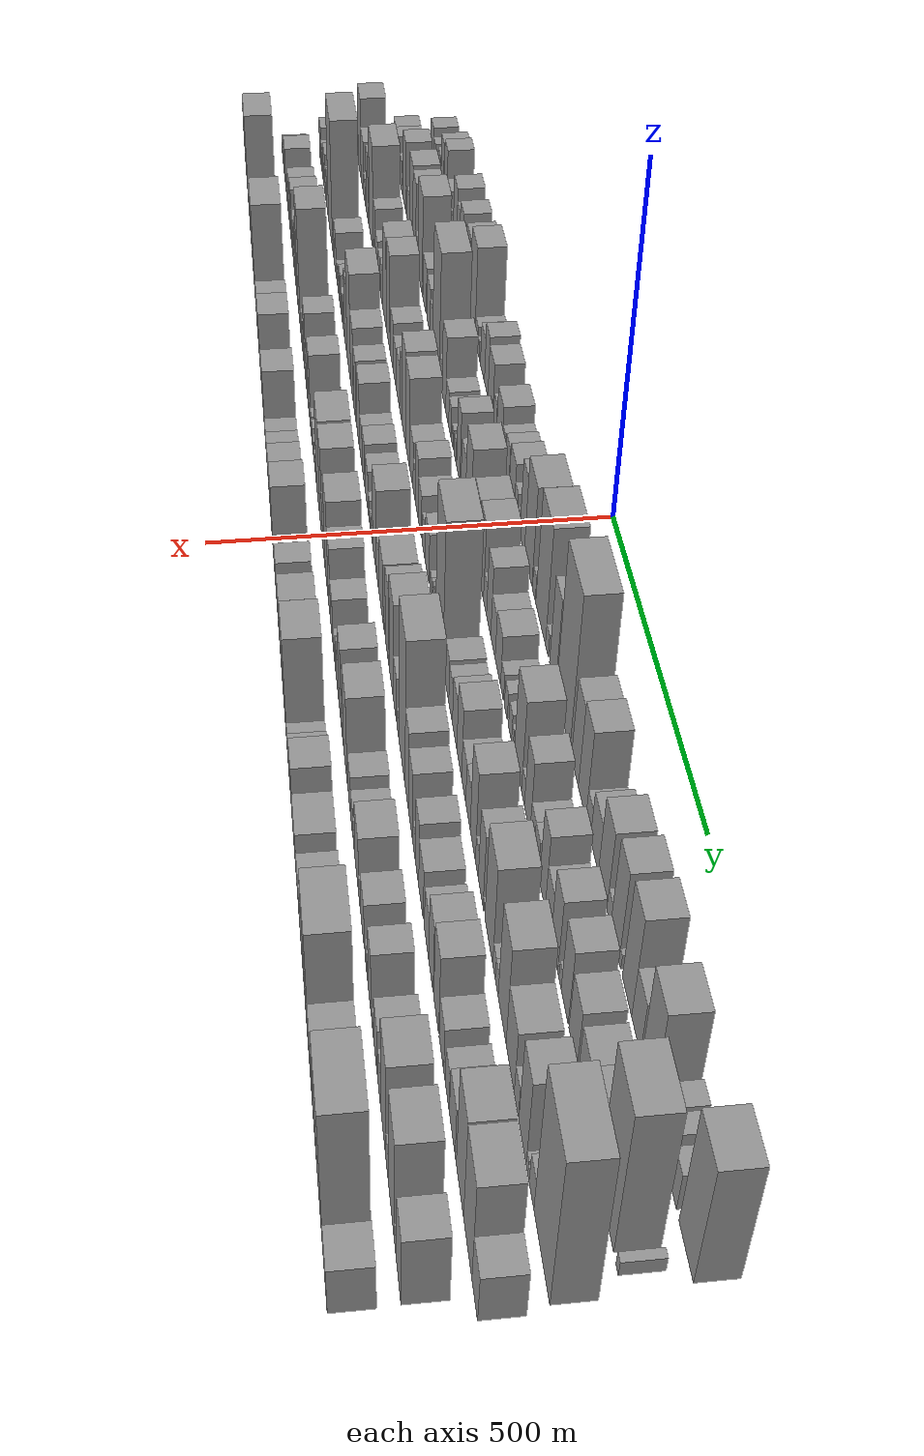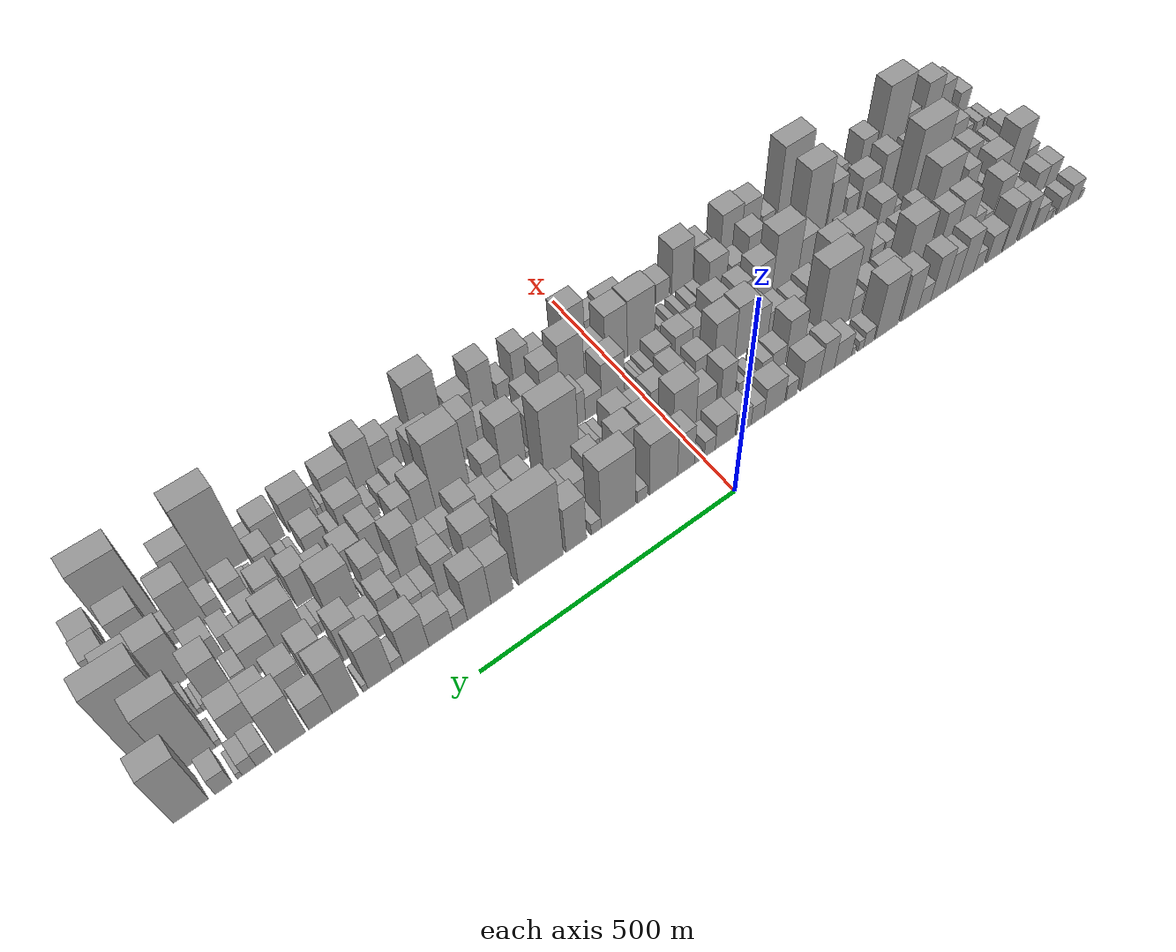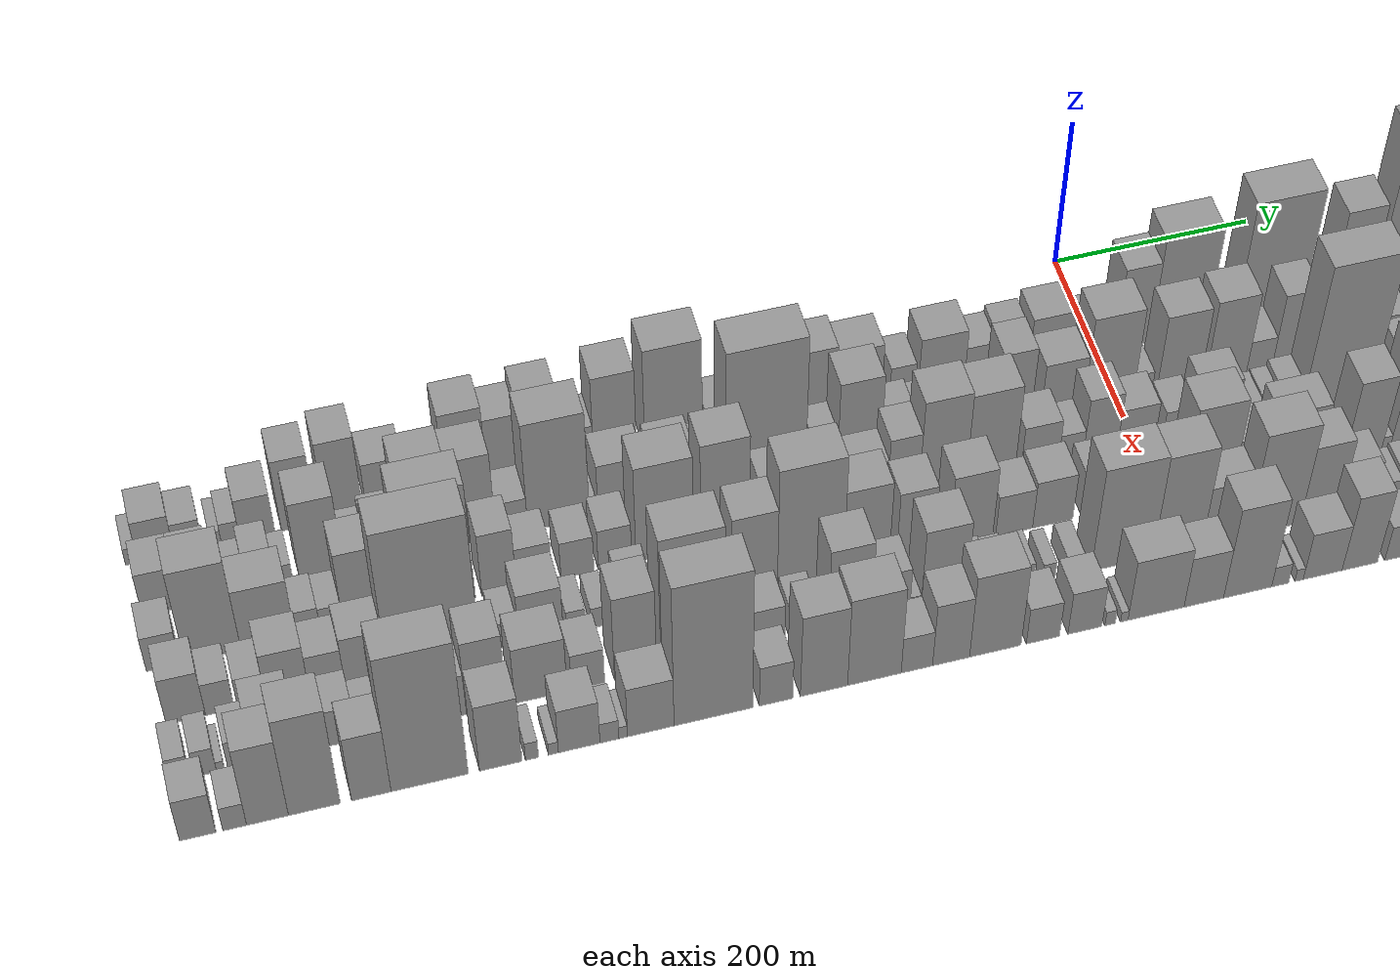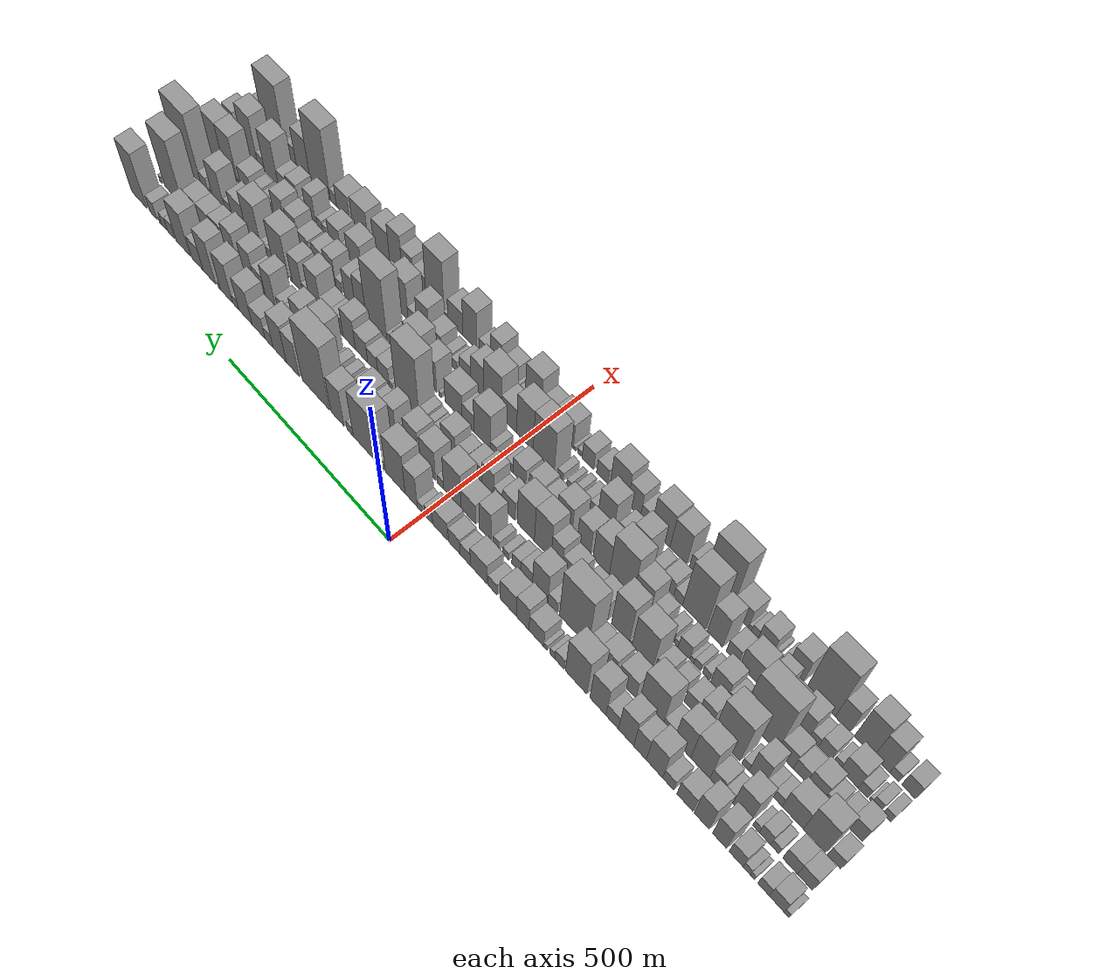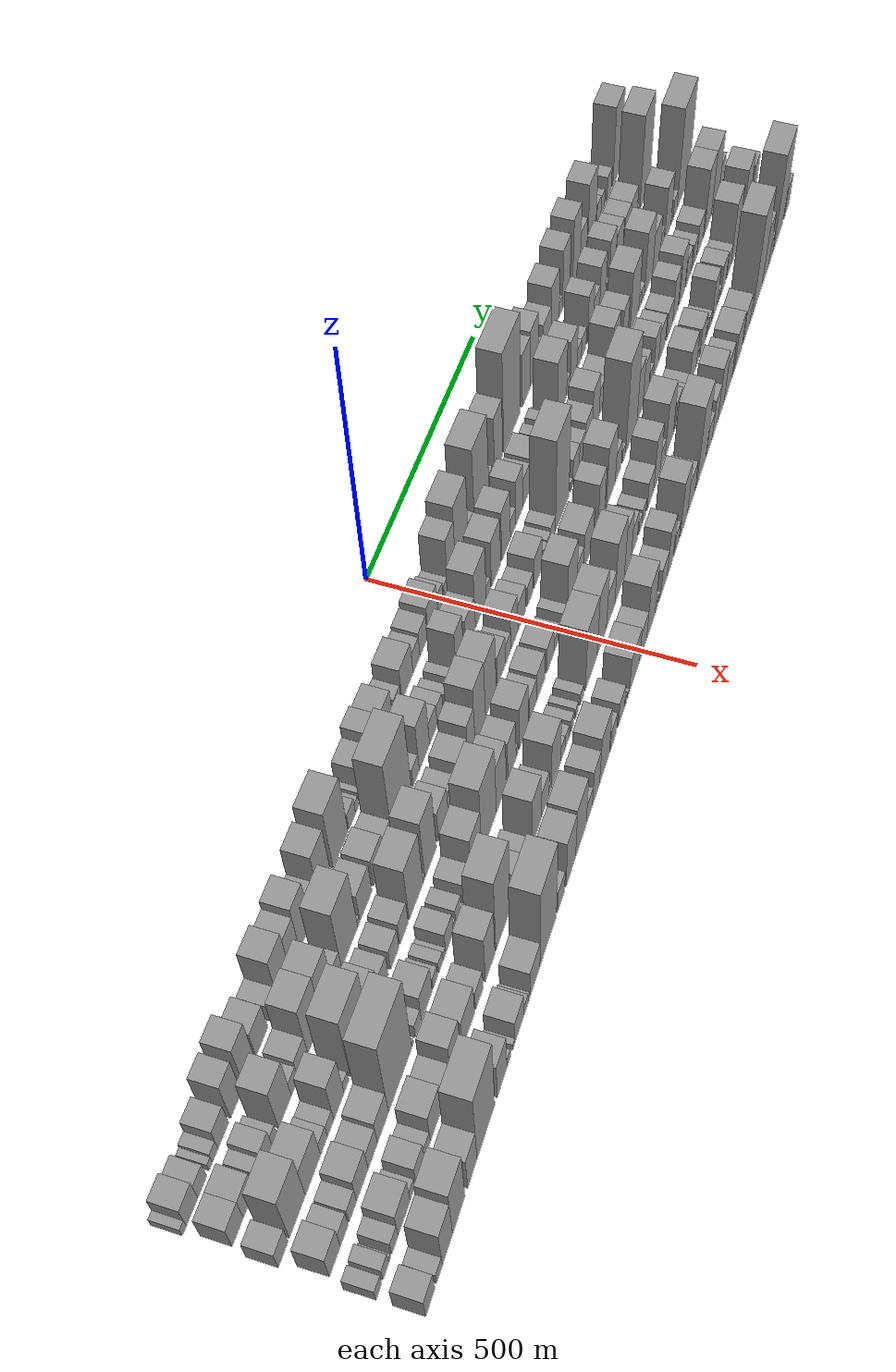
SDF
<sdf version="1.6">
 <world name="default">
  <scene>
   <sky><clouds><speed>12</speed></clouds></sky>
   <ambient>0.4 0.4 0.4 1</ambient>
   <background>0.7 0.7 0.7 1</background>
   <shadows>1</shadows>
  </scene>
  <gravity>0 0 -9.8066</gravity>
  <magnetic_field>6e-06 2.3e-05 -4.2e-05</magnetic_field>
  <physics default="0" name="default_physics" type="ode">
   <ode>
    <solver>
     <type>quick</type>
     <iters>10</iters>
     <sor>1.0</sor>
     <use_dynamic_moi_rescaling>0</use_dynamic_moi_rescaling>
    </solver>
    <constraints>
     <cfm>0</cfm>
     <erp>0.2</erp>
     <contact_max_correcting_vel>100</contact_max_correcting_vel>
     <contact_surface_layer>0.001</contact_surface_layer>
    </constraints>
   </ode>
   <max_step_size>0.004</max_step_size>
   <real_time_factor>1</real_time_factor>
   <real_time_update_rate>250</real_time_update_rate>
  </physics>
  <light name="sun" type="directional">
   <pose>0 0 10 0 0 0</pose>
   <diffuse>0.8 0.8 0.8 1</diffuse>
   <specular>0.2 0.2 0.2 1</specular>
   <attenuation>
    <range>1000</range>
    <constant>0.9</constant>
    <linear>0.01</linear>
    <quadratic>0.001</quadratic>
   </attenuation>
   <direction>-0.5 0.1 -0.9</direction>
  </light>
  <model name="building_1">
   <static>1</static>
   <pose>100.0000 -934.3074 0 0.000000 0.000000 0.000000</pose>
   <link name="link">
    <pose>0 0 12.00 0 0 0</pose>
    <collision name="collision"><geometry><box><size>40.0000 11.3851 24.0000</size></box></geometry></collision>
    <visual name="visual">
     <cast_shadows>0</cast_shadows>
     <geometry><box><size>40.0000 11.3851 24.0000</size></box></geometry>
     <material>
      <script>
       <uri>model://grey_wall/materials/scripts</uri>
       <uri>model://grey_wall/materials/textures</uri>
       <name>vrc/grey_wall</name>
      </script>
     </material>
    </visual>
   </link>
  </model>
  <model name="building_2">
   <static>1</static>
   <pose>100.0000 -911.6488 0 0.000000 0.000000 0.000000</pose>
   <link name="link">
    <pose>0 0 30.00 0 0 0</pose>
    <collision name="collision"><geometry><box><size>40.0000 33.9323 60.0000</size></box></geometry></collision>
    <visual name="visual">
     <cast_shadows>0</cast_shadows>
     <geometry><box><size>40.0000 33.9323 60.0000</size></box></geometry>
     <material>
      <script>
       <uri>model://grey_wall/materials/scripts</uri>
       <uri>model://grey_wall/materials/textures</uri>
       <name>vrc/grey_wall</name>
      </script>
     </material>
    </visual>
   </link>
  </model>
  <model name="building_3">
   <static>1</static>
   <pose>100.0000 -881.3711 0 0.000000 0.000000 0.000000</pose>
   <link name="link">
    <pose>0 0 22.50 0 0 0</pose>
    <collision name="collision"><geometry><box><size>40.0000 26.6231 45.0000</size></box></geometry></collision>
    <visual name="visual">
     <cast_shadows>0</cast_shadows>
     <geometry><box><size>40.0000 26.6231 45.0000</size></box></geometry>
     <material>
      <script>
       <uri>model://grey_wall/materials/scripts</uri>
       <uri>model://grey_wall/materials/textures</uri>
       <name>vrc/grey_wall</name>
      </script>
     </material>
    </visual>
   </link>
  </model>
  <model name="building_4">
   <static>1</static>
   <pose>100.0000 -856.0888 0 0.000000 0.000000 0.000000</pose>
   <link name="link">
    <pose>0 0 10.50 0 0 0</pose>
    <collision name="collision"><geometry><box><size>40.0000 9.9415 21.0000</size></box></geometry></collision>
    <visual name="visual">
     <cast_shadows>0</cast_shadows>
     <geometry><box><size>40.0000 9.9415 21.0000</size></box></geometry>
     <material>
      <script>
       <uri>model://grey_wall/materials/scripts</uri>
       <uri>model://grey_wall/materials/textures</uri>
       <name>vrc/grey_wall</name>
      </script>
     </material>
    </visual>
   </link>
  </model>
  <model name="building_5">
   <static>1</static>
   <pose>100.0000 -842.5951 0 0.000000 0.000000 0.000000</pose>
   <link name="link">
    <pose>0 0 15.00 0 0 0</pose>
    <collision name="collision"><geometry><box><size>40.0000 17.0459 30.0000</size></box></geometry></collision>
    <visual name="visual">
     <cast_shadows>0</cast_shadows>
     <geometry><box><size>40.0000 17.0459 30.0000</size></box></geometry>
     <material>
      <script>
       <uri>model://grey_wall/materials/scripts</uri>
       <uri>model://grey_wall/materials/textures</uri>
       <name>vrc/grey_wall</name>
      </script>
     </material>
    </visual>
   </link>
  </model>
  <model name="building_6">
   <static>1</static>
   <pose>100.0000 -817.6203 0 0.000000 0.000000 0.000000</pose>
   <link name="link">
    <pose>0 0 30.00 0 0 0</pose>
    <collision name="collision"><geometry><box><size>40.0000 32.9037 60.0000</size></box></geometry></collision>
    <visual name="visual">
     <cast_shadows>0</cast_shadows>
     <geometry><box><size>40.0000 32.9037 60.0000</size></box></geometry>
     <material>
      <script>
       <uri>model://grey_wall/materials/scripts</uri>
       <uri>model://grey_wall/materials/textures</uri>
       <name>vrc/grey_wall</name>
      </script>
     </material>
    </visual>
   </link>
  </model>
  <model name="building_7">
   <static>1</static>
   <pose>100.0000 -778.5018 0 0.000000 0.000000 0.000000</pose>
   <link name="link">
    <pose>0 0 52.50 0 0 0</pose>
    <collision name="collision"><geometry><box><size>40.0000 33.3333 105.0000</size></box></geometry></collision>
    <visual name="visual">
     <cast_shadows>0</cast_shadows>
     <geometry><box><size>40.0000 33.3333 105.0000</size></box></geometry>
     <material>
      <script>
       <uri>model://grey_wall/materials/scripts</uri>
       <uri>model://grey_wall/materials/textures</uri>
       <name>vrc/grey_wall</name>
      </script>
     </material>
    </visual>
   </link>
  </model>
  <model name="building_8">
   <static>1</static>
   <pose>100.0000 -735.9256 0 0.000000 0.000000 0.000000</pose>
   <link name="link">
    <pose>0 0 58.50 0 0 0</pose>
    <collision name="collision"><geometry><box><size>40.0000 35.8192 117.0000</size></box></geometry></collision>
    <visual name="visual">
     <cast_shadows>0</cast_shadows>
     <geometry><box><size>40.0000 35.8192 117.0000</size></box></geometry>
     <material>
      <script>
       <uri>model://grey_wall/materials/scripts</uri>
       <uri>model://grey_wall/materials/textures</uri>
       <name>vrc/grey_wall</name>
      </script>
     </material>
    </visual>
   </link>
  </model>
  <model name="building_9">
   <static>1</static>
   <pose>100.0000 -695.3884 0 0.000000 0.000000 0.000000</pose>
   <link name="link">
    <pose>0 0 36.00 0 0 0</pose>
    <collision name="collision"><geometry><box><size>40.0000 39.2552 72.0000</size></box></geometry></collision>
    <visual name="visual">
     <cast_shadows>0</cast_shadows>
     <geometry><box><size>40.0000 39.2552 72.0000</size></box></geometry>
     <material>
      <script>
       <uri>model://grey_wall/materials/scripts</uri>
       <uri>model://grey_wall/materials/textures</uri>
       <name>vrc/grey_wall</name>
      </script>
     </material>
    </visual>
   </link>
  </model>
  <model name="building_10">
   <static>1</static>
   <pose>100.0000 -654.2345 0 0.000000 0.000000 0.000000</pose>
   <link name="link">
    <pose>0 0 24.00 0 0 0</pose>
    <collision name="collision"><geometry><box><size>40.0000 27.0526 48.0000</size></box></geometry></collision>
    <visual name="visual">
     <cast_shadows>0</cast_shadows>
     <geometry><box><size>40.0000 27.0526 48.0000</size></box></geometry>
     <material>
      <script>
       <uri>model://grey_wall/materials/scripts</uri>
       <uri>model://grey_wall/materials/textures</uri>
       <name>vrc/grey_wall</name>
      </script>
     </material>
    </visual>
   </link>
  </model>
  <model name="building_11">
   <static>1</static>
   <pose>100.0000 -620.4603 0 0.000000 0.000000 0.000000</pose>
   <link name="link">
    <pose>0 0 60.00 0 0 0</pose>
    <collision name="collision"><geometry><box><size>40.0000 40.4957 120.0000</size></box></geometry></collision>
    <visual name="visual">
     <cast_shadows>0</cast_shadows>
     <geometry><box><size>40.0000 40.4957 120.0000</size></box></geometry>
     <material>
      <script>
       <uri>model://grey_wall/materials/scripts</uri>
       <uri>model://grey_wall/materials/textures</uri>
       <name>vrc/grey_wall</name>
      </script>
     </material>
    </visual>
   </link>
  </model>
  <model name="building_12">
   <static>1</static>
   <pose>100.0000 -584.1987 0 0.000000 0.000000 0.000000</pose>
   <link name="link">
    <pose>0 0 49.50 0 0 0</pose>
    <collision name="collision"><geometry><box><size>40.0000 32.0277 99.0000</size></box></geometry></collision>
    <visual name="visual">
     <cast_shadows>0</cast_shadows>
     <geometry><box><size>40.0000 32.0277 99.0000</size></box></geometry>
     <material>
      <script>
       <uri>model://grey_wall/materials/scripts</uri>
       <uri>model://grey_wall/materials/textures</uri>
       <name>vrc/grey_wall</name>
      </script>
     </material>
    </visual>
   </link>
  </model>
  <model name="building_13">
   <static>1</static>
   <pose>100.0000 -549.0110 0 0.000000 0.000000 0.000000</pose>
   <link name="link">
    <pose>0 0 60.00 0 0 0</pose>
    <collision name="collision"><geometry><box><size>40.0000 38.3477 120.0000</size></box></geometry></collision>
    <visual name="visual">
     <cast_shadows>0</cast_shadows>
     <geometry><box><size>40.0000 38.3477 120.0000</size></box></geometry>
     <material>
      <script>
       <uri>model://grey_wall/materials/scripts</uri>
       <uri>model://grey_wall/materials/textures</uri>
       <name>vrc/grey_wall</name>
      </script>
     </material>
    </visual>
   </link>
  </model>
  <model name="building_14">
   <static>1</static>
   <pose>100.0000 -513.8945 0 0.000000 0.000000 0.000000</pose>
   <link name="link">
    <pose>0 0 28.50 0 0 0</pose>
    <collision name="collision"><geometry><box><size>40.0000 31.8853 57.0000</size></box></geometry></collision>
    <visual name="visual">
     <cast_shadows>0</cast_shadows>
     <geometry><box><size>40.0000 31.8853 57.0000</size></box></geometry>
     <material>
      <script>
       <uri>model://grey_wall/materials/scripts</uri>
       <uri>model://grey_wall/materials/textures</uri>
       <name>vrc/grey_wall</name>
      </script>
     </material>
    </visual>
   </link>
  </model>
  <model name="building_15">
   <static>1</static>
   <pose>100.0000 -477.2440 0 0.000000 0.000000 0.000000</pose>
   <link name="link">
    <pose>0 0 63.00 0 0 0</pose>
    <collision name="collision"><geometry><box><size>40.0000 41.4157 126.0000</size></box></geometry></collision>
    <visual name="visual">
     <cast_shadows>0</cast_shadows>
     <geometry><box><size>40.0000 41.4157 126.0000</size></box></geometry>
     <material>
      <script>
       <uri>model://grey_wall/materials/scripts</uri>
       <uri>model://grey_wall/materials/textures</uri>
       <name>vrc/grey_wall</name>
      </script>
     </material>
    </visual>
   </link>
  </model>
  <model name="building_16">
   <static>1</static>
   <pose>100.0000 -420.5181 0 0.000000 0.000000 0.000000</pose>
   <link name="link">
    <pose>0 0 75.00 0 0 0</pose>
    <collision name="collision"><geometry><box><size>40.0000 56.0362 150.0000</size></box></geometry></collision>
    <visual name="visual">
     <cast_shadows>0</cast_shadows>
     <geometry><box><size>40.0000 56.0362 150.0000</size></box></geometry>
     <material>
      <script>
       <uri>model://grey_wall/materials/scripts</uri>
       <uri>model://grey_wall/materials/textures</uri>
       <name>vrc/grey_wall</name>
      </script>
     </material>
    </visual>
   </link>
  </model>
  <model name="building_17">
   <static>1</static>
   <pose>100.0000 -376.9105 0 0.000000 0.000000 0.000000</pose>
   <link name="link">
    <pose>0 0 21.00 0 0 0</pose>
    <collision name="collision"><geometry><box><size>40.0000 25.1789 42.0000</size></box></geometry></collision>
    <visual name="visual">
     <cast_shadows>0</cast_shadows>
     <geometry><box><size>40.0000 25.1789 42.0000</size></box></geometry>
     <material>
      <script>
       <uri>model://grey_wall/materials/scripts</uri>
       <uri>model://grey_wall/materials/textures</uri>
       <name>vrc/grey_wall</name>
      </script>
     </material>
    </visual>
   </link>
  </model>
  <model name="building_18">
   <static>1</static>
   <pose>100.0000 -357.7944 0 0.000000 0.000000 0.000000</pose>
   <link name="link">
    <pose>0 0 13.50 0 0 0</pose>
    <collision name="collision"><geometry><box><size>40.0000 13.0532 27.0000</size></box></geometry></collision>
    <visual name="visual">
     <cast_shadows>0</cast_shadows>
     <geometry><box><size>40.0000 13.0532 27.0000</size></box></geometry>
     <material>
      <script>
       <uri>model://grey_wall/materials/scripts</uri>
       <uri>model://grey_wall/materials/textures</uri>
       <name>vrc/grey_wall</name>
      </script>
     </material>
    </visual>
   </link>
  </model>
  <model name="building_19">
   <static>1</static>
   <pose>100.0000 -339.4813 0 0.000000 0.000000 0.000000</pose>
   <link name="link">
    <pose>0 0 10.50 0 0 0</pose>
    <collision name="collision"><geometry><box><size>40.0000 9.5730 21.0000</size></box></geometry></collision>
    <visual name="visual">
     <cast_shadows>0</cast_shadows>
     <geometry><box><size>40.0000 9.5730 21.0000</size></box></geometry>
     <material>
      <script>
       <uri>model://grey_wall/materials/scripts</uri>
       <uri>model://grey_wall/materials/textures</uri>
       <name>vrc/grey_wall</name>
      </script>
     </material>
    </visual>
   </link>
  </model>
  <model name="building_20">
   <static>1</static>
   <pose>100.0000 -314.7548 0 0.000000 0.000000 0.000000</pose>
   <link name="link">
    <pose>0 0 34.50 0 0 0</pose>
    <collision name="collision"><geometry><box><size>40.0000 39.8801 69.0000</size></box></geometry></collision>
    <visual name="visual">
     <cast_shadows>0</cast_shadows>
     <geometry><box><size>40.0000 39.8801 69.0000</size></box></geometry>
     <material>
      <script>
       <uri>model://grey_wall/materials/scripts</uri>
       <uri>model://grey_wall/materials/textures</uri>
       <name>vrc/grey_wall</name>
      </script>
     </material>
    </visual>
   </link>
  </model>
  <model name="building_21">
   <static>1</static>
   <pose>100.0000 -277.7871 0 0.000000 0.000000 0.000000</pose>
   <link name="link">
    <pose>0 0 48.00 0 0 0</pose>
    <collision name="collision"><geometry><box><size>40.0000 34.0553 96.0000</size></box></geometry></collision>
    <visual name="visual">
     <cast_shadows>0</cast_shadows>
     <geometry><box><size>40.0000 34.0553 96.0000</size></box></geometry>
     <material>
      <script>
       <uri>model://grey_wall/materials/scripts</uri>
       <uri>model://grey_wall/materials/textures</uri>
       <name>vrc/grey_wall</name>
      </script>
     </material>
    </visual>
   </link>
  </model>
  <model name="building_22">
   <static>1</static>
   <pose>100.0000 -238.1941 0 0.000000 0.000000 0.000000</pose>
   <link name="link">
    <pose>0 0 42.00 0 0 0</pose>
    <collision name="collision"><geometry><box><size>40.0000 45.1307 84.0000</size></box></geometry></collision>
    <visual name="visual">
     <cast_shadows>0</cast_shadows>
     <geometry><box><size>40.0000 45.1307 84.0000</size></box></geometry>
     <material>
      <script>
       <uri>model://grey_wall/materials/scripts</uri>
       <uri>model://grey_wall/materials/textures</uri>
       <name>vrc/grey_wall</name>
      </script>
     </material>
    </visual>
   </link>
  </model>
  <model name="building_23">
   <static>1</static>
   <pose>100.0000 -194.8852 0 0.000000 0.000000 0.000000</pose>
   <link name="link">
    <pose>0 0 22.50 0 0 0</pose>
    <collision name="collision"><geometry><box><size>40.0000 25.4871 45.0000</size></box></geometry></collision>
    <visual name="visual">
     <cast_shadows>0</cast_shadows>
     <geometry><box><size>40.0000 25.4871 45.0000</size></box></geometry>
     <material>
      <script>
       <uri>model://grey_wall/materials/scripts</uri>
       <uri>model://grey_wall/materials/textures</uri>
       <name>vrc/grey_wall</name>
      </script>
     </material>
    </visual>
   </link>
  </model>
  <model name="building_24">
   <static>1</static>
   <pose>100.0000 -155.9726 0 0.000000 0.000000 0.000000</pose>
   <link name="link">
    <pose>0 0 39.00 0 0 0</pose>
    <collision name="collision"><geometry><box><size>40.0000 46.3381 78.0000</size></box></geometry></collision>
    <visual name="visual">
     <cast_shadows>0</cast_shadows>
     <geometry><box><size>40.0000 46.3381 78.0000</size></box></geometry>
     <material>
      <script>
       <uri>model://grey_wall/materials/scripts</uri>
       <uri>model://grey_wall/materials/textures</uri>
       <name>vrc/grey_wall</name>
      </script>
     </material>
    </visual>
   </link>
  </model>
  <model name="building_25">
   <static>1</static>
   <pose>100.0000 -118.1382 0 0.000000 0.000000 0.000000</pose>
   <link name="link">
    <pose>0 0 25.50 0 0 0</pose>
    <collision name="collision"><geometry><box><size>40.0000 29.3307 51.0000</size></box></geometry></collision>
    <visual name="visual">
     <cast_shadows>0</cast_shadows>
     <geometry><box><size>40.0000 29.3307 51.0000</size></box></geometry>
     <material>
      <script>
       <uri>model://grey_wall/materials/scripts</uri>
       <uri>model://grey_wall/materials/textures</uri>
       <name>vrc/grey_wall</name>
      </script>
     </material>
    </visual>
   </link>
  </model>
  <model name="building_26">
   <static>1</static>
   <pose>100.0000 -87.1877 0 0.000000 0.000000 0.000000</pose>
   <link name="link">
    <pose>0 0 30.00 0 0 0</pose>
    <collision name="collision"><geometry><box><size>40.0000 32.5704 60.0000</size></box></geometry></collision>
    <visual name="visual">
     <cast_shadows>0</cast_shadows>
     <geometry><box><size>40.0000 32.5704 60.0000</size></box></geometry>
     <material>
      <script>
       <uri>model://grey_wall/materials/scripts</uri>
       <uri>model://grey_wall/materials/textures</uri>
       <name>vrc/grey_wall</name>
      </script>
     </material>
    </visual>
   </link>
  </model>
  <model name="building_27">
   <static>1</static>
   <pose>100.0000 -46.4277 0 0.000000 0.000000 0.000000</pose>
   <link name="link">
    <pose>0 0 36.00 0 0 0</pose>
    <collision name="collision"><geometry><box><size>40.0000 42.9495 72.0000</size></box></geometry></collision>
    <visual name="visual">
     <cast_shadows>0</cast_shadows>
     <geometry><box><size>40.0000 42.9495 72.0000</size></box></geometry>
     <material>
      <script>
       <uri>model://grey_wall/materials/scripts</uri>
       <uri>model://grey_wall/materials/textures</uri>
       <name>vrc/grey_wall</name>
      </script>
     </material>
    </visual>
   </link>
  </model>
  <model name="building_28">
   <static>1</static>
   <pose>100.0000 -13.3222 0 0.000000 0.000000 0.000000</pose>
   <link name="link">
    <pose>0 0 22.50 0 0 0</pose>
    <collision name="collision"><geometry><box><size>40.0000 23.2615 45.0000</size></box></geometry></collision>
    <visual name="visual">
     <cast_shadows>0</cast_shadows>
     <geometry><box><size>40.0000 23.2615 45.0000</size></box></geometry>
     <material>
      <script>
       <uri>model://grey_wall/materials/scripts</uri>
       <uri>model://grey_wall/materials/textures</uri>
       <name>vrc/grey_wall</name>
      </script>
     </material>
    </visual>
   </link>
  </model>
  <model name="building_29">
   <static>1</static>
   <pose>100.0000 11.5886 0 0.000000 0.000000 0.000000</pose>
   <link name="link">
    <pose>0 0 15.00 0 0 0</pose>
    <collision name="collision"><geometry><box><size>40.0000 16.5600 30.0000</size></box></geometry></collision>
    <visual name="visual">
     <cast_shadows>0</cast_shadows>
     <geometry><box><size>40.0000 16.5600 30.0000</size></box></geometry>
     <material>
      <script>
       <uri>model://grey_wall/materials/scripts</uri>
       <uri>model://grey_wall/materials/textures</uri>
       <name>vrc/grey_wall</name>
      </script>
     </material>
    </visual>
   </link>
  </model>
  <model name="building_30">
   <static>1</static>
   <pose>100.0000 37.7941 0 0.000000 0.000000 0.000000</pose>
   <link name="link">
    <pose>0 0 58.50 0 0 0</pose>
    <collision name="collision"><geometry><box><size>40.0000 35.8511 117.0000</size></box></geometry></collision>
    <visual name="visual">
     <cast_shadows>0</cast_shadows>
     <geometry><box><size>40.0000 35.8511 117.0000</size></box></geometry>
     <material>
      <script>
       <uri>model://grey_wall/materials/scripts</uri>
       <uri>model://grey_wall/materials/textures</uri>
       <name>vrc/grey_wall</name>
      </script>
     </material>
    </visual>
   </link>
  </model>
  <model name="building_31">
   <static>1</static>
   <pose>100.0000 84.9089 0 0.000000 0.000000 0.000000</pose>
   <link name="link">
    <pose>0 0 75.00 0 0 0</pose>
    <collision name="collision"><geometry><box><size>40.0000 58.3783 150.0000</size></box></geometry></collision>
    <visual name="visual">
     <cast_shadows>0</cast_shadows>
     <geometry><box><size>40.0000 58.3783 150.0000</size></box></geometry>
     <material>
      <script>
       <uri>model://grey_wall/materials/scripts</uri>
       <uri>model://grey_wall/materials/textures</uri>
       <name>vrc/grey_wall</name>
      </script>
     </material>
    </visual>
   </link>
  </model>
  <model name="building_32">
   <static>1</static>
   <pose>100.0000 128.4853 0 0.000000 0.000000 0.000000</pose>
   <link name="link">
    <pose>0 0 18.00 0 0 0</pose>
    <collision name="collision"><geometry><box><size>40.0000 20.7746 36.0000</size></box></geometry></collision>
    <visual name="visual">
     <cast_shadows>0</cast_shadows>
     <geometry><box><size>40.0000 20.7746 36.0000</size></box></geometry>
     <material>
      <script>
       <uri>model://grey_wall/materials/scripts</uri>
       <uri>model://grey_wall/materials/textures</uri>
       <name>vrc/grey_wall</name>
      </script>
     </material>
    </visual>
   </link>
  </model>
  <model name="building_33">
   <static>1</static>
   <pose>100.0000 177.5142 0 0.000000 0.000000 0.000000</pose>
   <link name="link">
    <pose>0 0 87.00 0 0 0</pose>
    <collision name="collision"><geometry><box><size>40.0000 69.2832 174.0000</size></box></geometry></collision>
    <visual name="visual">
     <cast_shadows>0</cast_shadows>
     <geometry><box><size>40.0000 69.2832 174.0000</size></box></geometry>
     <material>
      <script>
       <uri>model://grey_wall/materials/scripts</uri>
       <uri>model://grey_wall/materials/textures</uri>
       <name>vrc/grey_wall</name>
      </script>
     </material>
    </visual>
   </link>
  </model>
  <model name="building_34">
   <static>1</static>
   <pose>100.0000 221.9123 0 0.000000 0.000000 0.000000</pose>
   <link name="link">
    <pose>0 0 16.50 0 0 0</pose>
    <collision name="collision"><geometry><box><size>40.0000 19.5130 33.0000</size></box></geometry></collision>
    <visual name="visual">
     <cast_shadows>0</cast_shadows>
     <geometry><box><size>40.0000 19.5130 33.0000</size></box></geometry>
     <material>
      <script>
       <uri>model://grey_wall/materials/scripts</uri>
       <uri>model://grey_wall/materials/textures</uri>
       <name>vrc/grey_wall</name>
      </script>
     </material>
    </visual>
   </link>
  </model>
  <model name="building_35">
   <static>1</static>
   <pose>100.0000 261.0740 0 0.000000 0.000000 0.000000</pose>
   <link name="link">
    <pose>0 0 66.00 0 0 0</pose>
    <collision name="collision"><geometry><box><size>40.0000 40.8104 132.0000</size></box></geometry></collision>
    <visual name="visual">
     <cast_shadows>0</cast_shadows>
     <geometry><box><size>40.0000 40.8104 132.0000</size></box></geometry>
     <material>
      <script>
       <uri>model://grey_wall/materials/scripts</uri>
       <uri>model://grey_wall/materials/textures</uri>
       <name>vrc/grey_wall</name>
      </script>
     </material>
    </visual>
   </link>
  </model>
  <model name="building_36">
   <static>1</static>
   <pose>100.0000 329.4109 0 0.000000 0.000000 0.000000</pose>
   <link name="link">
    <pose>0 0 112.50 0 0 0</pose>
    <collision name="collision"><geometry><box><size>40.0000 85.8635 225.0000</size></box></geometry></collision>
    <visual name="visual">
     <cast_shadows>0</cast_shadows>
     <geometry><box><size>40.0000 85.8635 225.0000</size></box></geometry>
     <material>
      <script>
       <uri>model://grey_wall/materials/scripts</uri>
       <uri>model://grey_wall/materials/textures</uri>
       <name>vrc/grey_wall</name>
      </script>
     </material>
    </visual>
   </link>
  </model>
  <model name="building_37">
   <static>1</static>
   <pose>100.0000 403.0625 0 0.000000 0.000000 0.000000</pose>
   <link name="link">
    <pose>0 0 60.00 0 0 0</pose>
    <collision name="collision"><geometry><box><size>40.0000 41.4397 120.0000</size></box></geometry></collision>
    <visual name="visual">
     <cast_shadows>0</cast_shadows>
     <geometry><box><size>40.0000 41.4397 120.0000</size></box></geometry>
     <material>
      <script>
       <uri>model://grey_wall/materials/scripts</uri>
       <uri>model://grey_wall/materials/textures</uri>
       <name>vrc/grey_wall</name>
      </script>
     </material>
    </visual>
   </link>
  </model>
  <model name="building_38">
   <static>1</static>
   <pose>100.0000 445.5145 0 0.000000 0.000000 0.000000</pose>
   <link name="link">
    <pose>0 0 64.50 0 0 0</pose>
    <collision name="collision"><geometry><box><size>40.0000 43.4644 129.0000</size></box></geometry></collision>
    <visual name="visual">
     <cast_shadows>0</cast_shadows>
     <geometry><box><size>40.0000 43.4644 129.0000</size></box></geometry>
     <material>
      <script>
       <uri>model://grey_wall/materials/scripts</uri>
       <uri>model://grey_wall/materials/textures</uri>
       <name>vrc/grey_wall</name>
      </script>
     </material>
    </visual>
   </link>
  </model>
  <model name="building_39">
   <static>1</static>
   <pose>100.0000 480.3300 0 0.000000 0.000000 0.000000</pose>
   <link name="link">
    <pose>0 0 22.50 0 0 0</pose>
    <collision name="collision"><geometry><box><size>40.0000 26.1667 45.0000</size></box></geometry></collision>
    <visual name="visual">
     <cast_shadows>0</cast_shadows>
     <geometry><box><size>40.0000 26.1667 45.0000</size></box></geometry>
     <material>
      <script>
       <uri>model://grey_wall/materials/scripts</uri>
       <uri>model://grey_wall/materials/textures</uri>
       <name>vrc/grey_wall</name>
      </script>
     </material>
    </visual>
   </link>
  </model>
  <model name="building_40">
   <static>1</static>
   <pose>100.0000 514.9063 0 0.000000 0.000000 0.000000</pose>
   <link name="link">
    <pose>0 0 36.00 0 0 0</pose>
    <collision name="collision"><geometry><box><size>40.0000 42.9859 72.0000</size></box></geometry></collision>
    <visual name="visual">
     <cast_shadows>0</cast_shadows>
     <geometry><box><size>40.0000 42.9859 72.0000</size></box></geometry>
     <material>
      <script>
       <uri>model://grey_wall/materials/scripts</uri>
       <uri>model://grey_wall/materials/textures</uri>
       <name>vrc/grey_wall</name>
      </script>
     </material>
    </visual>
   </link>
  </model>
  <model name="building_41">
   <static>1</static>
   <pose>100.0000 558.9796 0 0.000000 0.000000 0.000000</pose>
   <link name="link">
    <pose>0 0 57.00 0 0 0</pose>
    <collision name="collision"><geometry><box><size>40.0000 45.1605 114.0000</size></box></geometry></collision>
    <visual name="visual">
     <cast_shadows>0</cast_shadows>
     <geometry><box><size>40.0000 45.1605 114.0000</size></box></geometry>
     <material>
      <script>
       <uri>model://grey_wall/materials/scripts</uri>
       <uri>model://grey_wall/materials/textures</uri>
       <name>vrc/grey_wall</name>
      </script>
     </material>
    </visual>
   </link>
  </model>
  <model name="building_42">
   <static>1</static>
   <pose>100.0000 591.3535 0 0.000000 0.000000 0.000000</pose>
   <link name="link">
    <pose>0 0 16.50 0 0 0</pose>
    <collision name="collision"><geometry><box><size>40.0000 19.5873 33.0000</size></box></geometry></collision>
    <visual name="visual">
     <cast_shadows>0</cast_shadows>
     <geometry><box><size>40.0000 19.5873 33.0000</size></box></geometry>
     <material>
      <script>
       <uri>model://grey_wall/materials/scripts</uri>
       <uri>model://grey_wall/materials/textures</uri>
       <name>vrc/grey_wall</name>
      </script>
     </material>
    </visual>
   </link>
  </model>
  <model name="building_43">
   <static>1</static>
   <pose>100.0000 622.0602 0 0.000000 0.000000 0.000000</pose>
   <link name="link">
    <pose>0 0 66.00 0 0 0</pose>
    <collision name="collision"><geometry><box><size>40.0000 41.8263 132.0000</size></box></geometry></collision>
    <visual name="visual">
     <cast_shadows>0</cast_shadows>
     <geometry><box><size>40.0000 41.8263 132.0000</size></box></geometry>
     <material>
      <script>
       <uri>model://grey_wall/materials/scripts</uri>
       <uri>model://grey_wall/materials/textures</uri>
       <name>vrc/grey_wall</name>
      </script>
     </material>
    </visual>
   </link>
  </model>
  <model name="building_44">
   <static>1</static>
   <pose>100.0000 647.2480 0 0.000000 0.000000 0.000000</pose>
   <link name="link">
    <pose>0 0 10.50 0 0 0</pose>
    <collision name="collision"><geometry><box><size>40.0000 8.5493 21.0000</size></box></geometry></collision>
    <visual name="visual">
     <cast_shadows>0</cast_shadows>
     <geometry><box><size>40.0000 8.5493 21.0000</size></box></geometry>
     <material>
      <script>
       <uri>model://grey_wall/materials/scripts</uri>
       <uri>model://grey_wall/materials/textures</uri>
       <name>vrc/grey_wall</name>
      </script>
     </material>
    </visual>
   </link>
  </model>
  <model name="building_45">
   <static>1</static>
   <pose>100.0000 681.4836 0 0.000000 0.000000 0.000000</pose>
   <link name="link">
    <pose>0 0 72.00 0 0 0</pose>
    <collision name="collision"><geometry><box><size>40.0000 43.9219 144.0000</size></box></geometry></collision>
    <visual name="visual">
     <cast_shadows>0</cast_shadows>
     <geometry><box><size>40.0000 43.9219 144.0000</size></box></geometry>
     <material>
      <script>
       <uri>model://grey_wall/materials/scripts</uri>
       <uri>model://grey_wall/materials/textures</uri>
       <name>vrc/grey_wall</name>
      </script>
     </material>
    </visual>
   </link>
  </model>
  <model name="building_46">
   <static>1</static>
   <pose>100.0000 723.3058 0 0.000000 0.000000 0.000000</pose>
   <link name="link">
    <pose>0 0 37.50 0 0 0</pose>
    <collision name="collision"><geometry><box><size>40.0000 39.7223 75.0000</size></box></geometry></collision>
    <visual name="visual">
     <cast_shadows>0</cast_shadows>
     <geometry><box><size>40.0000 39.7223 75.0000</size></box></geometry>
     <material>
      <script>
       <uri>model://grey_wall/materials/scripts</uri>
       <uri>model://grey_wall/materials/textures</uri>
       <name>vrc/grey_wall</name>
      </script>
     </material>
    </visual>
   </link>
  </model>
  <model name="building_47">
   <static>1</static>
   <pose>100.0000 773.0393 0 0.000000 0.000000 0.000000</pose>
   <link name="link">
    <pose>0 0 70.50 0 0 0</pose>
    <collision name="collision"><geometry><box><size>40.0000 49.7448 141.0000</size></box></geometry></collision>
    <visual name="visual">
     <cast_shadows>0</cast_shadows>
     <geometry><box><size>40.0000 49.7448 141.0000</size></box></geometry>
     <material>
      <script>
       <uri>model://grey_wall/materials/scripts</uri>
       <uri>model://grey_wall/materials/textures</uri>
       <name>vrc/grey_wall</name>
      </script>
     </material>
    </visual>
   </link>
  </model>
  <model name="building_48">
   <static>1</static>
   <pose>100.0000 815.7194 0 0.000000 0.000000 0.000000</pose>
   <link name="link">
    <pose>0 0 24.00 0 0 0</pose>
    <collision name="collision"><geometry><box><size>40.0000 25.6154 48.0000</size></box></geometry></collision>
    <visual name="visual">
     <cast_shadows>0</cast_shadows>
     <geometry><box><size>40.0000 25.6154 48.0000</size></box></geometry>
     <material>
      <script>
       <uri>model://grey_wall/materials/scripts</uri>
       <uri>model://grey_wall/materials/textures</uri>
       <name>vrc/grey_wall</name>
      </script>
     </material>
    </visual>
   </link>
  </model>
  <model name="building_49">
   <static>1</static>
   <pose>100.0000 839.4233 0 0.000000 0.000000 0.000000</pose>
   <link name="link">
    <pose>0 0 21.00 0 0 0</pose>
    <collision name="collision"><geometry><box><size>40.0000 21.7924 42.0000</size></box></geometry></collision>
    <visual name="visual">
     <cast_shadows>0</cast_shadows>
     <geometry><box><size>40.0000 21.7924 42.0000</size></box></geometry>
     <material>
      <script>
       <uri>model://grey_wall/materials/scripts</uri>
       <uri>model://grey_wall/materials/textures</uri>
       <name>vrc/grey_wall</name>
      </script>
     </material>
    </visual>
   </link>
  </model>
  <model name="building_50">
   <static>1</static>
   <pose>100.0000 854.3223 0 0.000000 0.000000 0.000000</pose>
   <link name="link">
    <pose>0 0 9.00 0 0 0</pose>
    <collision name="collision"><geometry><box><size>40.0000 8.0055 18.0000</size></box></geometry></collision>
    <visual name="visual">
     <cast_shadows>0</cast_shadows>
     <geometry><box><size>40.0000 8.0055 18.0000</size></box></geometry>
     <material>
      <script>
       <uri>model://grey_wall/materials/scripts</uri>
       <uri>model://grey_wall/materials/textures</uri>
       <name>vrc/grey_wall</name>
      </script>
     </material>
    </visual>
   </link>
  </model>
  <model name="building_51">
   <static>1</static>
   <pose>100.0000 879.9633 0 0.000000 0.000000 0.000000</pose>
   <link name="link">
    <pose>0 0 27.00 0 0 0</pose>
    <collision name="collision"><geometry><box><size>40.0000 27.2765 54.0000</size></box></geometry></collision>
    <visual name="visual">
     <cast_shadows>0</cast_shadows>
     <geometry><box><size>40.0000 27.2765 54.0000</size></box></geometry>
     <material>
      <script>
       <uri>model://grey_wall/materials/scripts</uri>
       <uri>model://grey_wall/materials/textures</uri>
       <name>vrc/grey_wall</name>
      </script>
     </material>
    </visual>
   </link>
  </model>
  <model name="building_52">
   <static>1</static>
   <pose>100.0000 930.5848 0 0.000000 0.000000 0.000000</pose>
   <link name="link">
    <pose>0 0 87.00 0 0 0</pose>
    <collision name="collision"><geometry><box><size>40.0000 53.9666 174.0000</size></box></geometry></collision>
    <visual name="visual">
     <cast_shadows>0</cast_shadows>
     <geometry><box><size>40.0000 53.9666 174.0000</size></box></geometry>
     <material>
      <script>
       <uri>model://grey_wall/materials/scripts</uri>
       <uri>model://grey_wall/materials/textures</uri>
       <name>vrc/grey_wall</name>
      </script>
     </material>
    </visual>
   </link>
  </model>
  <model name="building_53">
   <static>1</static>
   <pose>160.0000 -916.9654 0 0.000000 0.000000 0.000000</pose>
   <link name="link">
    <pose>0 0 31.50 0 0 0</pose>
    <collision name="collision"><geometry><box><size>40.0000 34.0693 63.0000</size></box></geometry></collision>
    <visual name="visual">
     <cast_shadows>0</cast_shadows>
     <geometry><box><size>40.0000 34.0693 63.0000</size></box></geometry>
     <material>
      <script>
       <uri>model://grey_wall/materials/scripts</uri>
       <uri>model://grey_wall/materials/textures</uri>
       <name>vrc/grey_wall</name>
      </script>
     </material>
    </visual>
   </link>
  </model>
  <model name="building_54">
   <static>1</static>
   <pose>160.0000 -882.7774 0 0.000000 0.000000 0.000000</pose>
   <link name="link">
    <pose>0 0 31.50 0 0 0</pose>
    <collision name="collision"><geometry><box><size>40.0000 34.3065 63.0000</size></box></geometry></collision>
    <visual name="visual">
     <cast_shadows>0</cast_shadows>
     <geometry><box><size>40.0000 34.3065 63.0000</size></box></geometry>
     <material>
      <script>
       <uri>model://grey_wall/materials/scripts</uri>
       <uri>model://grey_wall/materials/textures</uri>
       <name>vrc/grey_wall</name>
      </script>
     </material>
    </visual>
   </link>
  </model>
  <model name="building_55">
   <static>1</static>
   <pose>160.0000 -847.1455 0 0.000000 0.000000 0.000000</pose>
   <link name="link">
    <pose>0 0 16.50 0 0 0</pose>
    <collision name="collision"><geometry><box><size>40.0000 18.9574 33.0000</size></box></geometry></collision>
    <visual name="visual">
     <cast_shadows>0</cast_shadows>
     <geometry><box><size>40.0000 18.9574 33.0000</size></box></geometry>
     <material>
      <script>
       <uri>model://grey_wall/materials/scripts</uri>
       <uri>model://grey_wall/materials/textures</uri>
       <name>vrc/grey_wall</name>
      </script>
     </material>
    </visual>
   </link>
  </model>
  <model name="building_56">
   <static>1</static>
   <pose>160.0000 -824.3427 0 0.000000 0.000000 0.000000</pose>
   <link name="link">
    <pose>0 0 25.50 0 0 0</pose>
    <collision name="collision"><geometry><box><size>40.0000 26.6481 51.0000</size></box></geometry></collision>
    <visual name="visual">
     <cast_shadows>0</cast_shadows>
     <geometry><box><size>40.0000 26.6481 51.0000</size></box></geometry>
     <material>
      <script>
       <uri>model://grey_wall/materials/scripts</uri>
       <uri>model://grey_wall/materials/textures</uri>
       <name>vrc/grey_wall</name>
      </script>
     </material>
    </visual>
   </link>
  </model>
  <model name="building_57">
   <static>1</static>
   <pose>160.0000 -803.1540 0 0.000000 0.000000 0.000000</pose>
   <link name="link">
    <pose>0 0 15.00 0 0 0</pose>
    <collision name="collision"><geometry><box><size>40.0000 15.7293 30.0000</size></box></geometry></collision>
    <visual name="visual">
     <cast_shadows>0</cast_shadows>
     <geometry><box><size>40.0000 15.7293 30.0000</size></box></geometry>
     <material>
      <script>
       <uri>model://grey_wall/materials/scripts</uri>
       <uri>model://grey_wall/materials/textures</uri>
       <name>vrc/grey_wall</name>
      </script>
     </material>
    </visual>
   </link>
  </model>
  <model name="building_58">
   <static>1</static>
   <pose>160.0000 -768.6981 0 0.000000 0.000000 0.000000</pose>
   <link name="link">
    <pose>0 0 58.50 0 0 0</pose>
    <collision name="collision"><geometry><box><size>40.0000 41.1826 117.0000</size></box></geometry></collision>
    <visual name="visual">
     <cast_shadows>0</cast_shadows>
     <geometry><box><size>40.0000 41.1826 117.0000</size></box></geometry>
     <material>
      <script>
       <uri>model://grey_wall/materials/scripts</uri>
       <uri>model://grey_wall/materials/textures</uri>
       <name>vrc/grey_wall</name>
      </script>
     </material>
    </visual>
   </link>
  </model>
  <model name="building_59">
   <static>1</static>
   <pose>160.0000 -736.7922 0 0.000000 0.000000 0.000000</pose>
   <link name="link">
    <pose>0 0 21.00 0 0 0</pose>
    <collision name="collision"><geometry><box><size>40.0000 22.6292 42.0000</size></box></geometry></collision>
    <visual name="visual">
     <cast_shadows>0</cast_shadows>
     <geometry><box><size>40.0000 22.6292 42.0000</size></box></geometry>
     <material>
      <script>
       <uri>model://grey_wall/materials/scripts</uri>
       <uri>model://grey_wall/materials/textures</uri>
       <name>vrc/grey_wall</name>
      </script>
     </material>
    </visual>
   </link>
  </model>
  <model name="building_60">
   <static>1</static>
   <pose>160.0000 -709.2363 0 0.000000 0.000000 0.000000</pose>
   <link name="link">
    <pose>0 0 28.50 0 0 0</pose>
    <collision name="collision"><geometry><box><size>40.0000 32.4824 57.0000</size></box></geometry></collision>
    <visual name="visual">
     <cast_shadows>0</cast_shadows>
     <geometry><box><size>40.0000 32.4824 57.0000</size></box></geometry>
     <material>
      <script>
       <uri>model://grey_wall/materials/scripts</uri>
       <uri>model://grey_wall/materials/textures</uri>
       <name>vrc/grey_wall</name>
      </script>
     </material>
    </visual>
   </link>
  </model>
  <model name="building_61">
   <static>1</static>
   <pose>160.0000 -669.5841 0 0.000000 0.000000 0.000000</pose>
   <link name="link">
    <pose>0 0 67.50 0 0 0</pose>
    <collision name="collision"><geometry><box><size>40.0000 46.8219 135.0000</size></box></geometry></collision>
    <visual name="visual">
     <cast_shadows>0</cast_shadows>
     <geometry><box><size>40.0000 46.8219 135.0000</size></box></geometry>
     <material>
      <script>
       <uri>model://grey_wall/materials/scripts</uri>
       <uri>model://grey_wall/materials/textures</uri>
       <name>vrc/grey_wall</name>
      </script>
     </material>
    </visual>
   </link>
  </model>
  <model name="building_62">
   <static>1</static>
   <pose>160.0000 -625.7446 0 0.000000 0.000000 0.000000</pose>
   <link name="link">
    <pose>0 0 64.50 0 0 0</pose>
    <collision name="collision"><geometry><box><size>40.0000 40.8571 129.0000</size></box></geometry></collision>
    <visual name="visual">
     <cast_shadows>0</cast_shadows>
     <geometry><box><size>40.0000 40.8571 129.0000</size></box></geometry>
     <material>
      <script>
       <uri>model://grey_wall/materials/scripts</uri>
       <uri>model://grey_wall/materials/textures</uri>
       <name>vrc/grey_wall</name>
      </script>
     </material>
    </visual>
   </link>
  </model>
  <model name="building_63">
   <static>1</static>
   <pose>160.0000 -590.4081 0 0.000000 0.000000 0.000000</pose>
   <link name="link">
    <pose>0 0 25.50 0 0 0</pose>
    <collision name="collision"><geometry><box><size>40.0000 29.8159 51.0000</size></box></geometry></collision>
    <visual name="visual">
     <cast_shadows>0</cast_shadows>
     <geometry><box><size>40.0000 29.8159 51.0000</size></box></geometry>
     <material>
      <script>
       <uri>model://grey_wall/materials/scripts</uri>
       <uri>model://grey_wall/materials/textures</uri>
       <name>vrc/grey_wall</name>
      </script>
     </material>
    </visual>
   </link>
  </model>
  <model name="building_64">
   <static>1</static>
   <pose>160.0000 -546.1811 0 0.000000 0.000000 0.000000</pose>
   <link name="link">
    <pose>0 0 79.50 0 0 0</pose>
    <collision name="collision"><geometry><box><size>40.0000 58.6380 159.0000</size></box></geometry></collision>
    <visual name="visual">
     <cast_shadows>0</cast_shadows>
     <geometry><box><size>40.0000 58.6380 159.0000</size></box></geometry>
     <material>
      <script>
       <uri>model://grey_wall/materials/scripts</uri>
       <uri>model://grey_wall/materials/textures</uri>
       <name>vrc/grey_wall</name>
      </script>
     </material>
    </visual>
   </link>
  </model>
  <model name="building_65">
   <static>1</static>
   <pose>160.0000 -512.8103 0 0.000000 0.000000 0.000000</pose>
   <link name="link">
    <pose>0 0 9.00 0 0 0</pose>
    <collision name="collision"><geometry><box><size>40.0000 8.1037 18.0000</size></box></geometry></collision>
    <visual name="visual">
     <cast_shadows>0</cast_shadows>
     <geometry><box><size>40.0000 8.1037 18.0000</size></box></geometry>
     <material>
      <script>
       <uri>model://grey_wall/materials/scripts</uri>
       <uri>model://grey_wall/materials/textures</uri>
       <name>vrc/grey_wall</name>
      </script>
     </material>
    </visual>
   </link>
  </model>
  <model name="building_66">
   <static>1</static>
   <pose>160.0000 -486.3279 0 0.000000 0.000000 0.000000</pose>
   <link name="link">
    <pose>0 0 37.50 0 0 0</pose>
    <collision name="collision"><geometry><box><size>40.0000 44.8610 75.0000</size></box></geometry></collision>
    <visual name="visual">
     <cast_shadows>0</cast_shadows>
     <geometry><box><size>40.0000 44.8610 75.0000</size></box></geometry>
     <material>
      <script>
       <uri>model://grey_wall/materials/scripts</uri>
       <uri>model://grey_wall/materials/textures</uri>
       <name>vrc/grey_wall</name>
      </script>
     </material>
    </visual>
   </link>
  </model>
  <model name="building_67">
   <static>1</static>
   <pose>160.0000 -436.6515 0 0.000000 0.000000 0.000000</pose>
   <link name="link">
    <pose>0 0 36.00 0 0 0</pose>
    <collision name="collision"><geometry><box><size>40.0000 40.4918 72.0000</size></box></geometry></collision>
    <visual name="visual">
     <cast_shadows>0</cast_shadows>
     <geometry><box><size>40.0000 40.4918 72.0000</size></box></geometry>
     <material>
      <script>
       <uri>model://grey_wall/materials/scripts</uri>
       <uri>model://grey_wall/materials/textures</uri>
       <name>vrc/grey_wall</name>
      </script>
     </material>
    </visual>
   </link>
  </model>
  <model name="building_68">
   <static>1</static>
   <pose>160.0000 -401.1397 0 0.000000 0.000000 0.000000</pose>
   <link name="link">
    <pose>0 0 28.50 0 0 0</pose>
    <collision name="collision"><geometry><box><size>40.0000 30.5318 57.0000</size></box></geometry></collision>
    <visual name="visual">
     <cast_shadows>0</cast_shadows>
     <geometry><box><size>40.0000 30.5318 57.0000</size></box></geometry>
     <material>
      <script>
       <uri>model://grey_wall/materials/scripts</uri>
       <uri>model://grey_wall/materials/textures</uri>
       <name>vrc/grey_wall</name>
      </script>
     </material>
    </visual>
   </link>
  </model>
  <model name="building_69">
   <static>1</static>
   <pose>160.0000 -347.1861 0 0.000000 0.000000 0.000000</pose>
   <link name="link">
    <pose>0 0 99.00 0 0 0</pose>
    <collision name="collision"><geometry><box><size>40.0000 77.3754 198.0000</size></box></geometry></collision>
    <visual name="visual">
     <cast_shadows>0</cast_shadows>
     <geometry><box><size>40.0000 77.3754 198.0000</size></box></geometry>
     <material>
      <script>
       <uri>model://grey_wall/materials/scripts</uri>
       <uri>model://grey_wall/materials/textures</uri>
       <name>vrc/grey_wall</name>
      </script>
     </material>
    </visual>
   </link>
  </model>
  <model name="building_70">
   <static>1</static>
   <pose>160.0000 -289.8825 0 0.000000 0.000000 0.000000</pose>
   <link name="link">
    <pose>0 0 22.50 0 0 0</pose>
    <collision name="collision"><geometry><box><size>40.0000 25.2317 45.0000</size></box></geometry></collision>
    <visual name="visual">
     <cast_shadows>0</cast_shadows>
     <geometry><box><size>40.0000 25.2317 45.0000</size></box></geometry>
     <material>
      <script>
       <uri>model://grey_wall/materials/scripts</uri>
       <uri>model://grey_wall/materials/textures</uri>
       <name>vrc/grey_wall</name>
      </script>
     </material>
    </visual>
   </link>
  </model>
  <model name="building_71">
   <static>1</static>
   <pose>160.0000 -255.9788 0 0.000000 0.000000 0.000000</pose>
   <link name="link">
    <pose>0 0 58.50 0 0 0</pose>
    <collision name="collision"><geometry><box><size>40.0000 42.5757 117.0000</size></box></geometry></collision>
    <visual name="visual">
     <cast_shadows>0</cast_shadows>
     <geometry><box><size>40.0000 42.5757 117.0000</size></box></geometry>
     <material>
      <script>
       <uri>model://grey_wall/materials/scripts</uri>
       <uri>model://grey_wall/materials/textures</uri>
       <name>vrc/grey_wall</name>
      </script>
     </material>
    </visual>
   </link>
  </model>
  <model name="building_72">
   <static>1</static>
   <pose>160.0000 -218.6402 0 0.000000 0.000000 0.000000</pose>
   <link name="link">
    <pose>0 0 27.00 0 0 0</pose>
    <collision name="collision"><geometry><box><size>40.0000 32.1015 54.0000</size></box></geometry></collision>
    <visual name="visual">
     <cast_shadows>0</cast_shadows>
     <geometry><box><size>40.0000 32.1015 54.0000</size></box></geometry>
     <material>
      <script>
       <uri>model://grey_wall/materials/scripts</uri>
       <uri>model://grey_wall/materials/textures</uri>
       <name>vrc/grey_wall</name>
      </script>
     </material>
    </visual>
   </link>
  </model>
  <model name="building_73">
   <static>1</static>
   <pose>160.0000 -190.2422 0 0.000000 0.000000 0.000000</pose>
   <link name="link">
    <pose>0 0 24.00 0 0 0</pose>
    <collision name="collision"><geometry><box><size>40.0000 24.6945 48.0000</size></box></geometry></collision>
    <visual name="visual">
     <cast_shadows>0</cast_shadows>
     <geometry><box><size>40.0000 24.6945 48.0000</size></box></geometry>
     <material>
      <script>
       <uri>model://grey_wall/materials/scripts</uri>
       <uri>model://grey_wall/materials/textures</uri>
       <name>vrc/grey_wall</name>
      </script>
     </material>
    </visual>
   </link>
  </model>
  <model name="building_74">
   <static>1</static>
   <pose>160.0000 -161.2127 0 0.000000 0.000000 0.000000</pose>
   <link name="link">
    <pose>0 0 15.00 0 0 0</pose>
    <collision name="collision"><geometry><box><size>40.0000 17.3645 30.0000</size></box></geometry></collision>
    <visual name="visual">
     <cast_shadows>0</cast_shadows>
     <geometry><box><size>40.0000 17.3645 30.0000</size></box></geometry>
     <material>
      <script>
       <uri>model://grey_wall/materials/scripts</uri>
       <uri>model://grey_wall/materials/textures</uri>
       <name>vrc/grey_wall</name>
      </script>
     </material>
    </visual>
   </link>
  </model>
  <model name="building_75">
   <static>1</static>
   <pose>160.0000 -134.9675 0 0.000000 0.000000 0.000000</pose>
   <link name="link">
    <pose>0 0 16.50 0 0 0</pose>
    <collision name="collision"><geometry><box><size>40.0000 17.1258 33.0000</size></box></geometry></collision>
    <visual name="visual">
     <cast_shadows>0</cast_shadows>
     <geometry><box><size>40.0000 17.1258 33.0000</size></box></geometry>
     <material>
      <script>
       <uri>model://grey_wall/materials/scripts</uri>
       <uri>model://grey_wall/materials/textures</uri>
       <name>vrc/grey_wall</name>
      </script>
     </material>
    </visual>
   </link>
  </model>
  <model name="building_76">
   <static>1</static>
   <pose>160.0000 -102.8985 0 0.000000 0.000000 0.000000</pose>
   <link name="link">
    <pose>0 0 54.00 0 0 0</pose>
    <collision name="collision"><geometry><box><size>40.0000 33.0123 108.0000</size></box></geometry></collision>
    <visual name="visual">
     <cast_shadows>0</cast_shadows>
     <geometry><box><size>40.0000 33.0123 108.0000</size></box></geometry>
     <material>
      <script>
       <uri>model://grey_wall/materials/scripts</uri>
       <uri>model://grey_wall/materials/textures</uri>
       <name>vrc/grey_wall</name>
      </script>
     </material>
    </visual>
   </link>
  </model>
  <model name="building_77">
   <static>1</static>
   <pose>160.0000 -55.0341 0 0.000000 0.000000 0.000000</pose>
   <link name="link">
    <pose>0 0 39.00 0 0 0</pose>
    <collision name="collision"><geometry><box><size>40.0000 42.7164 78.0000</size></box></geometry></collision>
    <visual name="visual">
     <cast_shadows>0</cast_shadows>
     <geometry><box><size>40.0000 42.7164 78.0000</size></box></geometry>
     <material>
      <script>
       <uri>model://grey_wall/materials/scripts</uri>
       <uri>model://grey_wall/materials/textures</uri>
       <name>vrc/grey_wall</name>
      </script>
     </material>
    </visual>
   </link>
  </model>
  <model name="building_78">
   <static>1</static>
   <pose>160.0000 -8.6108 0 0.000000 0.000000 0.000000</pose>
   <link name="link">
    <pose>0 0 66.00 0 0 0</pose>
    <collision name="collision"><geometry><box><size>40.0000 50.1302 132.0000</size></box></geometry></collision>
    <visual name="visual">
     <cast_shadows>0</cast_shadows>
     <geometry><box><size>40.0000 50.1302 132.0000</size></box></geometry>
     <material>
      <script>
       <uri>model://grey_wall/materials/scripts</uri>
       <uri>model://grey_wall/materials/textures</uri>
       <name>vrc/grey_wall</name>
      </script>
     </material>
    </visual>
   </link>
  </model>
  <model name="building_79">
   <static>1</static>
   <pose>160.0000 25.9074 0 0.000000 0.000000 0.000000</pose>
   <link name="link">
    <pose>0 0 16.50 0 0 0</pose>
    <collision name="collision"><geometry><box><size>40.0000 18.9062 33.0000</size></box></geometry></collision>
    <visual name="visual">
     <cast_shadows>0</cast_shadows>
     <geometry><box><size>40.0000 18.9062 33.0000</size></box></geometry>
     <material>
      <script>
       <uri>model://grey_wall/materials/scripts</uri>
       <uri>model://grey_wall/materials/textures</uri>
       <name>vrc/grey_wall</name>
      </script>
     </material>
    </visual>
   </link>
  </model>
  <model name="building_80">
   <static>1</static>
   <pose>160.0000 62.5028 0 0.000000 0.000000 0.000000</pose>
   <link name="link">
    <pose>0 0 55.50 0 0 0</pose>
    <collision name="collision"><geometry><box><size>40.0000 44.2846 111.0000</size></box></geometry></collision>
    <visual name="visual">
     <cast_shadows>0</cast_shadows>
     <geometry><box><size>40.0000 44.2846 111.0000</size></box></geometry>
     <material>
      <script>
       <uri>model://grey_wall/materials/scripts</uri>
       <uri>model://grey_wall/materials/textures</uri>
       <name>vrc/grey_wall</name>
      </script>
     </material>
    </visual>
   </link>
  </model>
  <model name="building_81">
   <static>1</static>
   <pose>160.0000 110.7721 0 0.000000 0.000000 0.000000</pose>
   <link name="link">
    <pose>0 0 58.50 0 0 0</pose>
    <collision name="collision"><geometry><box><size>40.0000 42.2540 117.0000</size></box></geometry></collision>
    <visual name="visual">
     <cast_shadows>0</cast_shadows>
     <geometry><box><size>40.0000 42.2540 117.0000</size></box></geometry>
     <material>
      <script>
       <uri>model://grey_wall/materials/scripts</uri>
       <uri>model://grey_wall/materials/textures</uri>
       <name>vrc/grey_wall</name>
      </script>
     </material>
    </visual>
   </link>
  </model>
  <model name="building_82">
   <static>1</static>
   <pose>160.0000 145.0580 0 0.000000 0.000000 0.000000</pose>
   <link name="link">
    <pose>0 0 22.50 0 0 0</pose>
    <collision name="collision"><geometry><box><size>40.0000 26.3178 45.0000</size></box></geometry></collision>
    <visual name="visual">
     <cast_shadows>0</cast_shadows>
     <geometry><box><size>40.0000 26.3178 45.0000</size></box></geometry>
     <material>
      <script>
       <uri>model://grey_wall/materials/scripts</uri>
       <uri>model://grey_wall/materials/textures</uri>
       <name>vrc/grey_wall</name>
      </script>
     </material>
    </visual>
   </link>
  </model>
  <model name="building_83">
   <static>1</static>
   <pose>160.0000 175.5884 0 0.000000 0.000000 0.000000</pose>
   <link name="link">
    <pose>0 0 52.50 0 0 0</pose>
    <collision name="collision"><geometry><box><size>40.0000 34.7431 105.0000</size></box></geometry></collision>
    <visual name="visual">
     <cast_shadows>0</cast_shadows>
     <geometry><box><size>40.0000 34.7431 105.0000</size></box></geometry>
     <material>
      <script>
       <uri>model://grey_wall/materials/scripts</uri>
       <uri>model://grey_wall/materials/textures</uri>
       <name>vrc/grey_wall</name>
      </script>
     </material>
    </visual>
   </link>
  </model>
  <model name="building_84">
   <static>1</static>
   <pose>160.0000 210.9812 0 0.000000 0.000000 0.000000</pose>
   <link name="link">
    <pose>0 0 33.00 0 0 0</pose>
    <collision name="collision"><geometry><box><size>40.0000 36.0424 66.0000</size></box></geometry></collision>
    <visual name="visual">
     <cast_shadows>0</cast_shadows>
     <geometry><box><size>40.0000 36.0424 66.0000</size></box></geometry>
     <material>
      <script>
       <uri>model://grey_wall/materials/scripts</uri>
       <uri>model://grey_wall/materials/textures</uri>
       <name>vrc/grey_wall</name>
      </script>
     </material>
    </visual>
   </link>
  </model>
  <model name="building_85">
   <static>1</static>
   <pose>160.0000 250.0289 0 0.000000 0.000000 0.000000</pose>
   <link name="link">
    <pose>0 0 37.50 0 0 0</pose>
    <collision name="collision"><geometry><box><size>40.0000 42.0532 75.0000</size></box></geometry></collision>
    <visual name="visual">
     <cast_shadows>0</cast_shadows>
     <geometry><box><size>40.0000 42.0532 75.0000</size></box></geometry>
     <material>
      <script>
       <uri>model://grey_wall/materials/scripts</uri>
       <uri>model://grey_wall/materials/textures</uri>
       <name>vrc/grey_wall</name>
      </script>
     </material>
    </visual>
   </link>
  </model>
  <model name="building_86">
   <static>1</static>
   <pose>160.0000 282.3852 0 0.000000 0.000000 0.000000</pose>
   <link name="link">
    <pose>0 0 19.50 0 0 0</pose>
    <collision name="collision"><geometry><box><size>40.0000 22.6594 39.0000</size></box></geometry></collision>
    <visual name="visual">
     <cast_shadows>0</cast_shadows>
     <geometry><box><size>40.0000 22.6594 39.0000</size></box></geometry>
     <material>
      <script>
       <uri>model://grey_wall/materials/scripts</uri>
       <uri>model://grey_wall/materials/textures</uri>
       <name>vrc/grey_wall</name>
      </script>
     </material>
    </visual>
   </link>
  </model>
  <model name="building_87">
   <static>1</static>
   <pose>160.0000 311.2441 0 0.000000 0.000000 0.000000</pose>
   <link name="link">
    <pose>0 0 19.50 0 0 0</pose>
    <collision name="collision"><geometry><box><size>40.0000 21.0583 39.0000</size></box></geometry></collision>
    <visual name="visual">
     <cast_shadows>0</cast_shadows>
     <geometry><box><size>40.0000 21.0583 39.0000</size></box></geometry>
     <material>
      <script>
       <uri>model://grey_wall/materials/scripts</uri>
       <uri>model://grey_wall/materials/textures</uri>
       <name>vrc/grey_wall</name>
      </script>
     </material>
    </visual>
   </link>
  </model>
  <model name="building_88">
   <static>1</static>
   <pose>160.0000 342.4402 0 0.000000 0.000000 0.000000</pose>
   <link name="link">
    <pose>0 0 19.50 0 0 0</pose>
    <collision name="collision"><geometry><box><size>40.0000 21.3340 39.0000</size></box></geometry></collision>
    <visual name="visual">
     <cast_shadows>0</cast_shadows>
     <geometry><box><size>40.0000 21.3340 39.0000</size></box></geometry>
     <material>
      <script>
       <uri>model://grey_wall/materials/scripts</uri>
       <uri>model://grey_wall/materials/textures</uri>
       <name>vrc/grey_wall</name>
      </script>
     </material>
    </visual>
   </link>
  </model>
  <model name="building_89">
   <static>1</static>
   <pose>160.0000 358.8077 0 0.000000 0.000000 0.000000</pose>
   <link name="link">
    <pose>0 0 13.50 0 0 0</pose>
    <collision name="collision"><geometry><box><size>40.0000 11.4010 27.0000</size></box></geometry></collision>
    <visual name="visual">
     <cast_shadows>0</cast_shadows>
     <geometry><box><size>40.0000 11.4010 27.0000</size></box></geometry>
     <material>
      <script>
       <uri>model://grey_wall/materials/scripts</uri>
       <uri>model://grey_wall/materials/textures</uri>
       <name>vrc/grey_wall</name>
      </script>
     </material>
    </visual>
   </link>
  </model>
  <model name="building_90">
   <static>1</static>
   <pose>160.0000 397.8116 0 0.000000 0.000000 0.000000</pose>
   <link name="link">
    <pose>0 0 66.00 0 0 0</pose>
    <collision name="collision"><geometry><box><size>40.0000 50.6069 132.0000</size></box></geometry></collision>
    <visual name="visual">
     <cast_shadows>0</cast_shadows>
     <geometry><box><size>40.0000 50.6069 132.0000</size></box></geometry>
     <material>
      <script>
       <uri>model://grey_wall/materials/scripts</uri>
       <uri>model://grey_wall/materials/textures</uri>
       <name>vrc/grey_wall</name>
      </script>
     </material>
    </visual>
   </link>
  </model>
  <model name="building_91">
   <static>1</static>
   <pose>160.0000 433.1164 0 0.000000 0.000000 0.000000</pose>
   <link name="link">
    <pose>0 0 18.00 0 0 0</pose>
    <collision name="collision"><geometry><box><size>40.0000 20.0027 36.0000</size></box></geometry></collision>
    <visual name="visual">
     <cast_shadows>0</cast_shadows>
     <geometry><box><size>40.0000 20.0027 36.0000</size></box></geometry>
     <material>
      <script>
       <uri>model://grey_wall/materials/scripts</uri>
       <uri>model://grey_wall/materials/textures</uri>
       <name>vrc/grey_wall</name>
      </script>
     </material>
    </visual>
   </link>
  </model>
  <model name="building_92">
   <static>1</static>
   <pose>160.0000 461.6123 0 0.000000 0.000000 0.000000</pose>
   <link name="link">
    <pose>0 0 52.50 0 0 0</pose>
    <collision name="collision"><geometry><box><size>40.0000 36.9890 105.0000</size></box></geometry></collision>
    <visual name="visual">
     <cast_shadows>0</cast_shadows>
     <geometry><box><size>40.0000 36.9890 105.0000</size></box></geometry>
     <material>
      <script>
       <uri>model://grey_wall/materials/scripts</uri>
       <uri>model://grey_wall/materials/textures</uri>
       <name>vrc/grey_wall</name>
      </script>
     </material>
    </visual>
   </link>
  </model>
  <model name="building_93">
   <static>1</static>
   <pose>160.0000 492.9725 0 0.000000 0.000000 0.000000</pose>
   <link name="link">
    <pose>0 0 24.00 0 0 0</pose>
    <collision name="collision"><geometry><box><size>40.0000 25.7315 48.0000</size></box></geometry></collision>
    <visual name="visual">
     <cast_shadows>0</cast_shadows>
     <geometry><box><size>40.0000 25.7315 48.0000</size></box></geometry>
     <material>
      <script>
       <uri>model://grey_wall/materials/scripts</uri>
       <uri>model://grey_wall/materials/textures</uri>
       <name>vrc/grey_wall</name>
      </script>
     </material>
    </visual>
   </link>
  </model>
  <model name="building_94">
   <static>1</static>
   <pose>160.0000 519.2498 0 0.000000 0.000000 0.000000</pose>
   <link name="link">
    <pose>0 0 24.00 0 0 0</pose>
    <collision name="collision"><geometry><box><size>40.0000 26.8231 48.0000</size></box></geometry></collision>
    <visual name="visual">
     <cast_shadows>0</cast_shadows>
     <geometry><box><size>40.0000 26.8231 48.0000</size></box></geometry>
     <material>
      <script>
       <uri>model://grey_wall/materials/scripts</uri>
       <uri>model://grey_wall/materials/textures</uri>
       <name>vrc/grey_wall</name>
      </script>
     </material>
    </visual>
   </link>
  </model>
  <model name="building_95">
   <static>1</static>
   <pose>160.0000 557.7974 0 0.000000 0.000000 0.000000</pose>
   <link name="link">
    <pose>0 0 54.00 0 0 0</pose>
    <collision name="collision"><geometry><box><size>40.0000 34.2721 108.0000</size></box></geometry></collision>
    <visual name="visual">
     <cast_shadows>0</cast_shadows>
     <geometry><box><size>40.0000 34.2721 108.0000</size></box></geometry>
     <material>
      <script>
       <uri>model://grey_wall/materials/scripts</uri>
       <uri>model://grey_wall/materials/textures</uri>
       <name>vrc/grey_wall</name>
      </script>
     </material>
    </visual>
   </link>
  </model>
  <model name="building_96">
   <static>1</static>
   <pose>160.0000 592.6515 0 0.000000 0.000000 0.000000</pose>
   <link name="link">
    <pose>0 0 33.00 0 0 0</pose>
    <collision name="collision"><geometry><box><size>40.0000 35.4361 66.0000</size></box></geometry></collision>
    <visual name="visual">
     <cast_shadows>0</cast_shadows>
     <geometry><box><size>40.0000 35.4361 66.0000</size></box></geometry>
     <material>
      <script>
       <uri>model://grey_wall/materials/scripts</uri>
       <uri>model://grey_wall/materials/textures</uri>
       <name>vrc/grey_wall</name>
      </script>
     </material>
    </visual>
   </link>
  </model>
  <model name="building_97">
   <static>1</static>
   <pose>160.0000 629.3509 0 0.000000 0.000000 0.000000</pose>
   <link name="link">
    <pose>0 0 52.50 0 0 0</pose>
    <collision name="collision"><geometry><box><size>40.0000 37.9627 105.0000</size></box></geometry></collision>
    <visual name="visual">
     <cast_shadows>0</cast_shadows>
     <geometry><box><size>40.0000 37.9627 105.0000</size></box></geometry>
     <material>
      <script>
       <uri>model://grey_wall/materials/scripts</uri>
       <uri>model://grey_wall/materials/textures</uri>
       <name>vrc/grey_wall</name>
      </script>
     </material>
    </visual>
   </link>
  </model>
  <model name="building_98">
   <static>1</static>
   <pose>160.0000 651.8064 0 0.000000 0.000000 0.000000</pose>
   <link name="link">
    <pose>0 0 7.50 0 0 0</pose>
    <collision name="collision"><geometry><box><size>40.0000 6.9485 15.0000</size></box></geometry></collision>
    <visual name="visual">
     <cast_shadows>0</cast_shadows>
     <geometry><box><size>40.0000 6.9485 15.0000</size></box></geometry>
     <material>
      <script>
       <uri>model://grey_wall/materials/scripts</uri>
       <uri>model://grey_wall/materials/textures</uri>
       <name>vrc/grey_wall</name>
      </script>
     </material>
    </visual>
   </link>
  </model>
  <model name="building_99">
   <static>1</static>
   <pose>160.0000 661.4851 0 0.000000 0.000000 0.000000</pose>
   <link name="link">
    <pose>0 0 13.50 0 0 0</pose>
    <collision name="collision"><geometry><box><size>40.0000 12.4088 27.0000</size></box></geometry></collision>
    <visual name="visual">
     <cast_shadows>0</cast_shadows>
     <geometry><box><size>40.0000 12.4088 27.0000</size></box></geometry>
     <material>
      <script>
       <uri>model://grey_wall/materials/scripts</uri>
       <uri>model://grey_wall/materials/textures</uri>
       <name>vrc/grey_wall</name>
      </script>
     </material>
    </visual>
   </link>
  </model>
  <model name="building_100">
   <static>1</static>
   <pose>160.0000 686.7672 0 0.000000 0.000000 0.000000</pose>
   <link name="link">
    <pose>0 0 54.00 0 0 0</pose>
    <collision name="collision"><geometry><box><size>40.0000 38.1554 108.0000</size></box></geometry></collision>
    <visual name="visual">
     <cast_shadows>0</cast_shadows>
     <geometry><box><size>40.0000 38.1554 108.0000</size></box></geometry>
     <material>
      <script>
       <uri>model://grey_wall/materials/scripts</uri>
       <uri>model://grey_wall/materials/textures</uri>
       <name>vrc/grey_wall</name>
      </script>
     </material>
    </visual>
   </link>
  </model>
  <model name="building_101">
   <static>1</static>
   <pose>160.0000 731.0531 0 0.000000 0.000000 0.000000</pose>
   <link name="link">
    <pose>0 0 42.00 0 0 0</pose>
    <collision name="collision"><geometry><box><size>40.0000 42.4162 84.0000</size></box></geometry></collision>
    <visual name="visual">
     <cast_shadows>0</cast_shadows>
     <geometry><box><size>40.0000 42.4162 84.0000</size></box></geometry>
     <material>
      <script>
       <uri>model://grey_wall/materials/scripts</uri>
       <uri>model://grey_wall/materials/textures</uri>
       <name>vrc/grey_wall</name>
      </script>
     </material>
    </visual>
   </link>
  </model>
  <model name="building_102">
   <static>1</static>
   <pose>160.0000 778.1265 0 0.000000 0.000000 0.000000</pose>
   <link name="link">
    <pose>0 0 37.50 0 0 0</pose>
    <collision name="collision"><geometry><box><size>40.0000 39.7307 75.0000</size></box></geometry></collision>
    <visual name="visual">
     <cast_shadows>0</cast_shadows>
     <geometry><box><size>40.0000 39.7307 75.0000</size></box></geometry>
     <material>
      <script>
       <uri>model://grey_wall/materials/scripts</uri>
       <uri>model://grey_wall/materials/textures</uri>
       <name>vrc/grey_wall</name>
      </script>
     </material>
    </visual>
   </link>
  </model>
  <model name="building_103">
   <static>1</static>
   <pose>160.0000 819.9003 0 0.000000 0.000000 0.000000</pose>
   <link name="link">
    <pose>0 0 37.50 0 0 0</pose>
    <collision name="collision"><geometry><box><size>40.0000 43.8170 75.0000</size></box></geometry></collision>
    <visual name="visual">
     <cast_shadows>0</cast_shadows>
     <geometry><box><size>40.0000 43.8170 75.0000</size></box></geometry>
     <material>
      <script>
       <uri>model://grey_wall/materials/scripts</uri>
       <uri>model://grey_wall/materials/textures</uri>
       <name>vrc/grey_wall</name>
      </script>
     </material>
    </visual>
   </link>
  </model>
  <model name="building_104">
   <static>1</static>
   <pose>160.0000 855.2845 0 0.000000 0.000000 0.000000</pose>
   <link name="link">
    <pose>0 0 9.00 0 0 0</pose>
    <collision name="collision"><geometry><box><size>40.0000 8.9513 18.0000</size></box></geometry></collision>
    <visual name="visual">
     <cast_shadows>0</cast_shadows>
     <geometry><box><size>40.0000 8.9513 18.0000</size></box></geometry>
     <material>
      <script>
       <uri>model://grey_wall/materials/scripts</uri>
       <uri>model://grey_wall/materials/textures</uri>
       <name>vrc/grey_wall</name>
      </script>
     </material>
    </visual>
   </link>
  </model>
  <model name="building_105">
   <static>1</static>
   <pose>160.0000 892.6308 0 0.000000 0.000000 0.000000</pose>
   <link name="link">
    <pose>0 0 103.50 0 0 0</pose>
    <collision name="collision"><geometry><box><size>40.0000 65.7413 207.0000</size></box></geometry></collision>
    <visual name="visual">
     <cast_shadows>0</cast_shadows>
     <geometry><box><size>40.0000 65.7413 207.0000</size></box></geometry>
     <material>
      <script>
       <uri>model://grey_wall/materials/scripts</uri>
       <uri>model://grey_wall/materials/textures</uri>
       <name>vrc/grey_wall</name>
      </script>
     </material>
    </visual>
   </link>
  </model>
  <model name="building_106">
   <static>1</static>
   <pose>160.0000 940.2996 0 0.000000 0.000000 0.000000</pose>
   <link name="link">
    <pose>0 0 10.50 0 0 0</pose>
    <collision name="collision"><geometry><box><size>40.0000 9.5963 21.0000</size></box></geometry></collision>
    <visual name="visual">
     <cast_shadows>0</cast_shadows>
     <geometry><box><size>40.0000 9.5963 21.0000</size></box></geometry>
     <material>
      <script>
       <uri>model://grey_wall/materials/scripts</uri>
       <uri>model://grey_wall/materials/textures</uri>
       <name>vrc/grey_wall</name>
      </script>
     </material>
    </visual>
   </link>
  </model>
  <model name="building_107">
   <static>1</static>
   <pose>220.0000 -924.7312 0 0.000000 0.000000 0.000000</pose>
   <link name="link">
    <pose>0 0 25.50 0 0 0</pose>
    <collision name="collision"><geometry><box><size>40.0000 30.5375 51.0000</size></box></geometry></collision>
    <visual name="visual">
     <cast_shadows>0</cast_shadows>
     <geometry><box><size>40.0000 30.5375 51.0000</size></box></geometry>
     <material>
      <script>
       <uri>model://grey_wall/materials/scripts</uri>
       <uri>model://grey_wall/materials/textures</uri>
       <name>vrc/grey_wall</name>
      </script>
     </material>
    </visual>
   </link>
  </model>
  <model name="building_108">
   <static>1</static>
   <pose>220.0000 -879.8817 0 0.000000 0.000000 0.000000</pose>
   <link name="link">
    <pose>0 0 69.00 0 0 0</pose>
    <collision name="collision"><geometry><box><size>40.0000 51.1616 138.0000</size></box></geometry></collision>
    <visual name="visual">
     <cast_shadows>0</cast_shadows>
     <geometry><box><size>40.0000 51.1616 138.0000</size></box></geometry>
     <material>
      <script>
       <uri>model://grey_wall/materials/scripts</uri>
       <uri>model://grey_wall/materials/textures</uri>
       <name>vrc/grey_wall</name>
      </script>
     </material>
    </visual>
   </link>
  </model>
  <model name="building_109">
   <static>1</static>
   <pose>220.0000 -829.4385 0 0.000000 0.000000 0.000000</pose>
   <link name="link">
    <pose>0 0 45.00 0 0 0</pose>
    <collision name="collision"><geometry><box><size>40.0000 49.7247 90.0000</size></box></geometry></collision>
    <visual name="visual">
     <cast_shadows>0</cast_shadows>
     <geometry><box><size>40.0000 49.7247 90.0000</size></box></geometry>
     <material>
      <script>
       <uri>model://grey_wall/materials/scripts</uri>
       <uri>model://grey_wall/materials/textures</uri>
       <name>vrc/grey_wall</name>
      </script>
     </material>
    </visual>
   </link>
  </model>
  <model name="building_110">
   <static>1</static>
   <pose>220.0000 -793.1426 0 0.000000 0.000000 0.000000</pose>
   <link name="link">
    <pose>0 0 19.50 0 0 0</pose>
    <collision name="collision"><geometry><box><size>40.0000 22.8672 39.0000</size></box></geometry></collision>
    <visual name="visual">
     <cast_shadows>0</cast_shadows>
     <geometry><box><size>40.0000 22.8672 39.0000</size></box></geometry>
     <material>
      <script>
       <uri>model://grey_wall/materials/scripts</uri>
       <uri>model://grey_wall/materials/textures</uri>
       <name>vrc/grey_wall</name>
      </script>
     </material>
    </visual>
   </link>
  </model>
  <model name="building_111">
   <static>1</static>
   <pose>220.0000 -771.1184 0 0.000000 0.000000 0.000000</pose>
   <link name="link">
    <pose>0 0 18.00 0 0 0</pose>
    <collision name="collision"><geometry><box><size>40.0000 21.1812 36.0000</size></box></geometry></collision>
    <visual name="visual">
     <cast_shadows>0</cast_shadows>
     <geometry><box><size>40.0000 21.1812 36.0000</size></box></geometry>
     <material>
      <script>
       <uri>model://grey_wall/materials/scripts</uri>
       <uri>model://grey_wall/materials/textures</uri>
       <name>vrc/grey_wall</name>
      </script>
     </material>
    </visual>
   </link>
  </model>
  <model name="building_112">
   <static>1</static>
   <pose>220.0000 -743.1438 0 0.000000 0.000000 0.000000</pose>
   <link name="link">
    <pose>0 0 55.50 0 0 0</pose>
    <collision name="collision"><geometry><box><size>40.0000 34.7679 111.0000</size></box></geometry></collision>
    <visual name="visual">
     <cast_shadows>0</cast_shadows>
     <geometry><box><size>40.0000 34.7679 111.0000</size></box></geometry>
     <material>
      <script>
       <uri>model://grey_wall/materials/scripts</uri>
       <uri>model://grey_wall/materials/textures</uri>
       <name>vrc/grey_wall</name>
      </script>
     </material>
    </visual>
   </link>
  </model>
  <model name="building_113">
   <static>1</static>
   <pose>220.0000 -717.3620 0 0.000000 0.000000 0.000000</pose>
   <link name="link">
    <pose>0 0 15.00 0 0 0</pose>
    <collision name="collision"><geometry><box><size>40.0000 16.7956 30.0000</size></box></geometry></collision>
    <visual name="visual">
     <cast_shadows>0</cast_shadows>
     <geometry><box><size>40.0000 16.7956 30.0000</size></box></geometry>
     <material>
      <script>
       <uri>model://grey_wall/materials/scripts</uri>
       <uri>model://grey_wall/materials/textures</uri>
       <name>vrc/grey_wall</name>
      </script>
     </material>
    </visual>
   </link>
  </model>
  <model name="building_114">
   <static>1</static>
   <pose>220.0000 -671.2711 0 0.000000 0.000000 0.000000</pose>
   <link name="link">
    <pose>0 0 87.00 0 0 0</pose>
    <collision name="collision"><geometry><box><size>40.0000 65.3863 174.0000</size></box></geometry></collision>
    <visual name="visual">
     <cast_shadows>0</cast_shadows>
     <geometry><box><size>40.0000 65.3863 174.0000</size></box></geometry>
     <material>
      <script>
       <uri>model://grey_wall/materials/scripts</uri>
       <uri>model://grey_wall/materials/textures</uri>
       <name>vrc/grey_wall</name>
      </script>
     </material>
    </visual>
   </link>
  </model>
  <model name="building_115">
   <static>1</static>
   <pose>220.0000 -616.4204 0 0.000000 0.000000 0.000000</pose>
   <link name="link">
    <pose>0 0 46.50 0 0 0</pose>
    <collision name="collision"><geometry><box><size>40.0000 32.3150 93.0000</size></box></geometry></collision>
    <visual name="visual">
     <cast_shadows>0</cast_shadows>
     <geometry><box><size>40.0000 32.3150 93.0000</size></box></geometry>
     <material>
      <script>
       <uri>model://grey_wall/materials/scripts</uri>
       <uri>model://grey_wall/materials/textures</uri>
       <name>vrc/grey_wall</name>
      </script>
     </material>
    </visual>
   </link>
  </model>
  <model name="building_116">
   <static>1</static>
   <pose>220.0000 -583.4428 0 0.000000 0.000000 0.000000</pose>
   <link name="link">
    <pose>0 0 30.00 0 0 0</pose>
    <collision name="collision"><geometry><box><size>40.0000 33.6403 60.0000</size></box></geometry></collision>
    <visual name="visual">
     <cast_shadows>0</cast_shadows>
     <geometry><box><size>40.0000 33.6403 60.0000</size></box></geometry>
     <material>
      <script>
       <uri>model://grey_wall/materials/scripts</uri>
       <uri>model://grey_wall/materials/textures</uri>
       <name>vrc/grey_wall</name>
      </script>
     </material>
    </visual>
   </link>
  </model>
  <model name="building_117">
   <static>1</static>
   <pose>220.0000 -543.0124 0 0.000000 0.000000 0.000000</pose>
   <link name="link">
    <pose>0 0 27.00 0 0 0</pose>
    <collision name="collision"><geometry><box><size>40.0000 31.2205 54.0000</size></box></geometry></collision>
    <visual name="visual">
     <cast_shadows>0</cast_shadows>
     <geometry><box><size>40.0000 31.2205 54.0000</size></box></geometry>
     <material>
      <script>
       <uri>model://grey_wall/materials/scripts</uri>
       <uri>model://grey_wall/materials/textures</uri>
       <name>vrc/grey_wall</name>
      </script>
     </material>
    </visual>
   </link>
  </model>
  <model name="building_118">
   <static>1</static>
   <pose>220.0000 -507.6047 0 0.000000 0.000000 0.000000</pose>
   <link name="link">
    <pose>0 0 30.00 0 0 0</pose>
    <collision name="collision"><geometry><box><size>40.0000 31.5948 60.0000</size></box></geometry></collision>
    <visual name="visual">
     <cast_shadows>0</cast_shadows>
     <geometry><box><size>40.0000 31.5948 60.0000</size></box></geometry>
     <material>
      <script>
       <uri>model://grey_wall/materials/scripts</uri>
       <uri>model://grey_wall/materials/textures</uri>
       <name>vrc/grey_wall</name>
      </script>
     </material>
    </visual>
   </link>
  </model>
  <model name="building_119">
   <static>1</static>
   <pose>220.0000 -460.5704 0 0.000000 0.000000 0.000000</pose>
   <link name="link">
    <pose>0 0 70.50 0 0 0</pose>
    <collision name="collision"><geometry><box><size>40.0000 54.4738 141.0000</size></box></geometry></collision>
    <visual name="visual">
     <cast_shadows>0</cast_shadows>
     <geometry><box><size>40.0000 54.4738 141.0000</size></box></geometry>
     <material>
      <script>
       <uri>model://grey_wall/materials/scripts</uri>
       <uri>model://grey_wall/materials/textures</uri>
       <name>vrc/grey_wall</name>
      </script>
     </material>
    </visual>
   </link>
  </model>
  <model name="building_120">
   <static>1</static>
   <pose>220.0000 -429.8529 0 0.000000 0.000000 0.000000</pose>
   <link name="link">
    <pose>0 0 7.50 0 0 0</pose>
    <collision name="collision"><geometry><box><size>40.0000 6.9613 15.0000</size></box></geometry></collision>
    <visual name="visual">
     <cast_shadows>0</cast_shadows>
     <geometry><box><size>40.0000 6.9613 15.0000</size></box></geometry>
     <material>
      <script>
       <uri>model://grey_wall/materials/scripts</uri>
       <uri>model://grey_wall/materials/textures</uri>
       <name>vrc/grey_wall</name>
      </script>
     </material>
    </visual>
   </link>
  </model>
  <model name="building_121">
   <static>1</static>
   <pose>220.0000 -403.0510 0 0.000000 0.000000 0.000000</pose>
   <link name="link">
    <pose>0 0 76.50 0 0 0</pose>
    <collision name="collision"><geometry><box><size>40.0000 46.6425 153.0000</size></box></geometry></collision>
    <visual name="visual">
     <cast_shadows>0</cast_shadows>
     <geometry><box><size>40.0000 46.6425 153.0000</size></box></geometry>
     <material>
      <script>
       <uri>model://grey_wall/materials/scripts</uri>
       <uri>model://grey_wall/materials/textures</uri>
       <name>vrc/grey_wall</name>
      </script>
     </material>
    </visual>
   </link>
  </model>
  <model name="building_122">
   <static>1</static>
   <pose>220.0000 -350.6052 0 0.000000 0.000000 0.000000</pose>
   <link name="link">
    <pose>0 0 39.00 0 0 0</pose>
    <collision name="collision"><geometry><box><size>40.0000 40.2491 78.0000</size></box></geometry></collision>
    <visual name="visual">
     <cast_shadows>0</cast_shadows>
     <geometry><box><size>40.0000 40.2491 78.0000</size></box></geometry>
     <material>
      <script>
       <uri>model://grey_wall/materials/scripts</uri>
       <uri>model://grey_wall/materials/textures</uri>
       <name>vrc/grey_wall</name>
      </script>
     </material>
    </visual>
   </link>
  </model>
  <model name="building_123">
   <static>1</static>
   <pose>220.0000 -314.6369 0 0.000000 0.000000 0.000000</pose>
   <link name="link">
    <pose>0 0 30.00 0 0 0</pose>
    <collision name="collision"><geometry><box><size>40.0000 31.6874 60.0000</size></box></geometry></collision>
    <visual name="visual">
     <cast_shadows>0</cast_shadows>
     <geometry><box><size>40.0000 31.6874 60.0000</size></box></geometry>
     <material>
      <script>
       <uri>model://grey_wall/materials/scripts</uri>
       <uri>model://grey_wall/materials/textures</uri>
       <name>vrc/grey_wall</name>
      </script>
     </material>
    </visual>
   </link>
  </model>
  <model name="building_124">
   <static>1</static>
   <pose>220.0000 -295.6961 0 0.000000 0.000000 0.000000</pose>
   <link name="link">
    <pose>0 0 7.50 0 0 0</pose>
    <collision name="collision"><geometry><box><size>40.0000 6.1943 15.0000</size></box></geometry></collision>
    <visual name="visual">
     <cast_shadows>0</cast_shadows>
     <geometry><box><size>40.0000 6.1943 15.0000</size></box></geometry>
     <material>
      <script>
       <uri>model://grey_wall/materials/scripts</uri>
       <uri>model://grey_wall/materials/textures</uri>
       <name>vrc/grey_wall</name>
      </script>
     </material>
    </visual>
   </link>
  </model>
  <model name="building_125">
   <static>1</static>
   <pose>220.0000 -267.4667 0 0.000000 0.000000 0.000000</pose>
   <link name="link">
    <pose>0 0 34.50 0 0 0</pose>
    <collision name="collision"><geometry><box><size>40.0000 40.2645 69.0000</size></box></geometry></collision>
    <visual name="visual">
     <cast_shadows>0</cast_shadows>
     <geometry><box><size>40.0000 40.2645 69.0000</size></box></geometry>
     <material>
      <script>
       <uri>model://grey_wall/materials/scripts</uri>
       <uri>model://grey_wall/materials/textures</uri>
       <name>vrc/grey_wall</name>
      </script>
     </material>
    </visual>
   </link>
  </model>
  <model name="building_126">
   <static>1</static>
   <pose>220.0000 -232.0064 0 0.000000 0.000000 0.000000</pose>
   <link name="link">
    <pose>0 0 49.50 0 0 0</pose>
    <collision name="collision"><geometry><box><size>40.0000 30.6561 99.0000</size></box></geometry></collision>
    <visual name="visual">
     <cast_shadows>0</cast_shadows>
     <geometry><box><size>40.0000 30.6561 99.0000</size></box></geometry>
     <material>
      <script>
       <uri>model://grey_wall/materials/scripts</uri>
       <uri>model://grey_wall/materials/textures</uri>
       <name>vrc/grey_wall</name>
      </script>
     </material>
    </visual>
   </link>
  </model>
  <model name="building_127">
   <static>1</static>
   <pose>220.0000 -193.7218 0 0.000000 0.000000 0.000000</pose>
   <link name="link">
    <pose>0 0 72.00 0 0 0</pose>
    <collision name="collision"><geometry><box><size>40.0000 45.9133 144.0000</size></box></geometry></collision>
    <visual name="visual">
     <cast_shadows>0</cast_shadows>
     <geometry><box><size>40.0000 45.9133 144.0000</size></box></geometry>
     <material>
      <script>
       <uri>model://grey_wall/materials/scripts</uri>
       <uri>model://grey_wall/materials/textures</uri>
       <name>vrc/grey_wall</name>
      </script>
     </material>
    </visual>
   </link>
  </model>
  <model name="building_128">
   <static>1</static>
   <pose>220.0000 -146.8292 0 0.000000 0.000000 0.000000</pose>
   <link name="link">
    <pose>0 0 69.00 0 0 0</pose>
    <collision name="collision"><geometry><box><size>40.0000 47.8719 138.0000</size></box></geometry></collision>
    <visual name="visual">
     <cast_shadows>0</cast_shadows>
     <geometry><box><size>40.0000 47.8719 138.0000</size></box></geometry>
     <material>
      <script>
       <uri>model://grey_wall/materials/scripts</uri>
       <uri>model://grey_wall/materials/textures</uri>
       <name>vrc/grey_wall</name>
      </script>
     </material>
    </visual>
   </link>
  </model>
  <model name="building_129">
   <static>1</static>
   <pose>220.0000 -98.4472 0 0.000000 0.000000 0.000000</pose>
   <link name="link">
    <pose>0 0 36.00 0 0 0</pose>
    <collision name="collision"><geometry><box><size>40.0000 36.8922 72.0000</size></box></geometry></collision>
    <visual name="visual">
     <cast_shadows>0</cast_shadows>
     <geometry><box><size>40.0000 36.8922 72.0000</size></box></geometry>
     <material>
      <script>
       <uri>model://grey_wall/materials/scripts</uri>
       <uri>model://grey_wall/materials/textures</uri>
       <name>vrc/grey_wall</name>
      </script>
     </material>
    </visual>
   </link>
  </model>
  <model name="building_130">
   <static>1</static>
   <pose>220.0000 -67.7677 0 0.000000 0.000000 0.000000</pose>
   <link name="link">
    <pose>0 0 24.00 0 0 0</pose>
    <collision name="collision"><geometry><box><size>40.0000 24.4667 48.0000</size></box></geometry></collision>
    <visual name="visual">
     <cast_shadows>0</cast_shadows>
     <geometry><box><size>40.0000 24.4667 48.0000</size></box></geometry>
     <material>
      <script>
       <uri>model://grey_wall/materials/scripts</uri>
       <uri>model://grey_wall/materials/textures</uri>
       <name>vrc/grey_wall</name>
      </script>
     </material>
    </visual>
   </link>
  </model>
  <model name="building_131">
   <static>1</static>
   <pose>220.0000 -38.5873 0 0.000000 0.000000 0.000000</pose>
   <link name="link">
    <pose>0 0 46.50 0 0 0</pose>
    <collision name="collision"><geometry><box><size>40.0000 33.8941 93.0000</size></box></geometry></collision>
    <visual name="visual">
     <cast_shadows>0</cast_shadows>
     <geometry><box><size>40.0000 33.8941 93.0000</size></box></geometry>
     <material>
      <script>
       <uri>model://grey_wall/materials/scripts</uri>
       <uri>model://grey_wall/materials/textures</uri>
       <name>vrc/grey_wall</name>
      </script>
     </material>
    </visual>
   </link>
  </model>
  <model name="building_132">
   <static>1</static>
   <pose>220.0000 -2.9583 0 0.000000 0.000000 0.000000</pose>
   <link name="link">
    <pose>0 0 33.00 0 0 0</pose>
    <collision name="collision"><geometry><box><size>40.0000 37.3639 66.0000</size></box></geometry></collision>
    <visual name="visual">
     <cast_shadows>0</cast_shadows>
     <geometry><box><size>40.0000 37.3639 66.0000</size></box></geometry>
     <material>
      <script>
       <uri>model://grey_wall/materials/scripts</uri>
       <uri>model://grey_wall/materials/textures</uri>
       <name>vrc/grey_wall</name>
      </script>
     </material>
    </visual>
   </link>
  </model>
  <model name="building_133">
   <static>1</static>
   <pose>220.0000 38.0160 0 0.000000 0.000000 0.000000</pose>
   <link name="link">
    <pose>0 0 24.00 0 0 0</pose>
    <collision name="collision"><geometry><box><size>40.0000 28.5847 48.0000</size></box></geometry></collision>
    <visual name="visual">
     <cast_shadows>0</cast_shadows>
     <geometry><box><size>40.0000 28.5847 48.0000</size></box></geometry>
     <material>
      <script>
       <uri>model://grey_wall/materials/scripts</uri>
       <uri>model://grey_wall/materials/textures</uri>
       <name>vrc/grey_wall</name>
      </script>
     </material>
    </visual>
   </link>
  </model>
  <model name="building_134">
   <static>1</static>
   <pose>220.0000 76.7750 0 0.000000 0.000000 0.000000</pose>
   <link name="link">
    <pose>0 0 37.50 0 0 0</pose>
    <collision name="collision"><geometry><box><size>40.0000 40.9334 75.0000</size></box></geometry></collision>
    <visual name="visual">
     <cast_shadows>0</cast_shadows>
     <geometry><box><size>40.0000 40.9334 75.0000</size></box></geometry>
     <material>
      <script>
       <uri>model://grey_wall/materials/scripts</uri>
       <uri>model://grey_wall/materials/textures</uri>
       <name>vrc/grey_wall</name>
      </script>
     </material>
    </visual>
   </link>
  </model>
  <model name="building_135">
   <static>1</static>
   <pose>220.0000 114.5436 0 0.000000 0.000000 0.000000</pose>
   <link name="link">
    <pose>0 0 15.00 0 0 0</pose>
    <collision name="collision"><geometry><box><size>40.0000 16.6037 30.0000</size></box></geometry></collision>
    <visual name="visual">
     <cast_shadows>0</cast_shadows>
     <geometry><box><size>40.0000 16.6037 30.0000</size></box></geometry>
     <material>
      <script>
       <uri>model://grey_wall/materials/scripts</uri>
       <uri>model://grey_wall/materials/textures</uri>
       <name>vrc/grey_wall</name>
      </script>
     </material>
    </visual>
   </link>
  </model>
  <model name="building_136">
   <static>1</static>
   <pose>220.0000 131.3635 0 0.000000 0.000000 0.000000</pose>
   <link name="link">
    <pose>0 0 16.50 0 0 0</pose>
    <collision name="collision"><geometry><box><size>40.0000 17.0361 33.0000</size></box></geometry></collision>
    <visual name="visual">
     <cast_shadows>0</cast_shadows>
     <geometry><box><size>40.0000 17.0361 33.0000</size></box></geometry>
     <material>
      <script>
       <uri>model://grey_wall/materials/scripts</uri>
       <uri>model://grey_wall/materials/textures</uri>
       <name>vrc/grey_wall</name>
      </script>
     </material>
    </visual>
   </link>
  </model>
  <model name="building_137">
   <static>1</static>
   <pose>220.0000 151.8199 0 0.000000 0.000000 0.000000</pose>
   <link name="link">
    <pose>0 0 21.00 0 0 0</pose>
    <collision name="collision"><geometry><box><size>40.0000 23.8767 42.0000</size></box></geometry></collision>
    <visual name="visual">
     <cast_shadows>0</cast_shadows>
     <geometry><box><size>40.0000 23.8767 42.0000</size></box></geometry>
     <material>
      <script>
       <uri>model://grey_wall/materials/scripts</uri>
       <uri>model://grey_wall/materials/textures</uri>
       <name>vrc/grey_wall</name>
      </script>
     </material>
    </visual>
   </link>
  </model>
  <model name="building_138">
   <static>1</static>
   <pose>220.0000 199.1259 0 0.000000 0.000000 0.000000</pose>
   <link name="link">
    <pose>0 0 106.50 0 0 0</pose>
    <collision name="collision"><geometry><box><size>40.0000 70.7351 213.0000</size></box></geometry></collision>
    <visual name="visual">
     <cast_shadows>0</cast_shadows>
     <geometry><box><size>40.0000 70.7351 213.0000</size></box></geometry>
     <material>
      <script>
       <uri>model://grey_wall/materials/scripts</uri>
       <uri>model://grey_wall/materials/textures</uri>
       <name>vrc/grey_wall</name>
      </script>
     </material>
    </visual>
   </link>
  </model>
  <model name="building_139">
   <static>1</static>
   <pose>220.0000 249.5960 0 0.000000 0.000000 0.000000</pose>
   <link name="link">
    <pose>0 0 10.50 0 0 0</pose>
    <collision name="collision"><geometry><box><size>40.0000 10.2051 21.0000</size></box></geometry></collision>
    <visual name="visual">
     <cast_shadows>0</cast_shadows>
     <geometry><box><size>40.0000 10.2051 21.0000</size></box></geometry>
     <material>
      <script>
       <uri>model://grey_wall/materials/scripts</uri>
       <uri>model://grey_wall/materials/textures</uri>
       <name>vrc/grey_wall</name>
      </script>
     </material>
    </visual>
   </link>
  </model>
  <model name="building_140">
   <static>1</static>
   <pose>220.0000 272.1469 0 0.000000 0.000000 0.000000</pose>
   <link name="link">
    <pose>0 0 31.50 0 0 0</pose>
    <collision name="collision"><geometry><box><size>40.0000 34.8967 63.0000</size></box></geometry></collision>
    <visual name="visual">
     <cast_shadows>0</cast_shadows>
     <geometry><box><size>40.0000 34.8967 63.0000</size></box></geometry>
     <material>
      <script>
       <uri>model://grey_wall/materials/scripts</uri>
       <uri>model://grey_wall/materials/textures</uri>
       <name>vrc/grey_wall</name>
      </script>
     </material>
    </visual>
   </link>
  </model>
  <model name="building_141">
   <static>1</static>
   <pose>220.0000 305.8644 0 0.000000 0.000000 0.000000</pose>
   <link name="link">
    <pose>0 0 28.50 0 0 0</pose>
    <collision name="collision"><geometry><box><size>40.0000 32.5383 57.0000</size></box></geometry></collision>
    <visual name="visual">
     <cast_shadows>0</cast_shadows>
     <geometry><box><size>40.0000 32.5383 57.0000</size></box></geometry>
     <material>
      <script>
       <uri>model://grey_wall/materials/scripts</uri>
       <uri>model://grey_wall/materials/textures</uri>
       <name>vrc/grey_wall</name>
      </script>
     </material>
    </visual>
   </link>
  </model>
  <model name="building_142">
   <static>1</static>
   <pose>220.0000 341.2232 0 0.000000 0.000000 0.000000</pose>
   <link name="link">
    <pose>0 0 36.00 0 0 0</pose>
    <collision name="collision"><geometry><box><size>40.0000 38.1792 72.0000</size></box></geometry></collision>
    <visual name="visual">
     <cast_shadows>0</cast_shadows>
     <geometry><box><size>40.0000 38.1792 72.0000</size></box></geometry>
     <material>
      <script>
       <uri>model://grey_wall/materials/scripts</uri>
       <uri>model://grey_wall/materials/textures</uri>
       <name>vrc/grey_wall</name>
      </script>
     </material>
    </visual>
   </link>
  </model>
  <model name="building_143">
   <static>1</static>
   <pose>220.0000 380.2902 0 0.000000 0.000000 0.000000</pose>
   <link name="link">
    <pose>0 0 51.00 0 0 0</pose>
    <collision name="collision"><geometry><box><size>40.0000 39.9548 102.0000</size></box></geometry></collision>
    <visual name="visual">
     <cast_shadows>0</cast_shadows>
     <geometry><box><size>40.0000 39.9548 102.0000</size></box></geometry>
     <material>
      <script>
       <uri>model://grey_wall/materials/scripts</uri>
       <uri>model://grey_wall/materials/textures</uri>
       <name>vrc/grey_wall</name>
      </script>
     </material>
    </visual>
   </link>
  </model>
  <model name="building_144">
   <static>1</static>
   <pose>220.0000 417.0339 0 0.000000 0.000000 0.000000</pose>
   <link name="link">
    <pose>0 0 30.00 0 0 0</pose>
    <collision name="collision"><geometry><box><size>40.0000 33.5327 60.0000</size></box></geometry></collision>
    <visual name="visual">
     <cast_shadows>0</cast_shadows>
     <geometry><box><size>40.0000 33.5327 60.0000</size></box></geometry>
     <material>
      <script>
       <uri>model://grey_wall/materials/scripts</uri>
       <uri>model://grey_wall/materials/textures</uri>
       <name>vrc/grey_wall</name>
      </script>
     </material>
    </visual>
   </link>
  </model>
  <model name="building_145">
   <static>1</static>
   <pose>220.0000 451.5958 0 0.000000 0.000000 0.000000</pose>
   <link name="link">
    <pose>0 0 30.00 0 0 0</pose>
    <collision name="collision"><geometry><box><size>40.0000 35.5911 60.0000</size></box></geometry></collision>
    <visual name="visual">
     <cast_shadows>0</cast_shadows>
     <geometry><box><size>40.0000 35.5911 60.0000</size></box></geometry>
     <material>
      <script>
       <uri>model://grey_wall/materials/scripts</uri>
       <uri>model://grey_wall/materials/textures</uri>
       <name>vrc/grey_wall</name>
      </script>
     </material>
    </visual>
   </link>
  </model>
  <model name="building_146">
   <static>1</static>
   <pose>220.0000 489.4604 0 0.000000 0.000000 0.000000</pose>
   <link name="link">
    <pose>0 0 64.50 0 0 0</pose>
    <collision name="collision"><geometry><box><size>40.0000 40.1381 129.0000</size></box></geometry></collision>
    <visual name="visual">
     <cast_shadows>0</cast_shadows>
     <geometry><box><size>40.0000 40.1381 129.0000</size></box></geometry>
     <material>
      <script>
       <uri>model://grey_wall/materials/scripts</uri>
       <uri>model://grey_wall/materials/textures</uri>
       <name>vrc/grey_wall</name>
      </script>
     </material>
    </visual>
   </link>
  </model>
  <model name="building_147">
   <static>1</static>
   <pose>220.0000 520.4448 0 0.000000 0.000000 0.000000</pose>
   <link name="link">
    <pose>0 0 19.50 0 0 0</pose>
    <collision name="collision"><geometry><box><size>40.0000 21.8306 39.0000</size></box></geometry></collision>
    <visual name="visual">
     <cast_shadows>0</cast_shadows>
     <geometry><box><size>40.0000 21.8306 39.0000</size></box></geometry>
     <material>
      <script>
       <uri>model://grey_wall/materials/scripts</uri>
       <uri>model://grey_wall/materials/textures</uri>
       <name>vrc/grey_wall</name>
      </script>
     </material>
    </visual>
   </link>
  </model>
  <model name="building_148">
   <static>1</static>
   <pose>220.0000 548.6330 0 0.000000 0.000000 0.000000</pose>
   <link name="link">
    <pose>0 0 52.50 0 0 0</pose>
    <collision name="collision"><geometry><box><size>40.0000 34.5458 105.0000</size></box></geometry></collision>
    <visual name="visual">
     <cast_shadows>0</cast_shadows>
     <geometry><box><size>40.0000 34.5458 105.0000</size></box></geometry>
     <material>
      <script>
       <uri>model://grey_wall/materials/scripts</uri>
       <uri>model://grey_wall/materials/textures</uri>
       <name>vrc/grey_wall</name>
      </script>
     </material>
    </visual>
   </link>
  </model>
  <model name="building_149">
   <static>1</static>
   <pose>220.0000 569.1128 0 0.000000 0.000000 0.000000</pose>
   <link name="link">
    <pose>0 0 7.50 0 0 0</pose>
    <collision name="collision"><geometry><box><size>40.0000 6.4139 15.0000</size></box></geometry></collision>
    <visual name="visual">
     <cast_shadows>0</cast_shadows>
     <geometry><box><size>40.0000 6.4139 15.0000</size></box></geometry>
     <material>
      <script>
       <uri>model://grey_wall/materials/scripts</uri>
       <uri>model://grey_wall/materials/textures</uri>
       <name>vrc/grey_wall</name>
      </script>
     </material>
    </visual>
   </link>
  </model>
  <model name="building_150">
   <static>1</static>
   <pose>220.0000 606.4350 0 0.000000 0.000000 0.000000</pose>
   <link name="link">
    <pose>0 0 70.50 0 0 0</pose>
    <collision name="collision"><geometry><box><size>40.0000 54.2305 141.0000</size></box></geometry></collision>
    <visual name="visual">
     <cast_shadows>0</cast_shadows>
     <geometry><box><size>40.0000 54.2305 141.0000</size></box></geometry>
     <material>
      <script>
       <uri>model://grey_wall/materials/scripts</uri>
       <uri>model://grey_wall/materials/textures</uri>
       <name>vrc/grey_wall</name>
      </script>
     </material>
    </visual>
   </link>
  </model>
  <model name="building_151">
   <static>1</static>
   <pose>220.0000 642.2655 0 0.000000 0.000000 0.000000</pose>
   <link name="link">
    <pose>0 0 16.50 0 0 0</pose>
    <collision name="collision"><geometry><box><size>40.0000 17.4304 33.0000</size></box></geometry></collision>
    <visual name="visual">
     <cast_shadows>0</cast_shadows>
     <geometry><box><size>40.0000 17.4304 33.0000</size></box></geometry>
     <material>
      <script>
       <uri>model://grey_wall/materials/scripts</uri>
       <uri>model://grey_wall/materials/textures</uri>
       <name>vrc/grey_wall</name>
      </script>
     </material>
    </visual>
   </link>
  </model>
  <model name="building_152">
   <static>1</static>
   <pose>220.0000 660.3875 0 0.000000 0.000000 0.000000</pose>
   <link name="link">
    <pose>0 0 16.50 0 0 0</pose>
    <collision name="collision"><geometry><box><size>40.0000 18.8135 33.0000</size></box></geometry></collision>
    <visual name="visual">
     <cast_shadows>0</cast_shadows>
     <geometry><box><size>40.0000 18.8135 33.0000</size></box></geometry>
     <material>
      <script>
       <uri>model://grey_wall/materials/scripts</uri>
       <uri>model://grey_wall/materials/textures</uri>
       <name>vrc/grey_wall</name>
      </script>
     </material>
    </visual>
   </link>
  </model>
  <model name="building_153">
   <static>1</static>
   <pose>220.0000 695.3098 0 0.000000 0.000000 0.000000</pose>
   <link name="link">
    <pose>0 0 70.50 0 0 0</pose>
    <collision name="collision"><geometry><box><size>40.0000 51.0312 141.0000</size></box></geometry></collision>
    <visual name="visual">
     <cast_shadows>0</cast_shadows>
     <geometry><box><size>40.0000 51.0312 141.0000</size></box></geometry>
     <material>
      <script>
       <uri>model://grey_wall/materials/scripts</uri>
       <uri>model://grey_wall/materials/textures</uri>
       <name>vrc/grey_wall</name>
      </script>
     </material>
    </visual>
   </link>
  </model>
  <model name="building_154">
   <static>1</static>
   <pose>220.0000 745.7307 0 0.000000 0.000000 0.000000</pose>
   <link name="link">
    <pose>0 0 45.00 0 0 0</pose>
    <collision name="collision"><geometry><box><size>40.0000 49.8106 90.0000</size></box></geometry></collision>
    <visual name="visual">
     <cast_shadows>0</cast_shadows>
     <geometry><box><size>40.0000 49.8106 90.0000</size></box></geometry>
     <material>
      <script>
       <uri>model://grey_wall/materials/scripts</uri>
       <uri>model://grey_wall/materials/textures</uri>
       <name>vrc/grey_wall</name>
      </script>
     </material>
    </visual>
   </link>
  </model>
  <model name="building_155">
   <static>1</static>
   <pose>220.0000 782.6686 0 0.000000 0.000000 0.000000</pose>
   <link name="link">
    <pose>0 0 21.00 0 0 0</pose>
    <collision name="collision"><geometry><box><size>40.0000 24.0652 42.0000</size></box></geometry></collision>
    <visual name="visual">
     <cast_shadows>0</cast_shadows>
     <geometry><box><size>40.0000 24.0652 42.0000</size></box></geometry>
     <material>
      <script>
       <uri>model://grey_wall/materials/scripts</uri>
       <uri>model://grey_wall/materials/textures</uri>
       <name>vrc/grey_wall</name>
      </script>
     </material>
    </visual>
   </link>
  </model>
  <model name="building_156">
   <static>1</static>
   <pose>220.0000 818.7981 0 0.000000 0.000000 0.000000</pose>
   <link name="link">
    <pose>0 0 61.50 0 0 0</pose>
    <collision name="collision"><geometry><box><size>40.0000 42.1937 123.0000</size></box></geometry></collision>
    <visual name="visual">
     <cast_shadows>0</cast_shadows>
     <geometry><box><size>40.0000 42.1937 123.0000</size></box></geometry>
     <material>
      <script>
       <uri>model://grey_wall/materials/scripts</uri>
       <uri>model://grey_wall/materials/textures</uri>
       <name>vrc/grey_wall</name>
      </script>
     </material>
    </visual>
   </link>
  </model>
  <model name="building_157">
   <static>1</static>
   <pose>220.0000 844.5844 0 0.000000 0.000000 0.000000</pose>
   <link name="link">
    <pose>0 0 10.50 0 0 0</pose>
    <collision name="collision"><geometry><box><size>40.0000 9.3790 21.0000</size></box></geometry></collision>
    <visual name="visual">
     <cast_shadows>0</cast_shadows>
     <geometry><box><size>40.0000 9.3790 21.0000</size></box></geometry>
     <material>
      <script>
       <uri>model://grey_wall/materials/scripts</uri>
       <uri>model://grey_wall/materials/textures</uri>
       <name>vrc/grey_wall</name>
      </script>
     </material>
    </visual>
   </link>
  </model>
  <model name="building_158">
   <static>1</static>
   <pose>220.0000 852.7119 0 0.000000 0.000000 0.000000</pose>
   <link name="link">
    <pose>0 0 7.50 0 0 0</pose>
    <collision name="collision"><geometry><box><size>40.0000 6.8759 15.0000</size></box></geometry></collision>
    <visual name="visual">
     <cast_shadows>0</cast_shadows>
     <geometry><box><size>40.0000 6.8759 15.0000</size></box></geometry>
     <material>
      <script>
       <uri>model://grey_wall/materials/scripts</uri>
       <uri>model://grey_wall/materials/textures</uri>
       <name>vrc/grey_wall</name>
      </script>
     </material>
    </visual>
   </link>
  </model>
  <model name="building_159">
   <static>1</static>
   <pose>220.0000 869.0135 0 0.000000 0.000000 0.000000</pose>
   <link name="link">
    <pose>0 0 22.50 0 0 0</pose>
    <collision name="collision"><geometry><box><size>40.0000 25.7272 45.0000</size></box></geometry></collision>
    <visual name="visual">
     <cast_shadows>0</cast_shadows>
     <geometry><box><size>40.0000 25.7272 45.0000</size></box></geometry>
     <material>
      <script>
       <uri>model://grey_wall/materials/scripts</uri>
       <uri>model://grey_wall/materials/textures</uri>
       <name>vrc/grey_wall</name>
      </script>
     </material>
    </visual>
   </link>
  </model>
  <model name="building_160">
   <static>1</static>
   <pose>220.0000 922.9330 0 0.000000 0.000000 0.000000</pose>
   <link name="link">
    <pose>0 0 109.50 0 0 0</pose>
    <collision name="collision"><geometry><box><size>40.0000 82.1119 219.0000</size></box></geometry></collision>
    <visual name="visual">
     <cast_shadows>0</cast_shadows>
     <geometry><box><size>40.0000 82.1119 219.0000</size></box></geometry>
     <material>
      <script>
       <uri>model://grey_wall/materials/scripts</uri>
       <uri>model://grey_wall/materials/textures</uri>
       <name>vrc/grey_wall</name>
      </script>
     </material>
    </visual>
   </link>
  </model>
  <model name="building_161">
   <static>1</static>
   <pose>280.0000 -914.3825 0 0.000000 0.000000 0.000000</pose>
   <link name="link">
    <pose>0 0 34.50 0 0 0</pose>
    <collision name="collision"><geometry><box><size>40.0000 35.2350 69.0000</size></box></geometry></collision>
    <visual name="visual">
     <cast_shadows>0</cast_shadows>
     <geometry><box><size>40.0000 35.2350 69.0000</size></box></geometry>
     <material>
      <script>
       <uri>model://grey_wall/materials/scripts</uri>
       <uri>model://grey_wall/materials/textures</uri>
       <name>vrc/grey_wall</name>
      </script>
     </material>
    </visual>
   </link>
  </model>
  <model name="building_162">
   <static>1</static>
   <pose>280.0000 -883.7900 0 0.000000 0.000000 0.000000</pose>
   <link name="link">
    <pose>0 0 24.00 0 0 0</pose>
    <collision name="collision"><geometry><box><size>40.0000 25.9499 48.0000</size></box></geometry></collision>
    <visual name="visual">
     <cast_shadows>0</cast_shadows>
     <geometry><box><size>40.0000 25.9499 48.0000</size></box></geometry>
     <material>
      <script>
       <uri>model://grey_wall/materials/scripts</uri>
       <uri>model://grey_wall/materials/textures</uri>
       <name>vrc/grey_wall</name>
      </script>
     </material>
    </visual>
   </link>
  </model>
  <model name="building_163">
   <static>1</static>
   <pose>280.0000 -855.1792 0 0.000000 0.000000 0.000000</pose>
   <link name="link">
    <pose>0 0 22.50 0 0 0</pose>
    <collision name="collision"><geometry><box><size>40.0000 25.2717 45.0000</size></box></geometry></collision>
    <visual name="visual">
     <cast_shadows>0</cast_shadows>
     <geometry><box><size>40.0000 25.2717 45.0000</size></box></geometry>
     <material>
      <script>
       <uri>model://grey_wall/materials/scripts</uri>
       <uri>model://grey_wall/materials/textures</uri>
       <name>vrc/grey_wall</name>
      </script>
     </material>
    </visual>
   </link>
  </model>
  <model name="building_164">
   <static>1</static>
   <pose>280.0000 -823.0845 0 0.000000 0.000000 0.000000</pose>
   <link name="link">
    <pose>0 0 36.00 0 0 0</pose>
    <collision name="collision"><geometry><box><size>40.0000 38.9178 72.0000</size></box></geometry></collision>
    <visual name="visual">
     <cast_shadows>0</cast_shadows>
     <geometry><box><size>40.0000 38.9178 72.0000</size></box></geometry>
     <material>
      <script>
       <uri>model://grey_wall/materials/scripts</uri>
       <uri>model://grey_wall/materials/textures</uri>
       <name>vrc/grey_wall</name>
      </script>
     </material>
    </visual>
   </link>
  </model>
  <model name="building_165">
   <static>1</static>
   <pose>280.0000 -787.4795 0 0.000000 0.000000 0.000000</pose>
   <link name="link">
    <pose>0 0 27.00 0 0 0</pose>
    <collision name="collision"><geometry><box><size>40.0000 32.2922 54.0000</size></box></geometry></collision>
    <visual name="visual">
     <cast_shadows>0</cast_shadows>
     <geometry><box><size>40.0000 32.2922 54.0000</size></box></geometry>
     <material>
      <script>
       <uri>model://grey_wall/materials/scripts</uri>
       <uri>model://grey_wall/materials/textures</uri>
       <name>vrc/grey_wall</name>
      </script>
     </material>
    </visual>
   </link>
  </model>
  <model name="building_166">
   <static>1</static>
   <pose>280.0000 -751.8260 0 0.000000 0.000000 0.000000</pose>
   <link name="link">
    <pose>0 0 34.50 0 0 0</pose>
    <collision name="collision"><geometry><box><size>40.0000 39.0148 69.0000</size></box></geometry></collision>
    <visual name="visual">
     <cast_shadows>0</cast_shadows>
     <geometry><box><size>40.0000 39.0148 69.0000</size></box></geometry>
     <material>
      <script>
       <uri>model://grey_wall/materials/scripts</uri>
       <uri>model://grey_wall/materials/textures</uri>
       <name>vrc/grey_wall</name>
      </script>
     </material>
    </visual>
   </link>
  </model>
  <model name="building_167">
   <static>1</static>
   <pose>280.0000 -689.8216 0 0.000000 0.000000 0.000000</pose>
   <link name="link">
    <pose>0 0 106.50 0 0 0</pose>
    <collision name="collision"><geometry><box><size>40.0000 84.9939 213.0000</size></box></geometry></collision>
    <visual name="visual">
     <cast_shadows>0</cast_shadows>
     <geometry><box><size>40.0000 84.9939 213.0000</size></box></geometry>
     <material>
      <script>
       <uri>model://grey_wall/materials/scripts</uri>
       <uri>model://grey_wall/materials/textures</uri>
       <name>vrc/grey_wall</name>
      </script>
     </material>
    </visual>
   </link>
  </model>
  <model name="building_168">
   <static>1</static>
   <pose>280.0000 -644.2153 0 0.000000 0.000000 0.000000</pose>
   <link name="link">
    <pose>0 0 7.50 0 0 0</pose>
    <collision name="collision"><geometry><box><size>40.0000 6.2187 15.0000</size></box></geometry></collision>
    <visual name="visual">
     <cast_shadows>0</cast_shadows>
     <geometry><box><size>40.0000 6.2187 15.0000</size></box></geometry>
     <material>
      <script>
       <uri>model://grey_wall/materials/scripts</uri>
       <uri>model://grey_wall/materials/textures</uri>
       <name>vrc/grey_wall</name>
      </script>
     </material>
    </visual>
   </link>
  </model>
  <model name="building_169">
   <static>1</static>
   <pose>280.0000 -622.9805 0 0.000000 0.000000 0.000000</pose>
   <link name="link">
    <pose>0 0 19.50 0 0 0</pose>
    <collision name="collision"><geometry><box><size>40.0000 22.2508 39.0000</size></box></geometry></collision>
    <visual name="visual">
     <cast_shadows>0</cast_shadows>
     <geometry><box><size>40.0000 22.2508 39.0000</size></box></geometry>
     <material>
      <script>
       <uri>model://grey_wall/materials/scripts</uri>
       <uri>model://grey_wall/materials/textures</uri>
       <name>vrc/grey_wall</name>
      </script>
     </material>
    </visual>
   </link>
  </model>
  <model name="building_170">
   <static>1</static>
   <pose>280.0000 -591.3242 0 0.000000 0.000000 0.000000</pose>
   <link name="link">
    <pose>0 0 37.50 0 0 0</pose>
    <collision name="collision"><geometry><box><size>40.0000 41.0618 75.0000</size></box></geometry></collision>
    <visual name="visual">
     <cast_shadows>0</cast_shadows>
     <geometry><box><size>40.0000 41.0618 75.0000</size></box></geometry>
     <material>
      <script>
       <uri>model://grey_wall/materials/scripts</uri>
       <uri>model://grey_wall/materials/textures</uri>
       <name>vrc/grey_wall</name>
      </script>
     </material>
    </visual>
   </link>
  </model>
  <model name="building_171">
   <static>1</static>
   <pose>280.0000 -558.8904 0 0.000000 0.000000 0.000000</pose>
   <link name="link">
    <pose>0 0 16.50 0 0 0</pose>
    <collision name="collision"><geometry><box><size>40.0000 17.8056 33.0000</size></box></geometry></collision>
    <visual name="visual">
     <cast_shadows>0</cast_shadows>
     <geometry><box><size>40.0000 17.8056 33.0000</size></box></geometry>
     <material>
      <script>
       <uri>model://grey_wall/materials/scripts</uri>
       <uri>model://grey_wall/materials/textures</uri>
       <name>vrc/grey_wall</name>
      </script>
     </material>
    </visual>
   </link>
  </model>
  <model name="building_172">
   <static>1</static>
   <pose>280.0000 -536.4356 0 0.000000 0.000000 0.000000</pose>
   <link name="link">
    <pose>0 0 15.00 0 0 0</pose>
    <collision name="collision"><geometry><box><size>40.0000 17.1041 30.0000</size></box></geometry></collision>
    <visual name="visual">
     <cast_shadows>0</cast_shadows>
     <geometry><box><size>40.0000 17.1041 30.0000</size></box></geometry>
     <material>
      <script>
       <uri>model://grey_wall/materials/scripts</uri>
       <uri>model://grey_wall/materials/textures</uri>
       <name>vrc/grey_wall</name>
      </script>
     </material>
    </visual>
   </link>
  </model>
  <model name="building_173">
   <static>1</static>
   <pose>280.0000 -522.8196 0 0.000000 0.000000 0.000000</pose>
   <link name="link">
    <pose>0 0 10.50 0 0 0</pose>
    <collision name="collision"><geometry><box><size>40.0000 10.1279 21.0000</size></box></geometry></collision>
    <visual name="visual">
     <cast_shadows>0</cast_shadows>
     <geometry><box><size>40.0000 10.1279 21.0000</size></box></geometry>
     <material>
      <script>
       <uri>model://grey_wall/materials/scripts</uri>
       <uri>model://grey_wall/materials/textures</uri>
       <name>vrc/grey_wall</name>
      </script>
     </material>
    </visual>
   </link>
  </model>
  <model name="building_174">
   <static>1</static>
   <pose>280.0000 -502.8081 0 0.000000 0.000000 0.000000</pose>
   <link name="link">
    <pose>0 0 28.50 0 0 0</pose>
    <collision name="collision"><geometry><box><size>40.0000 29.8950 57.0000</size></box></geometry></collision>
    <visual name="visual">
     <cast_shadows>0</cast_shadows>
     <geometry><box><size>40.0000 29.8950 57.0000</size></box></geometry>
     <material>
      <script>
       <uri>model://grey_wall/materials/scripts</uri>
       <uri>model://grey_wall/materials/textures</uri>
       <name>vrc/grey_wall</name>
      </script>
     </material>
    </visual>
   </link>
  </model>
  <model name="building_175">
   <static>1</static>
   <pose>280.0000 -482.8628 0 0.000000 0.000000 0.000000</pose>
   <link name="link">
    <pose>0 0 12.00 0 0 0</pose>
    <collision name="collision"><geometry><box><size>40.0000 9.9957 24.0000</size></box></geometry></collision>
    <visual name="visual">
     <cast_shadows>0</cast_shadows>
     <geometry><box><size>40.0000 9.9957 24.0000</size></box></geometry>
     <material>
      <script>
       <uri>model://grey_wall/materials/scripts</uri>
       <uri>model://grey_wall/materials/textures</uri>
       <name>vrc/grey_wall</name>
      </script>
     </material>
    </visual>
   </link>
  </model>
  <model name="building_176">
   <static>1</static>
   <pose>280.0000 -466.0513 0 0.000000 0.000000 0.000000</pose>
   <link name="link">
    <pose>0 0 22.50 0 0 0</pose>
    <collision name="collision"><geometry><box><size>40.0000 23.6273 45.0000</size></box></geometry></collision>
    <visual name="visual">
     <cast_shadows>0</cast_shadows>
     <geometry><box><size>40.0000 23.6273 45.0000</size></box></geometry>
     <material>
      <script>
       <uri>model://grey_wall/materials/scripts</uri>
       <uri>model://grey_wall/materials/textures</uri>
       <name>vrc/grey_wall</name>
      </script>
     </material>
    </visual>
   </link>
  </model>
  <model name="building_177">
   <static>1</static>
   <pose>280.0000 -429.2841 0 0.000000 0.000000 0.000000</pose>
   <link name="link">
    <pose>0 0 27.00 0 0 0</pose>
    <collision name="collision"><geometry><box><size>40.0000 31.9070 54.0000</size></box></geometry></collision>
    <visual name="visual">
     <cast_shadows>0</cast_shadows>
     <geometry><box><size>40.0000 31.9070 54.0000</size></box></geometry>
     <material>
      <script>
       <uri>model://grey_wall/materials/scripts</uri>
       <uri>model://grey_wall/materials/textures</uri>
       <name>vrc/grey_wall</name>
      </script>
     </material>
    </visual>
   </link>
  </model>
  <model name="building_178">
   <static>1</static>
   <pose>280.0000 -391.7743 0 0.000000 0.000000 0.000000</pose>
   <link name="link">
    <pose>0 0 58.50 0 0 0</pose>
    <collision name="collision"><geometry><box><size>40.0000 43.1126 117.0000</size></box></geometry></collision>
    <visual name="visual">
     <cast_shadows>0</cast_shadows>
     <geometry><box><size>40.0000 43.1126 117.0000</size></box></geometry>
     <material>
      <script>
       <uri>model://grey_wall/materials/scripts</uri>
       <uri>model://grey_wall/materials/textures</uri>
       <name>vrc/grey_wall</name>
      </script>
     </material>
    </visual>
   </link>
  </model>
  <model name="building_179">
   <static>1</static>
   <pose>280.0000 -338.8370 0 0.000000 0.000000 0.000000</pose>
   <link name="link">
    <pose>0 0 87.00 0 0 0</pose>
    <collision name="collision"><geometry><box><size>40.0000 62.7622 174.0000</size></box></geometry></collision>
    <visual name="visual">
     <cast_shadows>0</cast_shadows>
     <geometry><box><size>40.0000 62.7622 174.0000</size></box></geometry>
     <material>
      <script>
       <uri>model://grey_wall/materials/scripts</uri>
       <uri>model://grey_wall/materials/textures</uri>
       <name>vrc/grey_wall</name>
      </script>
     </material>
    </visual>
   </link>
  </model>
  <model name="building_180">
   <static>1</static>
   <pose>280.0000 -285.5510 0 0.000000 0.000000 0.000000</pose>
   <link name="link">
    <pose>0 0 60.00 0 0 0</pose>
    <collision name="collision"><geometry><box><size>40.0000 43.8097 120.0000</size></box></geometry></collision>
    <visual name="visual">
     <cast_shadows>0</cast_shadows>
     <geometry><box><size>40.0000 43.8097 120.0000</size></box></geometry>
     <material>
      <script>
       <uri>model://grey_wall/materials/scripts</uri>
       <uri>model://grey_wall/materials/textures</uri>
       <name>vrc/grey_wall</name>
      </script>
     </material>
    </visual>
   </link>
  </model>
  <model name="building_181">
   <static>1</static>
   <pose>280.0000 -238.4913 0 0.000000 0.000000 0.000000</pose>
   <link name="link">
    <pose>0 0 49.50 0 0 0</pose>
    <collision name="collision"><geometry><box><size>40.0000 36.3097 99.0000</size></box></geometry></collision>
    <visual name="visual">
     <cast_shadows>0</cast_shadows>
     <geometry><box><size>40.0000 36.3097 99.0000</size></box></geometry>
     <material>
      <script>
       <uri>model://grey_wall/materials/scripts</uri>
       <uri>model://grey_wall/materials/textures</uri>
       <name>vrc/grey_wall</name>
      </script>
     </material>
    </visual>
   </link>
  </model>
  <model name="building_182">
   <static>1</static>
   <pose>280.0000 -215.5106 0 0.000000 0.000000 0.000000</pose>
   <link name="link">
    <pose>0 0 12.00 0 0 0</pose>
    <collision name="collision"><geometry><box><size>40.0000 9.6516 24.0000</size></box></geometry></collision>
    <visual name="visual">
     <cast_shadows>0</cast_shadows>
     <geometry><box><size>40.0000 9.6516 24.0000</size></box></geometry>
     <material>
      <script>
       <uri>model://grey_wall/materials/scripts</uri>
       <uri>model://grey_wall/materials/textures</uri>
       <name>vrc/grey_wall</name>
      </script>
     </material>
    </visual>
   </link>
  </model>
  <model name="building_183">
   <static>1</static>
   <pose>280.0000 -184.7576 0 0.000000 0.000000 0.000000</pose>
   <link name="link">
    <pose>0 0 52.50 0 0 0</pose>
    <collision name="collision"><geometry><box><size>40.0000 41.8544 105.0000</size></box></geometry></collision>
    <visual name="visual">
     <cast_shadows>0</cast_shadows>
     <geometry><box><size>40.0000 41.8544 105.0000</size></box></geometry>
     <material>
      <script>
       <uri>model://grey_wall/materials/scripts</uri>
       <uri>model://grey_wall/materials/textures</uri>
       <name>vrc/grey_wall</name>
      </script>
     </material>
    </visual>
   </link>
  </model>
  <model name="building_184">
   <static>1</static>
   <pose>280.0000 -142.8753 0 0.000000 0.000000 0.000000</pose>
   <link name="link">
    <pose>0 0 30.00 0 0 0</pose>
    <collision name="collision"><geometry><box><size>40.0000 35.9101 60.0000</size></box></geometry></collision>
    <visual name="visual">
     <cast_shadows>0</cast_shadows>
     <geometry><box><size>40.0000 35.9101 60.0000</size></box></geometry>
     <material>
      <script>
       <uri>model://grey_wall/materials/scripts</uri>
       <uri>model://grey_wall/materials/textures</uri>
       <name>vrc/grey_wall</name>
      </script>
     </material>
    </visual>
   </link>
  </model>
  <model name="building_185">
   <static>1</static>
   <pose>280.0000 -105.3331 0 0.000000 0.000000 0.000000</pose>
   <link name="link">
    <pose>0 0 34.50 0 0 0</pose>
    <collision name="collision"><geometry><box><size>40.0000 39.1743 69.0000</size></box></geometry></collision>
    <visual name="visual">
     <cast_shadows>0</cast_shadows>
     <geometry><box><size>40.0000 39.1743 69.0000</size></box></geometry>
     <material>
      <script>
       <uri>model://grey_wall/materials/scripts</uri>
       <uri>model://grey_wall/materials/textures</uri>
       <name>vrc/grey_wall</name>
      </script>
     </material>
    </visual>
   </link>
  </model>
  <model name="building_186">
   <static>1</static>
   <pose>280.0000 -58.3916 0 0.000000 0.000000 0.000000</pose>
   <link name="link">
    <pose>0 0 31.50 0 0 0</pose>
    <collision name="collision"><geometry><box><size>40.0000 36.7086 63.0000</size></box></geometry></collision>
    <visual name="visual">
     <cast_shadows>0</cast_shadows>
     <geometry><box><size>40.0000 36.7086 63.0000</size></box></geometry>
     <material>
      <script>
       <uri>model://grey_wall/materials/scripts</uri>
       <uri>model://grey_wall/materials/textures</uri>
       <name>vrc/grey_wall</name>
      </script>
     </material>
    </visual>
   </link>
  </model>
  <model name="building_187">
   <static>1</static>
   <pose>280.0000 -30.1824 0 0.000000 0.000000 0.000000</pose>
   <link name="link">
    <pose>0 0 16.50 0 0 0</pose>
    <collision name="collision"><geometry><box><size>40.0000 19.7098 33.0000</size></box></geometry></collision>
    <visual name="visual">
     <cast_shadows>0</cast_shadows>
     <geometry><box><size>40.0000 19.7098 33.0000</size></box></geometry>
     <material>
      <script>
       <uri>model://grey_wall/materials/scripts</uri>
       <uri>model://grey_wall/materials/textures</uri>
       <name>vrc/grey_wall</name>
      </script>
     </material>
    </visual>
   </link>
  </model>
  <model name="building_188">
   <static>1</static>
   <pose>280.0000 -15.9907 0 0.000000 0.000000 0.000000</pose>
   <link name="link">
    <pose>0 0 10.50 0 0 0</pose>
    <collision name="collision"><geometry><box><size>40.0000 8.6736 21.0000</size></box></geometry></collision>
    <visual name="visual">
     <cast_shadows>0</cast_shadows>
     <geometry><box><size>40.0000 8.6736 21.0000</size></box></geometry>
     <material>
      <script>
       <uri>model://grey_wall/materials/scripts</uri>
       <uri>model://grey_wall/materials/textures</uri>
       <name>vrc/grey_wall</name>
      </script>
     </material>
    </visual>
   </link>
  </model>
  <model name="building_189">
   <static>1</static>
   <pose>280.0000 -6.8378 0 0.000000 0.000000 0.000000</pose>
   <link name="link">
    <pose>0 0 10.50 0 0 0</pose>
    <collision name="collision"><geometry><box><size>40.0000 9.6321 21.0000</size></box></geometry></collision>
    <visual name="visual">
     <cast_shadows>0</cast_shadows>
     <geometry><box><size>40.0000 9.6321 21.0000</size></box></geometry>
     <material>
      <script>
       <uri>model://grey_wall/materials/scripts</uri>
       <uri>model://grey_wall/materials/textures</uri>
       <name>vrc/grey_wall</name>
      </script>
     </material>
    </visual>
   </link>
  </model>
  <model name="building_190">
   <static>1</static>
   <pose>280.0000 15.1120 0 0.000000 0.000000 0.000000</pose>
   <link name="link">
    <pose>0 0 16.50 0 0 0</pose>
    <collision name="collision"><geometry><box><size>40.0000 18.2676 33.0000</size></box></geometry></collision>
    <visual name="visual">
     <cast_shadows>0</cast_shadows>
     <geometry><box><size>40.0000 18.2676 33.0000</size></box></geometry>
     <material>
      <script>
       <uri>model://grey_wall/materials/scripts</uri>
       <uri>model://grey_wall/materials/textures</uri>
       <name>vrc/grey_wall</name>
      </script>
     </material>
    </visual>
   </link>
  </model>
  <model name="building_191">
   <static>1</static>
   <pose>280.0000 48.6537 0 0.000000 0.000000 0.000000</pose>
   <link name="link">
    <pose>0 0 63.00 0 0 0</pose>
    <collision name="collision"><geometry><box><size>40.0000 48.8157 126.0000</size></box></geometry></collision>
    <visual name="visual">
     <cast_shadows>0</cast_shadows>
     <geometry><box><size>40.0000 48.8157 126.0000</size></box></geometry>
     <material>
      <script>
       <uri>model://grey_wall/materials/scripts</uri>
       <uri>model://grey_wall/materials/textures</uri>
       <name>vrc/grey_wall</name>
      </script>
     </material>
    </visual>
   </link>
  </model>
  <model name="building_192">
   <static>1</static>
   <pose>280.0000 90.3770 0 0.000000 0.000000 0.000000</pose>
   <link name="link">
    <pose>0 0 31.50 0 0 0</pose>
    <collision name="collision"><geometry><box><size>40.0000 34.6309 63.0000</size></box></geometry></collision>
    <visual name="visual">
     <cast_shadows>0</cast_shadows>
     <geometry><box><size>40.0000 34.6309 63.0000</size></box></geometry>
     <material>
      <script>
       <uri>model://grey_wall/materials/scripts</uri>
       <uri>model://grey_wall/materials/textures</uri>
       <name>vrc/grey_wall</name>
      </script>
     </material>
    </visual>
   </link>
  </model>
  <model name="building_193">
   <static>1</static>
   <pose>280.0000 133.5346 0 0.000000 0.000000 0.000000</pose>
   <link name="link">
    <pose>0 0 45.00 0 0 0</pose>
    <collision name="collision"><geometry><box><size>40.0000 51.6845 90.0000</size></box></geometry></collision>
    <visual name="visual">
     <cast_shadows>0</cast_shadows>
     <geometry><box><size>40.0000 51.6845 90.0000</size></box></geometry>
     <material>
      <script>
       <uri>model://grey_wall/materials/scripts</uri>
       <uri>model://grey_wall/materials/textures</uri>
       <name>vrc/grey_wall</name>
      </script>
     </material>
    </visual>
   </link>
  </model>
  <model name="building_194">
   <static>1</static>
   <pose>280.0000 173.3578 0 0.000000 0.000000 0.000000</pose>
   <link name="link">
    <pose>0 0 9.00 0 0 0</pose>
    <collision name="collision"><geometry><box><size>40.0000 7.9619 18.0000</size></box></geometry></collision>
    <visual name="visual">
     <cast_shadows>0</cast_shadows>
     <geometry><box><size>40.0000 7.9619 18.0000</size></box></geometry>
     <material>
      <script>
       <uri>model://grey_wall/materials/scripts</uri>
       <uri>model://grey_wall/materials/textures</uri>
       <name>vrc/grey_wall</name>
      </script>
     </material>
    </visual>
   </link>
  </model>
  <model name="building_195">
   <static>1</static>
   <pose>280.0000 202.9950 0 0.000000 0.000000 0.000000</pose>
   <link name="link">
    <pose>0 0 55.50 0 0 0</pose>
    <collision name="collision"><geometry><box><size>40.0000 37.3125 111.0000</size></box></geometry></collision>
    <visual name="visual">
     <cast_shadows>0</cast_shadows>
     <geometry><box><size>40.0000 37.3125 111.0000</size></box></geometry>
     <material>
      <script>
       <uri>model://grey_wall/materials/scripts</uri>
       <uri>model://grey_wall/materials/textures</uri>
       <name>vrc/grey_wall</name>
      </script>
     </material>
    </visual>
   </link>
  </model>
  <model name="building_196">
   <static>1</static>
   <pose>280.0000 225.9634 0 0.000000 0.000000 0.000000</pose>
   <link name="link">
    <pose>0 0 9.00 0 0 0</pose>
    <collision name="collision"><geometry><box><size>40.0000 8.6244 18.0000</size></box></geometry></collision>
    <visual name="visual">
     <cast_shadows>0</cast_shadows>
     <geometry><box><size>40.0000 8.6244 18.0000</size></box></geometry>
     <material>
      <script>
       <uri>model://grey_wall/materials/scripts</uri>
       <uri>model://grey_wall/materials/textures</uri>
       <name>vrc/grey_wall</name>
      </script>
     </material>
    </visual>
   </link>
  </model>
  <model name="building_197">
   <static>1</static>
   <pose>280.0000 254.7320 0 0.000000 0.000000 0.000000</pose>
   <link name="link">
    <pose>0 0 70.50 0 0 0</pose>
    <collision name="collision"><geometry><box><size>40.0000 48.9128 141.0000</size></box></geometry></collision>
    <visual name="visual">
     <cast_shadows>0</cast_shadows>
     <geometry><box><size>40.0000 48.9128 141.0000</size></box></geometry>
     <material>
      <script>
       <uri>model://grey_wall/materials/scripts</uri>
       <uri>model://grey_wall/materials/textures</uri>
       <name>vrc/grey_wall</name>
      </script>
     </material>
    </visual>
   </link>
  </model>
  <model name="building_198">
   <static>1</static>
   <pose>280.0000 296.3838 0 0.000000 0.000000 0.000000</pose>
   <link name="link">
    <pose>0 0 33.00 0 0 0</pose>
    <collision name="collision"><geometry><box><size>40.0000 34.3908 66.0000</size></box></geometry></collision>
    <visual name="visual">
     <cast_shadows>0</cast_shadows>
     <geometry><box><size>40.0000 34.3908 66.0000</size></box></geometry>
     <material>
      <script>
       <uri>model://grey_wall/materials/scripts</uri>
       <uri>model://grey_wall/materials/textures</uri>
       <name>vrc/grey_wall</name>
      </script>
     </material>
    </visual>
   </link>
  </model>
  <model name="building_199">
   <static>1</static>
   <pose>280.0000 329.2919 0 0.000000 0.000000 0.000000</pose>
   <link name="link">
    <pose>0 0 15.00 0 0 0</pose>
    <collision name="collision"><geometry><box><size>40.0000 17.4253 30.0000</size></box></geometry></collision>
    <visual name="visual">
     <cast_shadows>0</cast_shadows>
     <geometry><box><size>40.0000 17.4253 30.0000</size></box></geometry>
     <material>
      <script>
       <uri>model://grey_wall/materials/scripts</uri>
       <uri>model://grey_wall/materials/textures</uri>
       <name>vrc/grey_wall</name>
      </script>
     </material>
    </visual>
   </link>
  </model>
  <model name="building_200">
   <static>1</static>
   <pose>280.0000 370.8220 0 0.000000 0.000000 0.000000</pose>
   <link name="link">
    <pose>0 0 105.00 0 0 0</pose>
    <collision name="collision"><geometry><box><size>40.0000 65.6349 210.0000</size></box></geometry></collision>
    <visual name="visual">
     <cast_shadows>0</cast_shadows>
     <geometry><box><size>40.0000 65.6349 210.0000</size></box></geometry>
     <material>
      <script>
       <uri>model://grey_wall/materials/scripts</uri>
       <uri>model://grey_wall/materials/textures</uri>
       <name>vrc/grey_wall</name>
      </script>
     </material>
    </visual>
   </link>
  </model>
  <model name="building_201">
   <static>1</static>
   <pose>280.0000 421.3502 0 0.000000 0.000000 0.000000</pose>
   <link name="link">
    <pose>0 0 58.50 0 0 0</pose>
    <collision name="collision"><geometry><box><size>40.0000 35.4216 117.0000</size></box></geometry></collision>
    <visual name="visual">
     <cast_shadows>0</cast_shadows>
     <geometry><box><size>40.0000 35.4216 117.0000</size></box></geometry>
     <material>
      <script>
       <uri>model://grey_wall/materials/scripts</uri>
       <uri>model://grey_wall/materials/textures</uri>
       <name>vrc/grey_wall</name>
      </script>
     </material>
    </visual>
   </link>
  </model>
  <model name="building_202">
   <static>1</static>
   <pose>280.0000 456.6300 0 0.000000 0.000000 0.000000</pose>
   <link name="link">
    <pose>0 0 48.00 0 0 0</pose>
    <collision name="collision"><geometry><box><size>40.0000 35.1379 96.0000</size></box></geometry></collision>
    <visual name="visual">
     <cast_shadows>0</cast_shadows>
     <geometry><box><size>40.0000 35.1379 96.0000</size></box></geometry>
     <material>
      <script>
       <uri>model://grey_wall/materials/scripts</uri>
       <uri>model://grey_wall/materials/textures</uri>
       <name>vrc/grey_wall</name>
      </script>
     </material>
    </visual>
   </link>
  </model>
  <model name="building_203">
   <static>1</static>
   <pose>280.0000 491.2097 0 0.000000 0.000000 0.000000</pose>
   <link name="link">
    <pose>0 0 18.00 0 0 0</pose>
    <collision name="collision"><geometry><box><size>40.0000 20.0214 36.0000</size></box></geometry></collision>
    <visual name="visual">
     <cast_shadows>0</cast_shadows>
     <geometry><box><size>40.0000 20.0214 36.0000</size></box></geometry>
     <material>
      <script>
       <uri>model://grey_wall/materials/scripts</uri>
       <uri>model://grey_wall/materials/textures</uri>
       <name>vrc/grey_wall</name>
      </script>
     </material>
    </visual>
   </link>
  </model>
  <model name="building_204">
   <static>1</static>
   <pose>280.0000 518.0703 0 0.000000 0.000000 0.000000</pose>
   <link name="link">
    <pose>0 0 46.50 0 0 0</pose>
    <collision name="collision"><geometry><box><size>40.0000 33.6999 93.0000</size></box></geometry></collision>
    <visual name="visual">
     <cast_shadows>0</cast_shadows>
     <geometry><box><size>40.0000 33.6999 93.0000</size></box></geometry>
     <material>
      <script>
       <uri>model://grey_wall/materials/scripts</uri>
       <uri>model://grey_wall/materials/textures</uri>
       <name>vrc/grey_wall</name>
      </script>
     </material>
    </visual>
   </link>
  </model>
  <model name="building_205">
   <static>1</static>
   <pose>280.0000 555.2270 0 0.000000 0.000000 0.000000</pose>
   <link name="link">
    <pose>0 0 36.00 0 0 0</pose>
    <collision name="collision"><geometry><box><size>40.0000 40.6135 72.0000</size></box></geometry></collision>
    <visual name="visual">
     <cast_shadows>0</cast_shadows>
     <geometry><box><size>40.0000 40.6135 72.0000</size></box></geometry>
     <material>
      <script>
       <uri>model://grey_wall/materials/scripts</uri>
       <uri>model://grey_wall/materials/textures</uri>
       <name>vrc/grey_wall</name>
      </script>
     </material>
    </visual>
   </link>
  </model>
  <model name="building_206">
   <static>1</static>
   <pose>280.0000 604.0921 0 0.000000 0.000000 0.000000</pose>
   <link name="link">
    <pose>0 0 31.50 0 0 0</pose>
    <collision name="collision"><geometry><box><size>40.0000 37.1166 63.0000</size></box></geometry></collision>
    <visual name="visual">
     <cast_shadows>0</cast_shadows>
     <geometry><box><size>40.0000 37.1166 63.0000</size></box></geometry>
     <material>
      <script>
       <uri>model://grey_wall/materials/scripts</uri>
       <uri>model://grey_wall/materials/textures</uri>
       <name>vrc/grey_wall</name>
      </script>
     </material>
    </visual>
   </link>
  </model>
  <model name="building_207">
   <static>1</static>
   <pose>280.0000 640.7457 0 0.000000 0.000000 0.000000</pose>
   <link name="link">
    <pose>0 0 49.50 0 0 0</pose>
    <collision name="collision"><geometry><box><size>40.0000 36.1906 99.0000</size></box></geometry></collision>
    <visual name="visual">
     <cast_shadows>0</cast_shadows>
     <geometry><box><size>40.0000 36.1906 99.0000</size></box></geometry>
     <material>
      <script>
       <uri>model://grey_wall/materials/scripts</uri>
       <uri>model://grey_wall/materials/textures</uri>
       <name>vrc/grey_wall</name>
      </script>
     </material>
    </visual>
   </link>
  </model>
  <model name="building_208">
   <static>1</static>
   <pose>280.0000 684.3274 0 0.000000 0.000000 0.000000</pose>
   <link name="link">
    <pose>0 0 57.00 0 0 0</pose>
    <collision name="collision"><geometry><box><size>40.0000 38.9727 114.0000</size></box></geometry></collision>
    <visual name="visual">
     <cast_shadows>0</cast_shadows>
     <geometry><box><size>40.0000 38.9727 114.0000</size></box></geometry>
     <material>
      <script>
       <uri>model://grey_wall/materials/scripts</uri>
       <uri>model://grey_wall/materials/textures</uri>
       <name>vrc/grey_wall</name>
      </script>
     </material>
    </visual>
   </link>
  </model>
  <model name="building_209">
   <static>1</static>
   <pose>280.0000 725.3032 0 0.000000 0.000000 0.000000</pose>
   <link name="link">
    <pose>0 0 31.50 0 0 0</pose>
    <collision name="collision"><geometry><box><size>40.0000 34.9791 63.0000</size></box></geometry></collision>
    <visual name="visual">
     <cast_shadows>0</cast_shadows>
     <geometry><box><size>40.0000 34.9791 63.0000</size></box></geometry>
     <material>
      <script>
       <uri>model://grey_wall/materials/scripts</uri>
       <uri>model://grey_wall/materials/textures</uri>
       <name>vrc/grey_wall</name>
      </script>
     </material>
    </visual>
   </link>
  </model>
  <model name="building_210">
   <static>1</static>
   <pose>280.0000 748.3103 0 0.000000 0.000000 0.000000</pose>
   <link name="link">
    <pose>0 0 12.00 0 0 0</pose>
    <collision name="collision"><geometry><box><size>40.0000 11.0350 24.0000</size></box></geometry></collision>
    <visual name="visual">
     <cast_shadows>0</cast_shadows>
     <geometry><box><size>40.0000 11.0350 24.0000</size></box></geometry>
     <material>
      <script>
       <uri>model://grey_wall/materials/scripts</uri>
       <uri>model://grey_wall/materials/textures</uri>
       <name>vrc/grey_wall</name>
      </script>
     </material>
    </visual>
   </link>
  </model>
  <model name="building_211">
   <static>1</static>
   <pose>280.0000 767.5840 0 0.000000 0.000000 0.000000</pose>
   <link name="link">
    <pose>0 0 27.00 0 0 0</pose>
    <collision name="collision"><geometry><box><size>40.0000 27.5125 54.0000</size></box></geometry></collision>
    <visual name="visual">
     <cast_shadows>0</cast_shadows>
     <geometry><box><size>40.0000 27.5125 54.0000</size></box></geometry>
     <material>
      <script>
       <uri>model://grey_wall/materials/scripts</uri>
       <uri>model://grey_wall/materials/textures</uri>
       <name>vrc/grey_wall</name>
      </script>
     </material>
    </visual>
   </link>
  </model>
  <model name="building_212">
   <static>1</static>
   <pose>280.0000 804.7915 0 0.000000 0.000000 0.000000</pose>
   <link name="link">
    <pose>0 0 34.50 0 0 0</pose>
    <collision name="collision"><geometry><box><size>40.0000 40.9026 69.0000</size></box></geometry></collision>
    <visual name="visual">
     <cast_shadows>0</cast_shadows>
     <geometry><box><size>40.0000 40.9026 69.0000</size></box></geometry>
     <material>
      <script>
       <uri>model://grey_wall/materials/scripts</uri>
       <uri>model://grey_wall/materials/textures</uri>
       <name>vrc/grey_wall</name>
      </script>
     </material>
    </visual>
   </link>
  </model>
  <model name="building_213">
   <static>1</static>
   <pose>280.0000 829.5508 0 0.000000 0.000000 0.000000</pose>
   <link name="link">
    <pose>0 0 9.00 0 0 0</pose>
    <collision name="collision"><geometry><box><size>40.0000 8.6161 18.0000</size></box></geometry></collision>
    <visual name="visual">
     <cast_shadows>0</cast_shadows>
     <geometry><box><size>40.0000 8.6161 18.0000</size></box></geometry>
     <material>
      <script>
       <uri>model://grey_wall/materials/scripts</uri>
       <uri>model://grey_wall/materials/textures</uri>
       <name>vrc/grey_wall</name>
      </script>
     </material>
    </visual>
   </link>
  </model>
  <model name="building_214">
   <static>1</static>
   <pose>280.0000 858.2282 0 0.000000 0.000000 0.000000</pose>
   <link name="link">
    <pose>0 0 73.50 0 0 0</pose>
    <collision name="collision"><geometry><box><size>40.0000 48.7386 147.0000</size></box></geometry></collision>
    <visual name="visual">
     <cast_shadows>0</cast_shadows>
     <geometry><box><size>40.0000 48.7386 147.0000</size></box></geometry>
     <material>
      <script>
       <uri>model://grey_wall/materials/scripts</uri>
       <uri>model://grey_wall/materials/textures</uri>
       <name>vrc/grey_wall</name>
      </script>
     </material>
    </visual>
   </link>
  </model>
  <model name="building_215">
   <static>1</static>
   <pose>280.0000 909.3327 0 0.000000 0.000000 0.000000</pose>
   <link name="link">
    <pose>0 0 72.00 0 0 0</pose>
    <collision name="collision"><geometry><box><size>40.0000 53.4705 144.0000</size></box></geometry></collision>
    <visual name="visual">
     <cast_shadows>0</cast_shadows>
     <geometry><box><size>40.0000 53.4705 144.0000</size></box></geometry>
     <material>
      <script>
       <uri>model://grey_wall/materials/scripts</uri>
       <uri>model://grey_wall/materials/textures</uri>
       <name>vrc/grey_wall</name>
      </script>
     </material>
    </visual>
   </link>
  </model>
  <model name="building_216">
   <static>1</static>
   <pose>280.0000 953.5026 0 0.000000 0.000000 0.000000</pose>
   <link name="link">
    <pose>0 0 34.50 0 0 0</pose>
    <collision name="collision"><geometry><box><size>40.0000 34.8693 69.0000</size></box></geometry></collision>
    <visual name="visual">
     <cast_shadows>0</cast_shadows>
     <geometry><box><size>40.0000 34.8693 69.0000</size></box></geometry>
     <material>
      <script>
       <uri>model://grey_wall/materials/scripts</uri>
       <uri>model://grey_wall/materials/textures</uri>
       <name>vrc/grey_wall</name>
      </script>
     </material>
    </visual>
   </link>
  </model>
  <model name="building_217">
   <static>1</static>
   <pose>340.0000 -930.4887 0 0.000000 0.000000 0.000000</pose>
   <link name="link">
    <pose>0 0 18.00 0 0 0</pose>
    <collision name="collision"><geometry><box><size>40.0000 19.0226 36.0000</size></box></geometry></collision>
    <visual name="visual">
     <cast_shadows>0</cast_shadows>
     <geometry><box><size>40.0000 19.0226 36.0000</size></box></geometry>
     <material>
      <script>
       <uri>model://grey_wall/materials/scripts</uri>
       <uri>model://grey_wall/materials/textures</uri>
       <name>vrc/grey_wall</name>
      </script>
     </material>
    </visual>
   </link>
  </model>
  <model name="building_218">
   <static>1</static>
   <pose>340.0000 -907.1337 0 0.000000 0.000000 0.000000</pose>
   <link name="link">
    <pose>0 0 19.50 0 0 0</pose>
    <collision name="collision"><geometry><box><size>40.0000 19.6874 39.0000</size></box></geometry></collision>
    <visual name="visual">
     <cast_shadows>0</cast_shadows>
     <geometry><box><size>40.0000 19.6874 39.0000</size></box></geometry>
     <material>
      <script>
       <uri>model://grey_wall/materials/scripts</uri>
       <uri>model://grey_wall/materials/textures</uri>
       <name>vrc/grey_wall</name>
      </script>
     </material>
    </visual>
   </link>
  </model>
  <model name="building_219">
   <static>1</static>
   <pose>340.0000 -893.7316 0 0.000000 0.000000 0.000000</pose>
   <link name="link">
    <pose>0 0 7.50 0 0 0</pose>
    <collision name="collision"><geometry><box><size>40.0000 7.1168 15.0000</size></box></geometry></collision>
    <visual name="visual">
     <cast_shadows>0</cast_shadows>
     <geometry><box><size>40.0000 7.1168 15.0000</size></box></geometry>
     <material>
      <script>
       <uri>model://grey_wall/materials/scripts</uri>
       <uri>model://grey_wall/materials/textures</uri>
       <name>vrc/grey_wall</name>
      </script>
     </material>
    </visual>
   </link>
  </model>
  <model name="building_220">
   <static>1</static>
   <pose>340.0000 -876.2315 0 0.000000 0.000000 0.000000</pose>
   <link name="link">
    <pose>0 0 21.00 0 0 0</pose>
    <collision name="collision"><geometry><box><size>40.0000 21.8833 42.0000</size></box></geometry></collision>
    <visual name="visual">
     <cast_shadows>0</cast_shadows>
     <geometry><box><size>40.0000 21.8833 42.0000</size></box></geometry>
     <material>
      <script>
       <uri>model://grey_wall/materials/scripts</uri>
       <uri>model://grey_wall/materials/textures</uri>
       <name>vrc/grey_wall</name>
      </script>
     </material>
    </visual>
   </link>
  </model>
  <model name="building_221">
   <static>1</static>
   <pose>340.0000 -844.4123 0 0.000000 0.000000 0.000000</pose>
   <link name="link">
    <pose>0 0 37.50 0 0 0</pose>
    <collision name="collision"><geometry><box><size>40.0000 41.7550 75.0000</size></box></geometry></collision>
    <visual name="visual">
     <cast_shadows>0</cast_shadows>
     <geometry><box><size>40.0000 41.7550 75.0000</size></box></geometry>
     <material>
      <script>
       <uri>model://grey_wall/materials/scripts</uri>
       <uri>model://grey_wall/materials/textures</uri>
       <name>vrc/grey_wall</name>
      </script>
     </material>
    </visual>
   </link>
  </model>
  <model name="building_222">
   <static>1</static>
   <pose>340.0000 -815.1343 0 0.000000 0.000000 0.000000</pose>
   <link name="link">
    <pose>0 0 16.50 0 0 0</pose>
    <collision name="collision"><geometry><box><size>40.0000 16.8010 33.0000</size></box></geometry></collision>
    <visual name="visual">
     <cast_shadows>0</cast_shadows>
     <geometry><box><size>40.0000 16.8010 33.0000</size></box></geometry>
     <material>
      <script>
       <uri>model://grey_wall/materials/scripts</uri>
       <uri>model://grey_wall/materials/textures</uri>
       <name>vrc/grey_wall</name>
      </script>
     </material>
    </visual>
   </link>
  </model>
  <model name="building_223">
   <static>1</static>
   <pose>340.0000 -787.4586 0 0.000000 0.000000 0.000000</pose>
   <link name="link">
    <pose>0 0 27.00 0 0 0</pose>
    <collision name="collision"><geometry><box><size>40.0000 30.5504 54.0000</size></box></geometry></collision>
    <visual name="visual">
     <cast_shadows>0</cast_shadows>
     <geometry><box><size>40.0000 30.5504 54.0000</size></box></geometry>
     <material>
      <script>
       <uri>model://grey_wall/materials/scripts</uri>
       <uri>model://grey_wall/materials/textures</uri>
       <name>vrc/grey_wall</name>
      </script>
     </material>
    </visual>
   </link>
  </model>
  <model name="building_224">
   <static>1</static>
   <pose>340.0000 -761.4592 0 0.000000 0.000000 0.000000</pose>
   <link name="link">
    <pose>0 0 18.00 0 0 0</pose>
    <collision name="collision"><geometry><box><size>40.0000 21.4483 36.0000</size></box></geometry></collision>
    <visual name="visual">
     <cast_shadows>0</cast_shadows>
     <geometry><box><size>40.0000 21.4483 36.0000</size></box></geometry>
     <material>
      <script>
       <uri>model://grey_wall/materials/scripts</uri>
       <uri>model://grey_wall/materials/textures</uri>
       <name>vrc/grey_wall</name>
      </script>
     </material>
    </visual>
   </link>
  </model>
  <model name="building_225">
   <static>1</static>
   <pose>340.0000 -729.5925 0 0.000000 0.000000 0.000000</pose>
   <link name="link">
    <pose>0 0 42.00 0 0 0</pose>
    <collision name="collision"><geometry><box><size>40.0000 42.2851 84.0000</size></box></geometry></collision>
    <visual name="visual">
     <cast_shadows>0</cast_shadows>
     <geometry><box><size>40.0000 42.2851 84.0000</size></box></geometry>
     <material>
      <script>
       <uri>model://grey_wall/materials/scripts</uri>
       <uri>model://grey_wall/materials/textures</uri>
       <name>vrc/grey_wall</name>
      </script>
     </material>
    </visual>
   </link>
  </model>
  <model name="building_226">
   <static>1</static>
   <pose>340.0000 -689.4788 0 0.000000 0.000000 0.000000</pose>
   <link name="link">
    <pose>0 0 31.50 0 0 0</pose>
    <collision name="collision"><geometry><box><size>40.0000 31.9424 63.0000</size></box></geometry></collision>
    <visual name="visual">
     <cast_shadows>0</cast_shadows>
     <geometry><box><size>40.0000 31.9424 63.0000</size></box></geometry>
     <material>
      <script>
       <uri>model://grey_wall/materials/scripts</uri>
       <uri>model://grey_wall/materials/textures</uri>
       <name>vrc/grey_wall</name>
      </script>
     </material>
    </visual>
   </link>
  </model>
  <model name="building_227">
   <static>1</static>
   <pose>340.0000 -655.0912 0 0.000000 0.000000 0.000000</pose>
   <link name="link">
    <pose>0 0 55.50 0 0 0</pose>
    <collision name="collision"><geometry><box><size>40.0000 36.8327 111.0000</size></box></geometry></collision>
    <visual name="visual">
     <cast_shadows>0</cast_shadows>
     <geometry><box><size>40.0000 36.8327 111.0000</size></box></geometry>
     <material>
      <script>
       <uri>model://grey_wall/materials/scripts</uri>
       <uri>model://grey_wall/materials/textures</uri>
       <name>vrc/grey_wall</name>
      </script>
     </material>
    </visual>
   </link>
  </model>
  <model name="building_228">
   <static>1</static>
   <pose>340.0000 -605.7480 0 0.000000 0.000000 0.000000</pose>
   <link name="link">
    <pose>0 0 42.00 0 0 0</pose>
    <collision name="collision"><geometry><box><size>40.0000 47.8537 84.0000</size></box></geometry></collision>
    <visual name="visual">
     <cast_shadows>0</cast_shadows>
     <geometry><box><size>40.0000 47.8537 84.0000</size></box></geometry>
     <material>
      <script>
       <uri>model://grey_wall/materials/scripts</uri>
       <uri>model://grey_wall/materials/textures</uri>
       <name>vrc/grey_wall</name>
      </script>
     </material>
    </visual>
   </link>
  </model>
  <model name="building_229">
   <static>1</static>
   <pose>340.0000 -562.6215 0 0.000000 0.000000 0.000000</pose>
   <link name="link">
    <pose>0 0 27.00 0 0 0</pose>
    <collision name="collision"><geometry><box><size>40.0000 30.3993 54.0000</size></box></geometry></collision>
    <visual name="visual">
     <cast_shadows>0</cast_shadows>
     <geometry><box><size>40.0000 30.3993 54.0000</size></box></geometry>
     <material>
      <script>
       <uri>model://grey_wall/materials/scripts</uri>
       <uri>model://grey_wall/materials/textures</uri>
       <name>vrc/grey_wall</name>
      </script>
     </material>
    </visual>
   </link>
  </model>
  <model name="building_230">
   <static>1</static>
   <pose>340.0000 -518.9486 0 0.000000 0.000000 0.000000</pose>
   <link name="link">
    <pose>0 0 63.00 0 0 0</pose>
    <collision name="collision"><geometry><box><size>40.0000 38.9464 126.0000</size></box></geometry></collision>
    <visual name="visual">
     <cast_shadows>0</cast_shadows>
     <geometry><box><size>40.0000 38.9464 126.0000</size></box></geometry>
     <material>
      <script>
       <uri>model://grey_wall/materials/scripts</uri>
       <uri>model://grey_wall/materials/textures</uri>
       <name>vrc/grey_wall</name>
      </script>
     </material>
    </visual>
   </link>
  </model>
  <model name="building_231">
   <static>1</static>
   <pose>340.0000 -465.6052 0 0.000000 0.000000 0.000000</pose>
   <link name="link">
    <pose>0 0 99.00 0 0 0</pose>
    <collision name="collision"><geometry><box><size>40.0000 59.7405 198.0000</size></box></geometry></collision>
    <visual name="visual">
     <cast_shadows>0</cast_shadows>
     <geometry><box><size>40.0000 59.7405 198.0000</size></box></geometry>
     <material>
      <script>
       <uri>model://grey_wall/materials/scripts</uri>
       <uri>model://grey_wall/materials/textures</uri>
       <name>vrc/grey_wall</name>
      </script>
     </material>
    </visual>
   </link>
  </model>
  <model name="building_232">
   <static>1</static>
   <pose>340.0000 -424.4680 0 0.000000 0.000000 0.000000</pose>
   <link name="link">
    <pose>0 0 19.50 0 0 0</pose>
    <collision name="collision"><geometry><box><size>40.0000 22.5339 39.0000</size></box></geometry></collision>
    <visual name="visual">
     <cast_shadows>0</cast_shadows>
     <geometry><box><size>40.0000 22.5339 39.0000</size></box></geometry>
     <material>
      <script>
       <uri>model://grey_wall/materials/scripts</uri>
       <uri>model://grey_wall/materials/textures</uri>
       <name>vrc/grey_wall</name>
      </script>
     </material>
    </visual>
   </link>
  </model>
  <model name="building_233">
   <static>1</static>
   <pose>340.0000 -396.7527 0 0.000000 0.000000 0.000000</pose>
   <link name="link">
    <pose>0 0 28.50 0 0 0</pose>
    <collision name="collision"><geometry><box><size>40.0000 32.8969 57.0000</size></box></geometry></collision>
    <visual name="visual">
     <cast_shadows>0</cast_shadows>
     <geometry><box><size>40.0000 32.8969 57.0000</size></box></geometry>
     <material>
      <script>
       <uri>model://grey_wall/materials/scripts</uri>
       <uri>model://grey_wall/materials/textures</uri>
       <name>vrc/grey_wall</name>
      </script>
     </material>
    </visual>
   </link>
  </model>
  <model name="building_234">
   <static>1</static>
   <pose>340.0000 -362.4872 0 0.000000 0.000000 0.000000</pose>
   <link name="link">
    <pose>0 0 22.50 0 0 0</pose>
    <collision name="collision"><geometry><box><size>40.0000 25.6340 45.0000</size></box></geometry></collision>
    <visual name="visual">
     <cast_shadows>0</cast_shadows>
     <geometry><box><size>40.0000 25.6340 45.0000</size></box></geometry>
     <material>
      <script>
       <uri>model://grey_wall/materials/scripts</uri>
       <uri>model://grey_wall/materials/textures</uri>
       <name>vrc/grey_wall</name>
      </script>
     </material>
    </visual>
   </link>
  </model>
  <model name="building_235">
   <static>1</static>
   <pose>340.0000 -319.2974 0 0.000000 0.000000 0.000000</pose>
   <link name="link">
    <pose>0 0 61.50 0 0 0</pose>
    <collision name="collision"><geometry><box><size>40.0000 40.7457 123.0000</size></box></geometry></collision>
    <visual name="visual">
     <cast_shadows>0</cast_shadows>
     <geometry><box><size>40.0000 40.7457 123.0000</size></box></geometry>
     <material>
      <script>
       <uri>model://grey_wall/materials/scripts</uri>
       <uri>model://grey_wall/materials/textures</uri>
       <name>vrc/grey_wall</name>
      </script>
     </material>
    </visual>
   </link>
  </model>
  <model name="building_236">
   <static>1</static>
   <pose>340.0000 -280.8926 0 0.000000 0.000000 0.000000</pose>
   <link name="link">
    <pose>0 0 34.50 0 0 0</pose>
    <collision name="collision"><geometry><box><size>40.0000 36.0639 69.0000</size></box></geometry></collision>
    <visual name="visual">
     <cast_shadows>0</cast_shadows>
     <geometry><box><size>40.0000 36.0639 69.0000</size></box></geometry>
     <material>
      <script>
       <uri>model://grey_wall/materials/scripts</uri>
       <uri>model://grey_wall/materials/textures</uri>
       <name>vrc/grey_wall</name>
      </script>
     </material>
    </visual>
   </link>
  </model>
  <model name="building_237">
   <static>1</static>
   <pose>340.0000 -257.5446 0 0.000000 0.000000 0.000000</pose>
   <link name="link">
    <pose>0 0 12.00 0 0 0</pose>
    <collision name="collision"><geometry><box><size>40.0000 10.6322 24.0000</size></box></geometry></collision>
    <visual name="visual">
     <cast_shadows>0</cast_shadows>
     <geometry><box><size>40.0000 10.6322 24.0000</size></box></geometry>
     <material>
      <script>
       <uri>model://grey_wall/materials/scripts</uri>
       <uri>model://grey_wall/materials/textures</uri>
       <name>vrc/grey_wall</name>
      </script>
     </material>
    </visual>
   </link>
  </model>
  <model name="building_238">
   <static>1</static>
   <pose>340.0000 -230.7439 0 0.000000 0.000000 0.000000</pose>
   <link name="link">
    <pose>0 0 60.00 0 0 0</pose>
    <collision name="collision"><geometry><box><size>40.0000 42.9691 120.0000</size></box></geometry></collision>
    <visual name="visual">
     <cast_shadows>0</cast_shadows>
     <geometry><box><size>40.0000 42.9691 120.0000</size></box></geometry>
     <material>
      <script>
       <uri>model://grey_wall/materials/scripts</uri>
       <uri>model://grey_wall/materials/textures</uri>
       <name>vrc/grey_wall</name>
      </script>
     </material>
    </visual>
   </link>
  </model>
  <model name="building_239">
   <static>1</static>
   <pose>340.0000 -198.5492 0 0.000000 0.000000 0.000000</pose>
   <link name="link">
    <pose>0 0 19.50 0 0 0</pose>
    <collision name="collision"><geometry><box><size>40.0000 21.4203 39.0000</size></box></geometry></collision>
    <visual name="visual">
     <cast_shadows>0</cast_shadows>
     <geometry><box><size>40.0000 21.4203 39.0000</size></box></geometry>
     <material>
      <script>
       <uri>model://grey_wall/materials/scripts</uri>
       <uri>model://grey_wall/materials/textures</uri>
       <name>vrc/grey_wall</name>
      </script>
     </material>
    </visual>
   </link>
  </model>
  <model name="building_240">
   <static>1</static>
   <pose>340.0000 -177.8348 0 0.000000 0.000000 0.000000</pose>
   <link name="link">
    <pose>0 0 18.00 0 0 0</pose>
    <collision name="collision"><geometry><box><size>40.0000 20.0086 36.0000</size></box></geometry></collision>
    <visual name="visual">
     <cast_shadows>0</cast_shadows>
     <geometry><box><size>40.0000 20.0086 36.0000</size></box></geometry>
     <material>
      <script>
       <uri>model://grey_wall/materials/scripts</uri>
       <uri>model://grey_wall/materials/textures</uri>
       <name>vrc/grey_wall</name>
      </script>
     </material>
    </visual>
   </link>
  </model>
  <model name="building_241">
   <static>1</static>
   <pose>340.0000 -164.2985 0 0.000000 0.000000 0.000000</pose>
   <link name="link">
    <pose>0 0 7.50 0 0 0</pose>
    <collision name="collision"><geometry><box><size>40.0000 7.0640 15.0000</size></box></geometry></collision>
    <visual name="visual">
     <cast_shadows>0</cast_shadows>
     <geometry><box><size>40.0000 7.0640 15.0000</size></box></geometry>
     <material>
      <script>
       <uri>model://grey_wall/materials/scripts</uri>
       <uri>model://grey_wall/materials/textures</uri>
       <name>vrc/grey_wall</name>
      </script>
     </material>
    </visual>
   </link>
  </model>
  <model name="building_242">
   <static>1</static>
   <pose>340.0000 -152.4753 0 0.000000 0.000000 0.000000</pose>
   <link name="link">
    <pose>0 0 16.50 0 0 0</pose>
    <collision name="collision"><geometry><box><size>40.0000 16.5824 33.0000</size></box></geometry></collision>
    <visual name="visual">
     <cast_shadows>0</cast_shadows>
     <geometry><box><size>40.0000 16.5824 33.0000</size></box></geometry>
     <material>
      <script>
       <uri>model://grey_wall/materials/scripts</uri>
       <uri>model://grey_wall/materials/textures</uri>
       <name>vrc/grey_wall</name>
      </script>
     </material>
    </visual>
   </link>
  </model>
  <model name="building_243">
   <static>1</static>
   <pose>340.0000 -129.9055 0 0.000000 0.000000 0.000000</pose>
   <link name="link">
    <pose>0 0 13.50 0 0 0</pose>
    <collision name="collision"><geometry><box><size>40.0000 12.5571 27.0000</size></box></geometry></collision>
    <visual name="visual">
     <cast_shadows>0</cast_shadows>
     <geometry><box><size>40.0000 12.5571 27.0000</size></box></geometry>
     <material>
      <script>
       <uri>model://grey_wall/materials/scripts</uri>
       <uri>model://grey_wall/materials/textures</uri>
       <name>vrc/grey_wall</name>
      </script>
     </material>
    </visual>
   </link>
  </model>
  <model name="building_244">
   <static>1</static>
   <pose>340.0000 -105.1873 0 0.000000 0.000000 0.000000</pose>
   <link name="link">
    <pose>0 0 15.00 0 0 0</pose>
    <collision name="collision"><geometry><box><size>40.0000 16.8793 30.0000</size></box></geometry></collision>
    <visual name="visual">
     <cast_shadows>0</cast_shadows>
     <geometry><box><size>40.0000 16.8793 30.0000</size></box></geometry>
     <material>
      <script>
       <uri>model://grey_wall/materials/scripts</uri>
       <uri>model://grey_wall/materials/textures</uri>
       <name>vrc/grey_wall</name>
      </script>
     </material>
    </visual>
   </link>
  </model>
  <model name="building_245">
   <static>1</static>
   <pose>340.0000 -58.7203 0 0.000000 0.000000 0.000000</pose>
   <link name="link">
    <pose>0 0 76.50 0 0 0</pose>
    <collision name="collision"><geometry><box><size>40.0000 60.0546 153.0000</size></box></geometry></collision>
    <visual name="visual">
     <cast_shadows>0</cast_shadows>
     <geometry><box><size>40.0000 60.0546 153.0000</size></box></geometry>
     <material>
      <script>
       <uri>model://grey_wall/materials/scripts</uri>
       <uri>model://grey_wall/materials/textures</uri>
       <name>vrc/grey_wall</name>
      </script>
     </material>
    </visual>
   </link>
  </model>
  <model name="building_246">
   <static>1</static>
   <pose>340.0000 -4.7127 0 0.000000 0.000000 0.000000</pose>
   <link name="link">
    <pose>0 0 75.00 0 0 0</pose>
    <collision name="collision"><geometry><box><size>40.0000 47.9607 150.0000</size></box></geometry></collision>
    <visual name="visual">
     <cast_shadows>0</cast_shadows>
     <geometry><box><size>40.0000 47.9607 150.0000</size></box></geometry>
     <material>
      <script>
       <uri>model://grey_wall/materials/scripts</uri>
       <uri>model://grey_wall/materials/textures</uri>
       <name>vrc/grey_wall</name>
      </script>
     </material>
    </visual>
   </link>
  </model>
  <model name="building_247">
   <static>1</static>
   <pose>340.0000 41.4983 0 0.000000 0.000000 0.000000</pose>
   <link name="link">
    <pose>0 0 43.50 0 0 0</pose>
    <collision name="collision"><geometry><box><size>40.0000 44.4612 87.0000</size></box></geometry></collision>
    <visual name="visual">
     <cast_shadows>0</cast_shadows>
     <geometry><box><size>40.0000 44.4612 87.0000</size></box></geometry>
     <material>
      <script>
       <uri>model://grey_wall/materials/scripts</uri>
       <uri>model://grey_wall/materials/textures</uri>
       <name>vrc/grey_wall</name>
      </script>
     </material>
    </visual>
   </link>
  </model>
  <model name="building_248">
   <static>1</static>
   <pose>340.0000 89.5784 0 0.000000 0.000000 0.000000</pose>
   <link name="link">
    <pose>0 0 75.00 0 0 0</pose>
    <collision name="collision"><geometry><box><size>40.0000 51.6991 150.0000</size></box></geometry></collision>
    <visual name="visual">
     <cast_shadows>0</cast_shadows>
     <geometry><box><size>40.0000 51.6991 150.0000</size></box></geometry>
     <material>
      <script>
       <uri>model://grey_wall/materials/scripts</uri>
       <uri>model://grey_wall/materials/textures</uri>
       <name>vrc/grey_wall</name>
      </script>
     </material>
    </visual>
   </link>
  </model>
  <model name="building_249">
   <static>1</static>
   <pose>340.0000 134.6198 0 0.000000 0.000000 0.000000</pose>
   <link name="link">
    <pose>0 0 57.00 0 0 0</pose>
    <collision name="collision"><geometry><box><size>40.0000 38.3835 114.0000</size></box></geometry></collision>
    <visual name="visual">
     <cast_shadows>0</cast_shadows>
     <geometry><box><size>40.0000 38.3835 114.0000</size></box></geometry>
     <material>
      <script>
       <uri>model://grey_wall/materials/scripts</uri>
       <uri>model://grey_wall/materials/textures</uri>
       <name>vrc/grey_wall</name>
      </script>
     </material>
    </visual>
   </link>
  </model>
  <model name="building_250">
   <static>1</static>
   <pose>340.0000 171.3164 0 0.000000 0.000000 0.000000</pose>
   <link name="link">
    <pose>0 0 34.50 0 0 0</pose>
    <collision name="collision"><geometry><box><size>40.0000 35.0097 69.0000</size></box></geometry></collision>
    <visual name="visual">
     <cast_shadows>0</cast_shadows>
     <geometry><box><size>40.0000 35.0097 69.0000</size></box></geometry>
     <material>
      <script>
       <uri>model://grey_wall/materials/scripts</uri>
       <uri>model://grey_wall/materials/textures</uri>
       <name>vrc/grey_wall</name>
      </script>
     </material>
    </visual>
   </link>
  </model>
  <model name="building_251">
   <static>1</static>
   <pose>340.0000 204.4925 0 0.000000 0.000000 0.000000</pose>
   <link name="link">
    <pose>0 0 16.50 0 0 0</pose>
    <collision name="collision"><geometry><box><size>40.0000 17.3425 33.0000</size></box></geometry></collision>
    <visual name="visual">
     <cast_shadows>0</cast_shadows>
     <geometry><box><size>40.0000 17.3425 33.0000</size></box></geometry>
     <material>
      <script>
       <uri>model://grey_wall/materials/scripts</uri>
       <uri>model://grey_wall/materials/textures</uri>
       <name>vrc/grey_wall</name>
      </script>
     </material>
    </visual>
   </link>
  </model>
  <model name="building_252">
   <static>1</static>
   <pose>340.0000 224.5221 0 0.000000 0.000000 0.000000</pose>
   <link name="link">
    <pose>0 0 19.50 0 0 0</pose>
    <collision name="collision"><geometry><box><size>40.0000 22.7167 39.0000</size></box></geometry></collision>
    <visual name="visual">
     <cast_shadows>0</cast_shadows>
     <geometry><box><size>40.0000 22.7167 39.0000</size></box></geometry>
     <material>
      <script>
       <uri>model://grey_wall/materials/scripts</uri>
       <uri>model://grey_wall/materials/textures</uri>
       <name>vrc/grey_wall</name>
      </script>
     </material>
    </visual>
   </link>
  </model>
  <model name="building_253">
   <static>1</static>
   <pose>340.0000 261.8092 0 0.000000 0.000000 0.000000</pose>
   <link name="link">
    <pose>0 0 33.00 0 0 0</pose>
    <collision name="collision"><geometry><box><size>40.0000 37.8575 66.0000</size></box></geometry></collision>
    <visual name="visual">
     <cast_shadows>0</cast_shadows>
     <geometry><box><size>40.0000 37.8575 66.0000</size></box></geometry>
     <material>
      <script>
       <uri>model://grey_wall/materials/scripts</uri>
       <uri>model://grey_wall/materials/textures</uri>
       <name>vrc/grey_wall</name>
      </script>
     </material>
    </visual>
   </link>
  </model>
  <model name="building_254">
   <static>1</static>
   <pose>340.0000 299.5461 0 0.000000 0.000000 0.000000</pose>
   <link name="link">
    <pose>0 0 60.00 0 0 0</pose>
    <collision name="collision"><geometry><box><size>40.0000 37.6163 120.0000</size></box></geometry></collision>
    <visual name="visual">
     <cast_shadows>0</cast_shadows>
     <geometry><box><size>40.0000 37.6163 120.0000</size></box></geometry>
     <material>
      <script>
       <uri>model://grey_wall/materials/scripts</uri>
       <uri>model://grey_wall/materials/textures</uri>
       <name>vrc/grey_wall</name>
      </script>
     </material>
    </visual>
   </link>
  </model>
  <model name="building_255">
   <static>1</static>
   <pose>340.0000 332.5531 0 0.000000 0.000000 0.000000</pose>
   <link name="link">
    <pose>0 0 25.50 0 0 0</pose>
    <collision name="collision"><geometry><box><size>40.0000 28.3975 51.0000</size></box></geometry></collision>
    <visual name="visual">
     <cast_shadows>0</cast_shadows>
     <geometry><box><size>40.0000 28.3975 51.0000</size></box></geometry>
     <material>
      <script>
       <uri>model://grey_wall/materials/scripts</uri>
       <uri>model://grey_wall/materials/textures</uri>
       <name>vrc/grey_wall</name>
      </script>
     </material>
    </visual>
   </link>
  </model>
  <model name="building_256">
   <static>1</static>
   <pose>340.0000 371.8886 0 0.000000 0.000000 0.000000</pose>
   <link name="link">
    <pose>0 0 64.50 0 0 0</pose>
    <collision name="collision"><geometry><box><size>40.0000 50.2736 129.0000</size></box></geometry></collision>
    <visual name="visual">
     <cast_shadows>0</cast_shadows>
     <geometry><box><size>40.0000 50.2736 129.0000</size></box></geometry>
     <material>
      <script>
       <uri>model://grey_wall/materials/scripts</uri>
       <uri>model://grey_wall/materials/textures</uri>
       <name>vrc/grey_wall</name>
      </script>
     </material>
    </visual>
   </link>
  </model>
  <model name="building_257">
   <static>1</static>
   <pose>340.0000 401.5249 0 0.000000 0.000000 0.000000</pose>
   <link name="link">
    <pose>0 0 10.50 0 0 0</pose>
    <collision name="collision"><geometry><box><size>40.0000 8.9991 21.0000</size></box></geometry></collision>
    <visual name="visual">
     <cast_shadows>0</cast_shadows>
     <geometry><box><size>40.0000 8.9991 21.0000</size></box></geometry>
     <material>
      <script>
       <uri>model://grey_wall/materials/scripts</uri>
       <uri>model://grey_wall/materials/textures</uri>
       <name>vrc/grey_wall</name>
      </script>
     </material>
    </visual>
   </link>
  </model>
  <model name="building_258">
   <static>1</static>
   <pose>340.0000 426.7669 0 0.000000 0.000000 0.000000</pose>
   <link name="link">
    <pose>0 0 31.50 0 0 0</pose>
    <collision name="collision"><geometry><box><size>40.0000 33.4849 63.0000</size></box></geometry></collision>
    <visual name="visual">
     <cast_shadows>0</cast_shadows>
     <geometry><box><size>40.0000 33.4849 63.0000</size></box></geometry>
     <material>
      <script>
       <uri>model://grey_wall/materials/scripts</uri>
       <uri>model://grey_wall/materials/textures</uri>
       <name>vrc/grey_wall</name>
      </script>
     </material>
    </visual>
   </link>
  </model>
  <model name="building_259">
   <static>1</static>
   <pose>340.0000 455.6058 0 0.000000 0.000000 0.000000</pose>
   <link name="link">
    <pose>0 0 22.50 0 0 0</pose>
    <collision name="collision"><geometry><box><size>40.0000 24.1929 45.0000</size></box></geometry></collision>
    <visual name="visual">
     <cast_shadows>0</cast_shadows>
     <geometry><box><size>40.0000 24.1929 45.0000</size></box></geometry>
     <material>
      <script>
       <uri>model://grey_wall/materials/scripts</uri>
       <uri>model://grey_wall/materials/textures</uri>
       <name>vrc/grey_wall</name>
      </script>
     </material>
    </visual>
   </link>
  </model>
  <model name="building_260">
   <static>1</static>
   <pose>340.0000 483.7920 0 0.000000 0.000000 0.000000</pose>
   <link name="link">
    <pose>0 0 19.50 0 0 0</pose>
    <collision name="collision"><geometry><box><size>40.0000 22.1795 39.0000</size></box></geometry></collision>
    <visual name="visual">
     <cast_shadows>0</cast_shadows>
     <geometry><box><size>40.0000 22.1795 39.0000</size></box></geometry>
     <material>
      <script>
       <uri>model://grey_wall/materials/scripts</uri>
       <uri>model://grey_wall/materials/textures</uri>
       <name>vrc/grey_wall</name>
      </script>
     </material>
    </visual>
   </link>
  </model>
  <model name="building_261">
   <static>1</static>
   <pose>340.0000 518.3034 0 0.000000 0.000000 0.000000</pose>
   <link name="link">
    <pose>0 0 43.50 0 0 0</pose>
    <collision name="collision"><geometry><box><size>40.0000 46.8432 87.0000</size></box></geometry></collision>
    <visual name="visual">
     <cast_shadows>0</cast_shadows>
     <geometry><box><size>40.0000 46.8432 87.0000</size></box></geometry>
     <material>
      <script>
       <uri>model://grey_wall/materials/scripts</uri>
       <uri>model://grey_wall/materials/textures</uri>
       <name>vrc/grey_wall</name>
      </script>
     </material>
    </visual>
   </link>
  </model>
  <model name="building_262">
   <static>1</static>
   <pose>340.0000 550.8392 0 0.000000 0.000000 0.000000</pose>
   <link name="link">
    <pose>0 0 16.50 0 0 0</pose>
    <collision name="collision"><geometry><box><size>40.0000 18.2283 33.0000</size></box></geometry></collision>
    <visual name="visual">
     <cast_shadows>0</cast_shadows>
     <geometry><box><size>40.0000 18.2283 33.0000</size></box></geometry>
     <material>
      <script>
       <uri>model://grey_wall/materials/scripts</uri>
       <uri>model://grey_wall/materials/textures</uri>
       <name>vrc/grey_wall</name>
      </script>
     </material>
    </visual>
   </link>
  </model>
  <model name="building_263">
   <static>1</static>
   <pose>340.0000 584.4771 0 0.000000 0.000000 0.000000</pose>
   <link name="link">
    <pose>0 0 33.00 0 0 0</pose>
    <collision name="collision"><geometry><box><size>40.0000 39.0474 66.0000</size></box></geometry></collision>
    <visual name="visual">
     <cast_shadows>0</cast_shadows>
     <geometry><box><size>40.0000 39.0474 66.0000</size></box></geometry>
     <material>
      <script>
       <uri>model://grey_wall/materials/scripts</uri>
       <uri>model://grey_wall/materials/textures</uri>
       <name>vrc/grey_wall</name>
      </script>
     </material>
    </visual>
   </link>
  </model>
  <model name="building_264">
   <static>1</static>
   <pose>340.0000 618.5493 0 0.000000 0.000000 0.000000</pose>
   <link name="link">
    <pose>0 0 13.50 0 0 0</pose>
    <collision name="collision"><geometry><box><size>40.0000 13.0968 27.0000</size></box></geometry></collision>
    <visual name="visual">
     <cast_shadows>0</cast_shadows>
     <geometry><box><size>40.0000 13.0968 27.0000</size></box></geometry>
     <material>
      <script>
       <uri>model://grey_wall/materials/scripts</uri>
       <uri>model://grey_wall/materials/textures</uri>
       <name>vrc/grey_wall</name>
      </script>
     </material>
    </visual>
   </link>
  </model>
  <model name="building_265">
   <static>1</static>
   <pose>340.0000 633.6724 0 0.000000 0.000000 0.000000</pose>
   <link name="link">
    <pose>0 0 16.50 0 0 0</pose>
    <collision name="collision"><geometry><box><size>40.0000 17.1495 33.0000</size></box></geometry></collision>
    <visual name="visual">
     <cast_shadows>0</cast_shadows>
     <geometry><box><size>40.0000 17.1495 33.0000</size></box></geometry>
     <material>
      <script>
       <uri>model://grey_wall/materials/scripts</uri>
       <uri>model://grey_wall/materials/textures</uri>
       <name>vrc/grey_wall</name>
      </script>
     </material>
    </visual>
   </link>
  </model>
  <model name="building_266">
   <static>1</static>
   <pose>340.0000 663.2612 0 0.000000 0.000000 0.000000</pose>
   <link name="link">
    <pose>0 0 46.50 0 0 0</pose>
    <collision name="collision"><geometry><box><size>40.0000 32.0280 93.0000</size></box></geometry></collision>
    <visual name="visual">
     <cast_shadows>0</cast_shadows>
     <geometry><box><size>40.0000 32.0280 93.0000</size></box></geometry>
     <material>
      <script>
       <uri>model://grey_wall/materials/scripts</uri>
       <uri>model://grey_wall/materials/textures</uri>
       <name>vrc/grey_wall</name>
      </script>
     </material>
    </visual>
   </link>
  </model>
  <model name="building_267">
   <static>1</static>
   <pose>340.0000 688.3700 0 0.000000 0.000000 0.000000</pose>
   <link name="link">
    <pose>0 0 12.00 0 0 0</pose>
    <collision name="collision"><geometry><box><size>40.0000 10.1895 24.0000</size></box></geometry></collision>
    <visual name="visual">
     <cast_shadows>0</cast_shadows>
     <geometry><box><size>40.0000 10.1895 24.0000</size></box></geometry>
     <material>
      <script>
       <uri>model://grey_wall/materials/scripts</uri>
       <uri>model://grey_wall/materials/textures</uri>
       <name>vrc/grey_wall</name>
      </script>
     </material>
    </visual>
   </link>
  </model>
  <model name="building_268">
   <static>1</static>
   <pose>340.0000 699.9995 0 0.000000 0.000000 0.000000</pose>
   <link name="link">
    <pose>0 0 13.50 0 0 0</pose>
    <collision name="collision"><geometry><box><size>40.0000 13.0695 27.0000</size></box></geometry></collision>
    <visual name="visual">
     <cast_shadows>0</cast_shadows>
     <geometry><box><size>40.0000 13.0695 27.0000</size></box></geometry>
     <material>
      <script>
       <uri>model://grey_wall/materials/scripts</uri>
       <uri>model://grey_wall/materials/textures</uri>
       <name>vrc/grey_wall</name>
      </script>
     </material>
    </visual>
   </link>
  </model>
  <model name="building_269">
   <static>1</static>
   <pose>340.0000 724.2615 0 0.000000 0.000000 0.000000</pose>
   <link name="link">
    <pose>0 0 34.50 0 0 0</pose>
    <collision name="collision"><geometry><box><size>40.0000 35.4545 69.0000</size></box></geometry></collision>
    <visual name="visual">
     <cast_shadows>0</cast_shadows>
     <geometry><box><size>40.0000 35.4545 69.0000</size></box></geometry>
     <material>
      <script>
       <uri>model://grey_wall/materials/scripts</uri>
       <uri>model://grey_wall/materials/textures</uri>
       <name>vrc/grey_wall</name>
      </script>
     </material>
    </visual>
   </link>
  </model>
  <model name="building_270">
   <static>1</static>
   <pose>340.0000 762.6298 0 0.000000 0.000000 0.000000</pose>
   <link name="link">
    <pose>0 0 27.00 0 0 0</pose>
    <collision name="collision"><geometry><box><size>40.0000 27.2821 54.0000</size></box></geometry></collision>
    <visual name="visual">
     <cast_shadows>0</cast_shadows>
     <geometry><box><size>40.0000 27.2821 54.0000</size></box></geometry>
     <material>
      <script>
       <uri>model://grey_wall/materials/scripts</uri>
       <uri>model://grey_wall/materials/textures</uri>
       <name>vrc/grey_wall</name>
      </script>
     </material>
    </visual>
   </link>
  </model>
  <model name="building_271">
   <static>1</static>
   <pose>340.0000 799.9324 0 0.000000 0.000000 0.000000</pose>
   <link name="link">
    <pose>0 0 70.50 0 0 0</pose>
    <collision name="collision"><geometry><box><size>40.0000 47.3230 141.0000</size></box></geometry></collision>
    <visual name="visual">
     <cast_shadows>0</cast_shadows>
     <geometry><box><size>40.0000 47.3230 141.0000</size></box></geometry>
     <material>
      <script>
       <uri>model://grey_wall/materials/scripts</uri>
       <uri>model://grey_wall/materials/textures</uri>
       <name>vrc/grey_wall</name>
      </script>
     </material>
    </visual>
   </link>
  </model>
  <model name="building_272">
   <static>1</static>
   <pose>340.0000 835.8047 0 0.000000 0.000000 0.000000</pose>
   <link name="link">
    <pose>0 0 21.00 0 0 0</pose>
    <collision name="collision"><geometry><box><size>40.0000 24.4217 42.0000</size></box></geometry></collision>
    <visual name="visual">
     <cast_shadows>0</cast_shadows>
     <geometry><box><size>40.0000 24.4217 42.0000</size></box></geometry>
     <material>
      <script>
       <uri>model://grey_wall/materials/scripts</uri>
       <uri>model://grey_wall/materials/textures</uri>
       <name>vrc/grey_wall</name>
      </script>
     </material>
    </visual>
   </link>
  </model>
  <model name="building_273">
   <static>1</static>
   <pose>340.0000 872.9203 0 0.000000 0.000000 0.000000</pose>
   <link name="link">
    <pose>0 0 75.00 0 0 0</pose>
    <collision name="collision"><geometry><box><size>40.0000 49.8095 150.0000</size></box></geometry></collision>
    <visual name="visual">
     <cast_shadows>0</cast_shadows>
     <geometry><box><size>40.0000 49.8095 150.0000</size></box></geometry>
     <material>
      <script>
       <uri>model://grey_wall/materials/scripts</uri>
       <uri>model://grey_wall/materials/textures</uri>
       <name>vrc/grey_wall</name>
      </script>
     </material>
    </visual>
   </link>
  </model>
  <model name="building_274">
   <static>1</static>
   <pose>340.0000 906.1771 0 0.000000 0.000000 0.000000</pose>
   <link name="link">
    <pose>0 0 15.00 0 0 0</pose>
    <collision name="collision"><geometry><box><size>40.0000 16.7041 30.0000</size></box></geometry></collision>
    <visual name="visual">
     <cast_shadows>0</cast_shadows>
     <geometry><box><size>40.0000 16.7041 30.0000</size></box></geometry>
     <material>
      <script>
       <uri>model://grey_wall/materials/scripts</uri>
       <uri>model://grey_wall/materials/textures</uri>
       <name>vrc/grey_wall</name>
      </script>
     </material>
    </visual>
   </link>
  </model>
  <model name="building_275">
   <static>1</static>
   <pose>340.0000 933.2642 0 0.000000 0.000000 0.000000</pose>
   <link name="link">
    <pose>0 0 51.00 0 0 0</pose>
    <collision name="collision"><geometry><box><size>40.0000 37.4700 102.0000</size></box></geometry></collision>
    <visual name="visual">
     <cast_shadows>0</cast_shadows>
     <geometry><box><size>40.0000 37.4700 102.0000</size></box></geometry>
     <material>
      <script>
       <uri>model://grey_wall/materials/scripts</uri>
       <uri>model://grey_wall/materials/textures</uri>
       <name>vrc/grey_wall</name>
      </script>
     </material>
    </visual>
   </link>
  </model>
  <model name="building_276">
   <static>1</static>
   <pose>400.0000 -924.0854 0 0.000000 0.000000 0.000000</pose>
   <link name="link">
    <pose>0 0 31.50 0 0 0</pose>
    <collision name="collision"><geometry><box><size>40.0000 31.8293 63.0000</size></box></geometry></collision>
    <visual name="visual">
     <cast_shadows>0</cast_shadows>
     <geometry><box><size>40.0000 31.8293 63.0000</size></box></geometry>
     <material>
      <script>
       <uri>model://grey_wall/materials/scripts</uri>
       <uri>model://grey_wall/materials/textures</uri>
       <name>vrc/grey_wall</name>
      </script>
     </material>
    </visual>
   </link>
  </model>
  <model name="building_277">
   <static>1</static>
   <pose>400.0000 -891.8265 0 0.000000 0.000000 0.000000</pose>
   <link name="link">
    <pose>0 0 18.00 0 0 0</pose>
    <collision name="collision"><geometry><box><size>40.0000 20.6885 36.0000</size></box></geometry></collision>
    <visual name="visual">
     <cast_shadows>0</cast_shadows>
     <geometry><box><size>40.0000 20.6885 36.0000</size></box></geometry>
     <material>
      <script>
       <uri>model://grey_wall/materials/scripts</uri>
       <uri>model://grey_wall/materials/textures</uri>
       <name>vrc/grey_wall</name>
      </script>
     </material>
    </visual>
   </link>
  </model>
  <model name="building_278">
   <static>1</static>
   <pose>400.0000 -863.1305 0 0.000000 0.000000 0.000000</pose>
   <link name="link">
    <pose>0 0 60.00 0 0 0</pose>
    <collision name="collision"><geometry><box><size>40.0000 36.7036 120.0000</size></box></geometry></collision>
    <visual name="visual">
     <cast_shadows>0</cast_shadows>
     <geometry><box><size>40.0000 36.7036 120.0000</size></box></geometry>
     <material>
      <script>
       <uri>model://grey_wall/materials/scripts</uri>
       <uri>model://grey_wall/materials/textures</uri>
       <name>vrc/grey_wall</name>
      </script>
     </material>
    </visual>
   </link>
  </model>
  <model name="building_279">
   <static>1</static>
   <pose>400.0000 -821.9582 0 0.000000 0.000000 0.000000</pose>
   <link name="link">
    <pose>0 0 75.00 0 0 0</pose>
    <collision name="collision"><geometry><box><size>40.0000 45.6410 150.0000</size></box></geometry></collision>
    <visual name="visual">
     <cast_shadows>0</cast_shadows>
     <geometry><box><size>40.0000 45.6410 150.0000</size></box></geometry>
     <material>
      <script>
       <uri>model://grey_wall/materials/scripts</uri>
       <uri>model://grey_wall/materials/textures</uri>
       <name>vrc/grey_wall</name>
      </script>
     </material>
    </visual>
   </link>
  </model>
  <model name="building_280">
   <static>1</static>
   <pose>400.0000 -771.6382 0 0.000000 0.000000 0.000000</pose>
   <link name="link">
    <pose>0 0 49.50 0 0 0</pose>
    <collision name="collision"><geometry><box><size>40.0000 34.9990 99.0000</size></box></geometry></collision>
    <visual name="visual">
     <cast_shadows>0</cast_shadows>
     <geometry><box><size>40.0000 34.9990 99.0000</size></box></geometry>
     <material>
      <script>
       <uri>model://grey_wall/materials/scripts</uri>
       <uri>model://grey_wall/materials/textures</uri>
       <name>vrc/grey_wall</name>
      </script>
     </material>
    </visual>
   </link>
  </model>
  <model name="building_281">
   <static>1</static>
   <pose>400.0000 -719.7267 0 0.000000 0.000000 0.000000</pose>
   <link name="link">
    <pose>0 0 103.50 0 0 0</pose>
    <collision name="collision"><geometry><box><size>40.0000 68.8241 207.0000</size></box></geometry></collision>
    <visual name="visual">
     <cast_shadows>0</cast_shadows>
     <geometry><box><size>40.0000 68.8241 207.0000</size></box></geometry>
     <material>
      <script>
       <uri>model://grey_wall/materials/scripts</uri>
       <uri>model://grey_wall/materials/textures</uri>
       <name>vrc/grey_wall</name>
      </script>
     </material>
    </visual>
   </link>
  </model>
  <model name="building_282">
   <static>1</static>
   <pose>400.0000 -656.1777 0 0.000000 0.000000 0.000000</pose>
   <link name="link">
    <pose>0 0 51.00 0 0 0</pose>
    <collision name="collision"><geometry><box><size>40.0000 38.2737 102.0000</size></box></geometry></collision>
    <visual name="visual">
     <cast_shadows>0</cast_shadows>
     <geometry><box><size>40.0000 38.2737 102.0000</size></box></geometry>
     <material>
      <script>
       <uri>model://grey_wall/materials/scripts</uri>
       <uri>model://grey_wall/materials/textures</uri>
       <name>vrc/grey_wall</name>
      </script>
     </material>
    </visual>
   </link>
  </model>
  <model name="building_283">
   <static>1</static>
   <pose>400.0000 -628.1609 0 0.000000 0.000000 0.000000</pose>
   <link name="link">
    <pose>0 0 13.50 0 0 0</pose>
    <collision name="collision"><geometry><box><size>40.0000 11.7599 27.0000</size></box></geometry></collision>
    <visual name="visual">
     <cast_shadows>0</cast_shadows>
     <geometry><box><size>40.0000 11.7599 27.0000</size></box></geometry>
     <material>
      <script>
       <uri>model://grey_wall/materials/scripts</uri>
       <uri>model://grey_wall/materials/textures</uri>
       <name>vrc/grey_wall</name>
      </script>
     </material>
    </visual>
   </link>
  </model>
  <model name="building_284">
   <static>1</static>
   <pose>400.0000 -608.8047 0 0.000000 0.000000 0.000000</pose>
   <link name="link">
    <pose>0 0 9.00 0 0 0</pose>
    <collision name="collision"><geometry><box><size>40.0000 8.9525 18.0000</size></box></geometry></collision>
    <visual name="visual">
     <cast_shadows>0</cast_shadows>
     <geometry><box><size>40.0000 8.9525 18.0000</size></box></geometry>
     <material>
      <script>
       <uri>model://grey_wall/materials/scripts</uri>
       <uri>model://grey_wall/materials/textures</uri>
       <name>vrc/grey_wall</name>
      </script>
     </material>
    </visual>
   </link>
  </model>
  <model name="building_285">
   <static>1</static>
   <pose>400.0000 -585.5545 0 0.000000 0.000000 0.000000</pose>
   <link name="link">
    <pose>0 0 33.00 0 0 0</pose>
    <collision name="collision"><geometry><box><size>40.0000 37.5479 66.0000</size></box></geometry></collision>
    <visual name="visual">
     <cast_shadows>0</cast_shadows>
     <geometry><box><size>40.0000 37.5479 66.0000</size></box></geometry>
     <material>
      <script>
       <uri>model://grey_wall/materials/scripts</uri>
       <uri>model://grey_wall/materials/textures</uri>
       <name>vrc/grey_wall</name>
      </script>
     </material>
    </visual>
   </link>
  </model>
  <model name="building_286">
   <static>1</static>
   <pose>400.0000 -558.1667 0 0.000000 0.000000 0.000000</pose>
   <link name="link">
    <pose>0 0 15.00 0 0 0</pose>
    <collision name="collision"><geometry><box><size>40.0000 17.2278 30.0000</size></box></geometry></collision>
    <visual name="visual">
     <cast_shadows>0</cast_shadows>
     <geometry><box><size>40.0000 17.2278 30.0000</size></box></geometry>
     <material>
      <script>
       <uri>model://grey_wall/materials/scripts</uri>
       <uri>model://grey_wall/materials/textures</uri>
       <name>vrc/grey_wall</name>
      </script>
     </material>
    </visual>
   </link>
  </model>
  <model name="building_287">
   <static>1</static>
   <pose>400.0000 -545.6478 0 0.000000 0.000000 0.000000</pose>
   <link name="link">
    <pose>0 0 9.00 0 0 0</pose>
    <collision name="collision"><geometry><box><size>40.0000 7.8101 18.0000</size></box></geometry></collision>
    <visual name="visual">
     <cast_shadows>0</cast_shadows>
     <geometry><box><size>40.0000 7.8101 18.0000</size></box></geometry>
     <material>
      <script>
       <uri>model://grey_wall/materials/scripts</uri>
       <uri>model://grey_wall/materials/textures</uri>
       <name>vrc/grey_wall</name>
      </script>
     </material>
    </visual>
   </link>
  </model>
  <model name="building_288">
   <static>1</static>
   <pose>400.0000 -520.5116 0 0.000000 0.000000 0.000000</pose>
   <link name="link">
    <pose>0 0 37.50 0 0 0</pose>
    <collision name="collision"><geometry><box><size>40.0000 42.4621 75.0000</size></box></geometry></collision>
    <visual name="visual">
     <cast_shadows>0</cast_shadows>
     <geometry><box><size>40.0000 42.4621 75.0000</size></box></geometry>
     <material>
      <script>
       <uri>model://grey_wall/materials/scripts</uri>
       <uri>model://grey_wall/materials/textures</uri>
       <name>vrc/grey_wall</name>
      </script>
     </material>
    </visual>
   </link>
  </model>
  <model name="building_289">
   <static>1</static>
   <pose>400.0000 -463.1424 0 0.000000 0.000000 0.000000</pose>
   <link name="link">
    <pose>0 0 106.50 0 0 0</pose>
    <collision name="collision"><geometry><box><size>40.0000 72.2763 213.0000</size></box></geometry></collision>
    <visual name="visual">
     <cast_shadows>0</cast_shadows>
     <geometry><box><size>40.0000 72.2763 213.0000</size></box></geometry>
     <material>
      <script>
       <uri>model://grey_wall/materials/scripts</uri>
       <uri>model://grey_wall/materials/textures</uri>
       <name>vrc/grey_wall</name>
      </script>
     </material>
    </visual>
   </link>
  </model>
  <model name="building_290">
   <static>1</static>
   <pose>400.0000 -405.5707 0 0.000000 0.000000 0.000000</pose>
   <link name="link">
    <pose>0 0 30.00 0 0 0</pose>
    <collision name="collision"><geometry><box><size>40.0000 30.8673 60.0000</size></box></geometry></collision>
    <visual name="visual">
     <cast_shadows>0</cast_shadows>
     <geometry><box><size>40.0000 30.8673 60.0000</size></box></geometry>
     <material>
      <script>
       <uri>model://grey_wall/materials/scripts</uri>
       <uri>model://grey_wall/materials/textures</uri>
       <name>vrc/grey_wall</name>
      </script>
     </material>
    </visual>
   </link>
  </model>
  <model name="building_291">
   <static>1</static>
   <pose>400.0000 -361.2299 0 0.000000 0.000000 0.000000</pose>
   <link name="link">
    <pose>0 0 61.50 0 0 0</pose>
    <collision name="collision"><geometry><box><size>40.0000 43.8142 123.0000</size></box></geometry></collision>
    <visual name="visual">
     <cast_shadows>0</cast_shadows>
     <geometry><box><size>40.0000 43.8142 123.0000</size></box></geometry>
     <material>
      <script>
       <uri>model://grey_wall/materials/scripts</uri>
       <uri>model://grey_wall/materials/textures</uri>
       <name>vrc/grey_wall</name>
      </script>
     </material>
    </visual>
   </link>
  </model>
  <model name="building_292">
   <static>1</static>
   <pose>400.0000 -314.2996 0 0.000000 0.000000 0.000000</pose>
   <link name="link">
    <pose>0 0 66.00 0 0 0</pose>
    <collision name="collision"><geometry><box><size>40.0000 50.0465 132.0000</size></box></geometry></collision>
    <visual name="visual">
     <cast_shadows>0</cast_shadows>
     <geometry><box><size>40.0000 50.0465 132.0000</size></box></geometry>
     <material>
      <script>
       <uri>model://grey_wall/materials/scripts</uri>
       <uri>model://grey_wall/materials/textures</uri>
       <name>vrc/grey_wall</name>
      </script>
     </material>
    </visual>
   </link>
  </model>
  <model name="building_293">
   <static>1</static>
   <pose>400.0000 -274.5687 0 0.000000 0.000000 0.000000</pose>
   <link name="link">
    <pose>0 0 27.00 0 0 0</pose>
    <collision name="collision"><geometry><box><size>40.0000 29.4154 54.0000</size></box></geometry></collision>
    <visual name="visual">
     <cast_shadows>0</cast_shadows>
     <geometry><box><size>40.0000 29.4154 54.0000</size></box></geometry>
     <material>
      <script>
       <uri>model://grey_wall/materials/scripts</uri>
       <uri>model://grey_wall/materials/textures</uri>
       <name>vrc/grey_wall</name>
      </script>
     </material>
    </visual>
   </link>
  </model>
  <model name="building_294">
   <static>1</static>
   <pose>400.0000 -242.4654 0 0.000000 0.000000 0.000000</pose>
   <link name="link">
    <pose>0 0 46.50 0 0 0</pose>
    <collision name="collision"><geometry><box><size>40.0000 34.7913 93.0000</size></box></geometry></collision>
    <visual name="visual">
     <cast_shadows>0</cast_shadows>
     <geometry><box><size>40.0000 34.7913 93.0000</size></box></geometry>
     <material>
      <script>
       <uri>model://grey_wall/materials/scripts</uri>
       <uri>model://grey_wall/materials/textures</uri>
       <name>vrc/grey_wall</name>
      </script>
     </material>
    </visual>
   </link>
  </model>
  <model name="building_295">
   <static>1</static>
   <pose>400.0000 -200.7117 0 0.000000 0.000000 0.000000</pose>
   <link name="link">
    <pose>0 0 61.50 0 0 0</pose>
    <collision name="collision"><geometry><box><size>40.0000 48.7161 123.0000</size></box></geometry></collision>
    <visual name="visual">
     <cast_shadows>0</cast_shadows>
     <geometry><box><size>40.0000 48.7161 123.0000</size></box></geometry>
     <material>
      <script>
       <uri>model://grey_wall/materials/scripts</uri>
       <uri>model://grey_wall/materials/textures</uri>
       <name>vrc/grey_wall</name>
      </script>
     </material>
    </visual>
   </link>
  </model>
  <model name="building_296">
   <static>1</static>
   <pose>400.0000 -155.6065 0 0.000000 0.000000 0.000000</pose>
   <link name="link">
    <pose>0 0 27.00 0 0 0</pose>
    <collision name="collision"><geometry><box><size>40.0000 31.4943 54.0000</size></box></geometry></collision>
    <visual name="visual">
     <cast_shadows>0</cast_shadows>
     <geometry><box><size>40.0000 31.4943 54.0000</size></box></geometry>
     <material>
      <script>
       <uri>model://grey_wall/materials/scripts</uri>
       <uri>model://grey_wall/materials/textures</uri>
       <name>vrc/grey_wall</name>
      </script>
     </material>
    </visual>
   </link>
  </model>
  <model name="building_297">
   <static>1</static>
   <pose>400.0000 -115.6897 0 0.000000 0.000000 0.000000</pose>
   <link name="link">
    <pose>0 0 31.50 0 0 0</pose>
    <collision name="collision"><geometry><box><size>40.0000 32.3393 63.0000</size></box></geometry></collision>
    <visual name="visual">
     <cast_shadows>0</cast_shadows>
     <geometry><box><size>40.0000 32.3393 63.0000</size></box></geometry>
     <material>
      <script>
       <uri>model://grey_wall/materials/scripts</uri>
       <uri>model://grey_wall/materials/textures</uri>
       <name>vrc/grey_wall</name>
      </script>
     </material>
    </visual>
   </link>
  </model>
  <model name="building_298">
   <static>1</static>
   <pose>400.0000 -91.5178 0 0.000000 0.000000 0.000000</pose>
   <link name="link">
    <pose>0 0 10.50 0 0 0</pose>
    <collision name="collision"><geometry><box><size>40.0000 10.0044 21.0000</size></box></geometry></collision>
    <visual name="visual">
     <cast_shadows>0</cast_shadows>
     <geometry><box><size>40.0000 10.0044 21.0000</size></box></geometry>
     <material>
      <script>
       <uri>model://grey_wall/materials/scripts</uri>
       <uri>model://grey_wall/materials/textures</uri>
       <name>vrc/grey_wall</name>
      </script>
     </material>
    </visual>
   </link>
  </model>
  <model name="building_299">
   <static>1</static>
   <pose>400.0000 -77.9795 0 0.000000 0.000000 0.000000</pose>
   <link name="link">
    <pose>0 0 7.50 0 0 0</pose>
    <collision name="collision"><geometry><box><size>40.0000 7.0722 15.0000</size></box></geometry></collision>
    <visual name="visual">
     <cast_shadows>0</cast_shadows>
     <geometry><box><size>40.0000 7.0722 15.0000</size></box></geometry>
     <material>
      <script>
       <uri>model://grey_wall/materials/scripts</uri>
       <uri>model://grey_wall/materials/textures</uri>
       <name>vrc/grey_wall</name>
      </script>
     </material>
    </visual>
   </link>
  </model>
  <model name="building_300">
   <static>1</static>
   <pose>400.0000 -47.4839 0 0.000000 0.000000 0.000000</pose>
   <link name="link">
    <pose>0 0 45.00 0 0 0</pose>
    <collision name="collision"><geometry><box><size>40.0000 53.9189 90.0000</size></box></geometry></collision>
    <visual name="visual">
     <cast_shadows>0</cast_shadows>
     <geometry><box><size>40.0000 53.9189 90.0000</size></box></geometry>
     <material>
      <script>
       <uri>model://grey_wall/materials/scripts</uri>
       <uri>model://grey_wall/materials/textures</uri>
       <name>vrc/grey_wall</name>
      </script>
     </material>
    </visual>
   </link>
  </model>
  <model name="building_301">
   <static>1</static>
   <pose>400.0000 -1.4168 0 0.000000 0.000000 0.000000</pose>
   <link name="link">
    <pose>0 0 37.50 0 0 0</pose>
    <collision name="collision"><geometry><box><size>40.0000 38.2153 75.0000</size></box></geometry></collision>
    <visual name="visual">
     <cast_shadows>0</cast_shadows>
     <geometry><box><size>40.0000 38.2153 75.0000</size></box></geometry>
     <material>
      <script>
       <uri>model://grey_wall/materials/scripts</uri>
       <uri>model://grey_wall/materials/textures</uri>
       <name>vrc/grey_wall</name>
      </script>
     </material>
    </visual>
   </link>
  </model>
  <model name="building_302">
   <static>1</static>
   <pose>400.0000 41.0060 0 0.000000 0.000000 0.000000</pose>
   <link name="link">
    <pose>0 0 67.50 0 0 0</pose>
    <collision name="collision"><geometry><box><size>40.0000 46.6303 135.0000</size></box></geometry></collision>
    <visual name="visual">
     <cast_shadows>0</cast_shadows>
     <geometry><box><size>40.0000 46.6303 135.0000</size></box></geometry>
     <material>
      <script>
       <uri>model://grey_wall/materials/scripts</uri>
       <uri>model://grey_wall/materials/textures</uri>
       <name>vrc/grey_wall</name>
      </script>
     </material>
    </visual>
   </link>
  </model>
  <model name="building_303">
   <static>1</static>
   <pose>400.0000 72.7187 0 0.000000 0.000000 0.000000</pose>
   <link name="link">
    <pose>0 0 15.00 0 0 0</pose>
    <collision name="collision"><geometry><box><size>40.0000 16.7949 30.0000</size></box></geometry></collision>
    <visual name="visual">
     <cast_shadows>0</cast_shadows>
     <geometry><box><size>40.0000 16.7949 30.0000</size></box></geometry>
     <material>
      <script>
       <uri>model://grey_wall/materials/scripts</uri>
       <uri>model://grey_wall/materials/textures</uri>
       <name>vrc/grey_wall</name>
      </script>
     </material>
    </visual>
   </link>
  </model>
  <model name="building_304">
   <static>1</static>
   <pose>400.0000 91.1729 0 0.000000 0.000000 0.000000</pose>
   <link name="link">
    <pose>0 0 9.00 0 0 0</pose>
    <collision name="collision"><geometry><box><size>40.0000 8.1135 18.0000</size></box></geometry></collision>
    <visual name="visual">
     <cast_shadows>0</cast_shadows>
     <geometry><box><size>40.0000 8.1135 18.0000</size></box></geometry>
     <material>
      <script>
       <uri>model://grey_wall/materials/scripts</uri>
       <uri>model://grey_wall/materials/textures</uri>
       <name>vrc/grey_wall</name>
      </script>
     </material>
    </visual>
   </link>
  </model>
  <model name="building_305">
   <static>1</static>
   <pose>400.0000 114.1841 0 0.000000 0.000000 0.000000</pose>
   <link name="link">
    <pose>0 0 34.50 0 0 0</pose>
    <collision name="collision"><geometry><box><size>40.0000 37.9090 69.0000</size></box></geometry></collision>
    <visual name="visual">
     <cast_shadows>0</cast_shadows>
     <geometry><box><size>40.0000 37.9090 69.0000</size></box></geometry>
     <material>
      <script>
       <uri>model://grey_wall/materials/scripts</uri>
       <uri>model://grey_wall/materials/textures</uri>
       <name>vrc/grey_wall</name>
      </script>
     </material>
    </visual>
   </link>
  </model>
  <model name="building_306">
   <static>1</static>
   <pose>400.0000 150.5826 0 0.000000 0.000000 0.000000</pose>
   <link name="link">
    <pose>0 0 55.50 0 0 0</pose>
    <collision name="collision"><geometry><box><size>40.0000 34.8880 111.0000</size></box></geometry></collision>
    <visual name="visual">
     <cast_shadows>0</cast_shadows>
     <geometry><box><size>40.0000 34.8880 111.0000</size></box></geometry>
     <material>
      <script>
       <uri>model://grey_wall/materials/scripts</uri>
       <uri>model://grey_wall/materials/textures</uri>
       <name>vrc/grey_wall</name>
      </script>
     </material>
    </visual>
   </link>
  </model>
  <model name="building_307">
   <static>1</static>
   <pose>400.0000 188.5386 0 0.000000 0.000000 0.000000</pose>
   <link name="link">
    <pose>0 0 25.50 0 0 0</pose>
    <collision name="collision"><geometry><box><size>40.0000 27.0238 51.0000</size></box></geometry></collision>
    <visual name="visual">
     <cast_shadows>0</cast_shadows>
     <geometry><box><size>40.0000 27.0238 51.0000</size></box></geometry>
     <material>
      <script>
       <uri>model://grey_wall/materials/scripts</uri>
       <uri>model://grey_wall/materials/textures</uri>
       <name>vrc/grey_wall</name>
      </script>
     </material>
    </visual>
   </link>
  </model>
  <model name="building_308">
   <static>1</static>
   <pose>400.0000 229.3741 0 0.000000 0.000000 0.000000</pose>
   <link name="link">
    <pose>0 0 66.00 0 0 0</pose>
    <collision name="collision"><geometry><box><size>40.0000 42.6473 132.0000</size></box></geometry></collision>
    <visual name="visual">
     <cast_shadows>0</cast_shadows>
     <geometry><box><size>40.0000 42.6473 132.0000</size></box></geometry>
     <material>
      <script>
       <uri>model://grey_wall/materials/scripts</uri>
       <uri>model://grey_wall/materials/textures</uri>
       <name>vrc/grey_wall</name>
      </script>
     </material>
    </visual>
   </link>
  </model>
  <model name="building_309">
   <static>1</static>
   <pose>400.0000 273.6935 0 0.000000 0.000000 0.000000</pose>
   <link name="link">
    <pose>0 0 39.00 0 0 0</pose>
    <collision name="collision"><geometry><box><size>40.0000 45.9915 78.0000</size></box></geometry></collision>
    <visual name="visual">
     <cast_shadows>0</cast_shadows>
     <geometry><box><size>40.0000 45.9915 78.0000</size></box></geometry>
     <material>
      <script>
       <uri>model://grey_wall/materials/scripts</uri>
       <uri>model://grey_wall/materials/textures</uri>
       <name>vrc/grey_wall</name>
      </script>
     </material>
    </visual>
   </link>
  </model>
  <model name="building_310">
   <static>1</static>
   <pose>400.0000 304.0434 0 0.000000 0.000000 0.000000</pose>
   <link name="link">
    <pose>0 0 10.50 0 0 0</pose>
    <collision name="collision"><geometry><box><size>40.0000 8.7082 21.0000</size></box></geometry></collision>
    <visual name="visual">
     <cast_shadows>0</cast_shadows>
     <geometry><box><size>40.0000 8.7082 21.0000</size></box></geometry>
     <material>
      <script>
       <uri>model://grey_wall/materials/scripts</uri>
       <uri>model://grey_wall/materials/textures</uri>
       <name>vrc/grey_wall</name>
      </script>
     </material>
    </visual>
   </link>
  </model>
  <model name="building_311">
   <static>1</static>
   <pose>400.0000 336.6620 0 0.000000 0.000000 0.000000</pose>
   <link name="link">
    <pose>0 0 93.00 0 0 0</pose>
    <collision name="collision"><geometry><box><size>40.0000 56.5290 186.0000</size></box></geometry></collision>
    <visual name="visual">
     <cast_shadows>0</cast_shadows>
     <geometry><box><size>40.0000 56.5290 186.0000</size></box></geometry>
     <material>
      <script>
       <uri>model://grey_wall/materials/scripts</uri>
       <uri>model://grey_wall/materials/textures</uri>
       <name>vrc/grey_wall</name>
      </script>
     </material>
    </visual>
   </link>
  </model>
  <model name="building_312">
   <static>1</static>
   <pose>400.0000 386.3899 0 0.000000 0.000000 0.000000</pose>
   <link name="link">
    <pose>0 0 34.50 0 0 0</pose>
    <collision name="collision"><geometry><box><size>40.0000 36.9268 69.0000</size></box></geometry></collision>
    <visual name="visual">
     <cast_shadows>0</cast_shadows>
     <geometry><box><size>40.0000 36.9268 69.0000</size></box></geometry>
     <material>
      <script>
       <uri>model://grey_wall/materials/scripts</uri>
       <uri>model://grey_wall/materials/textures</uri>
       <name>vrc/grey_wall</name>
      </script>
     </material>
    </visual>
   </link>
  </model>
  <model name="building_313">
   <static>1</static>
   <pose>400.0000 422.8890 0 0.000000 0.000000 0.000000</pose>
   <link name="link">
    <pose>0 0 46.50 0 0 0</pose>
    <collision name="collision"><geometry><box><size>40.0000 36.0714 93.0000</size></box></geometry></collision>
    <visual name="visual">
     <cast_shadows>0</cast_shadows>
     <geometry><box><size>40.0000 36.0714 93.0000</size></box></geometry>
     <material>
      <script>
       <uri>model://grey_wall/materials/scripts</uri>
       <uri>model://grey_wall/materials/textures</uri>
       <name>vrc/grey_wall</name>
      </script>
     </material>
    </visual>
   </link>
  </model>
  <model name="building_314">
   <static>1</static>
   <pose>400.0000 461.1691 0 0.000000 0.000000 0.000000</pose>
   <link name="link">
    <pose>0 0 63.00 0 0 0</pose>
    <collision name="collision"><geometry><box><size>40.0000 40.4889 126.0000</size></box></geometry></collision>
    <visual name="visual">
     <cast_shadows>0</cast_shadows>
     <geometry><box><size>40.0000 40.4889 126.0000</size></box></geometry>
     <material>
      <script>
       <uri>model://grey_wall/materials/scripts</uri>
       <uri>model://grey_wall/materials/textures</uri>
       <name>vrc/grey_wall</name>
      </script>
     </material>
    </visual>
   </link>
  </model>
  <model name="building_315">
   <static>1</static>
   <pose>400.0000 507.4646 0 0.000000 0.000000 0.000000</pose>
   <link name="link">
    <pose>0 0 45.00 0 0 0</pose>
    <collision name="collision"><geometry><box><size>40.0000 52.1020 90.0000</size></box></geometry></collision>
    <visual name="visual">
     <cast_shadows>0</cast_shadows>
     <geometry><box><size>40.0000 52.1020 90.0000</size></box></geometry>
     <material>
      <script>
       <uri>model://grey_wall/materials/scripts</uri>
       <uri>model://grey_wall/materials/textures</uri>
       <name>vrc/grey_wall</name>
      </script>
     </material>
    </visual>
   </link>
  </model>
  <model name="building_316">
   <static>1</static>
   <pose>400.0000 538.9904 0 0.000000 0.000000 0.000000</pose>
   <link name="link">
    <pose>0 0 12.00 0 0 0</pose>
    <collision name="collision"><geometry><box><size>40.0000 10.9497 24.0000</size></box></geometry></collision>
    <visual name="visual">
     <cast_shadows>0</cast_shadows>
     <geometry><box><size>40.0000 10.9497 24.0000</size></box></geometry>
     <material>
      <script>
       <uri>model://grey_wall/materials/scripts</uri>
       <uri>model://grey_wall/materials/textures</uri>
       <name>vrc/grey_wall</name>
      </script>
     </material>
    </visual>
   </link>
  </model>
  <model name="building_317">
   <static>1</static>
   <pose>400.0000 548.5576 0 0.000000 0.000000 0.000000</pose>
   <link name="link">
    <pose>0 0 9.00 0 0 0</pose>
    <collision name="collision"><geometry><box><size>40.0000 8.1847 18.0000</size></box></geometry></collision>
    <visual name="visual">
     <cast_shadows>0</cast_shadows>
     <geometry><box><size>40.0000 8.1847 18.0000</size></box></geometry>
     <material>
      <script>
       <uri>model://grey_wall/materials/scripts</uri>
       <uri>model://grey_wall/materials/textures</uri>
       <name>vrc/grey_wall</name>
      </script>
     </material>
    </visual>
   </link>
  </model>
  <model name="building_318">
   <static>1</static>
   <pose>400.0000 578.5715 0 0.000000 0.000000 0.000000</pose>
   <link name="link">
    <pose>0 0 43.50 0 0 0</pose>
    <collision name="collision"><geometry><box><size>40.0000 51.8430 87.0000</size></box></geometry></collision>
    <visual name="visual">
     <cast_shadows>0</cast_shadows>
     <geometry><box><size>40.0000 51.8430 87.0000</size></box></geometry>
     <material>
      <script>
       <uri>model://grey_wall/materials/scripts</uri>
       <uri>model://grey_wall/materials/textures</uri>
       <name>vrc/grey_wall</name>
      </script>
     </material>
    </visual>
   </link>
  </model>
  <model name="building_319">
   <static>1</static>
   <pose>400.0000 634.5807 0 0.000000 0.000000 0.000000</pose>
   <link name="link">
    <pose>0 0 37.50 0 0 0</pose>
    <collision name="collision"><geometry><box><size>40.0000 44.1755 75.0000</size></box></geometry></collision>
    <visual name="visual">
     <cast_shadows>0</cast_shadows>
     <geometry><box><size>40.0000 44.1755 75.0000</size></box></geometry>
     <material>
      <script>
       <uri>model://grey_wall/materials/scripts</uri>
       <uri>model://grey_wall/materials/textures</uri>
       <name>vrc/grey_wall</name>
      </script>
     </material>
    </visual>
   </link>
  </model>
  <model name="building_320">
   <static>1</static>
   <pose>400.0000 667.0722 0 0.000000 0.000000 0.000000</pose>
   <link name="link">
    <pose>0 0 19.50 0 0 0</pose>
    <collision name="collision"><geometry><box><size>40.0000 20.8075 39.0000</size></box></geometry></collision>
    <visual name="visual">
     <cast_shadows>0</cast_shadows>
     <geometry><box><size>40.0000 20.8075 39.0000</size></box></geometry>
     <material>
      <script>
       <uri>model://grey_wall/materials/scripts</uri>
       <uri>model://grey_wall/materials/textures</uri>
       <name>vrc/grey_wall</name>
      </script>
     </material>
    </visual>
   </link>
  </model>
  <model name="building_321">
   <static>1</static>
   <pose>400.0000 711.8896 0 0.000000 0.000000 0.000000</pose>
   <link name="link">
    <pose>0 0 111.00 0 0 0</pose>
    <collision name="collision"><geometry><box><size>40.0000 68.8273 222.0000</size></box></geometry></collision>
    <visual name="visual">
     <cast_shadows>0</cast_shadows>
     <geometry><box><size>40.0000 68.8273 222.0000</size></box></geometry>
     <material>
      <script>
       <uri>model://grey_wall/materials/scripts</uri>
       <uri>model://grey_wall/materials/textures</uri>
       <name>vrc/grey_wall</name>
      </script>
     </material>
    </visual>
   </link>
  </model>
  <model name="building_322">
   <static>1</static>
   <pose>400.0000 770.4446 0 0.000000 0.000000 0.000000</pose>
   <link name="link">
    <pose>0 0 63.00 0 0 0</pose>
    <collision name="collision"><geometry><box><size>40.0000 48.2826 126.0000</size></box></geometry></collision>
    <visual name="visual">
     <cast_shadows>0</cast_shadows>
     <geometry><box><size>40.0000 48.2826 126.0000</size></box></geometry>
     <material>
      <script>
       <uri>model://grey_wall/materials/scripts</uri>
       <uri>model://grey_wall/materials/textures</uri>
       <name>vrc/grey_wall</name>
      </script>
     </material>
    </visual>
   </link>
  </model>
  <model name="building_323">
   <static>1</static>
   <pose>400.0000 809.3922 0 0.000000 0.000000 0.000000</pose>
   <link name="link">
    <pose>0 0 27.00 0 0 0</pose>
    <collision name="collision"><geometry><box><size>40.0000 29.6127 54.0000</size></box></geometry></collision>
    <visual name="visual">
     <cast_shadows>0</cast_shadows>
     <geometry><box><size>40.0000 29.6127 54.0000</size></box></geometry>
     <material>
      <script>
       <uri>model://grey_wall/materials/scripts</uri>
       <uri>model://grey_wall/materials/textures</uri>
       <name>vrc/grey_wall</name>
      </script>
     </material>
    </visual>
   </link>
  </model>
  <model name="building_324">
   <static>1</static>
   <pose>400.0000 867.2283 0 0.000000 0.000000 0.000000</pose>
   <link name="link">
    <pose>0 0 106.50 0 0 0</pose>
    <collision name="collision"><geometry><box><size>40.0000 74.0594 213.0000</size></box></geometry></collision>
    <visual name="visual">
     <cast_shadows>0</cast_shadows>
     <geometry><box><size>40.0000 74.0594 213.0000</size></box></geometry>
     <material>
      <script>
       <uri>model://grey_wall/materials/scripts</uri>
       <uri>model://grey_wall/materials/textures</uri>
       <name>vrc/grey_wall</name>
      </script>
     </material>
    </visual>
   </link>
  </model>
  <model name="building_325">
   <static>1</static>
   <pose>400.0000 933.6634 0 0.000000 0.000000 0.000000</pose>
   <link name="link">
    <pose>0 0 34.50 0 0 0</pose>
    <collision name="collision"><geometry><box><size>40.0000 38.8108 69.0000</size></box></geometry></collision>
    <visual name="visual">
     <cast_shadows>0</cast_shadows>
     <geometry><box><size>40.0000 38.8108 69.0000</size></box></geometry>
     <material>
      <script>
       <uri>model://grey_wall/materials/scripts</uri>
       <uri>model://grey_wall/materials/textures</uri>
       <name>vrc/grey_wall</name>
      </script>
     </material>
    </visual>
   </link>
  </model>
 </world>
</sdf>
